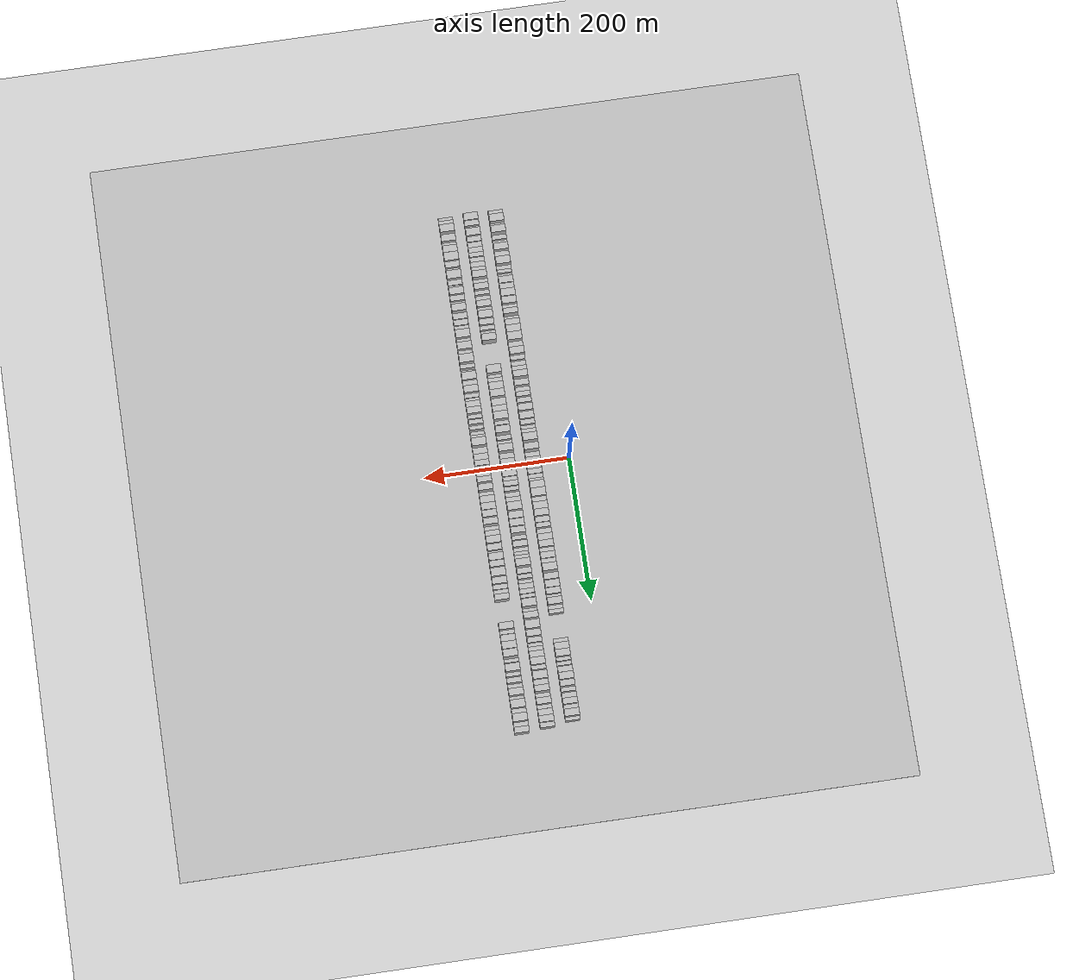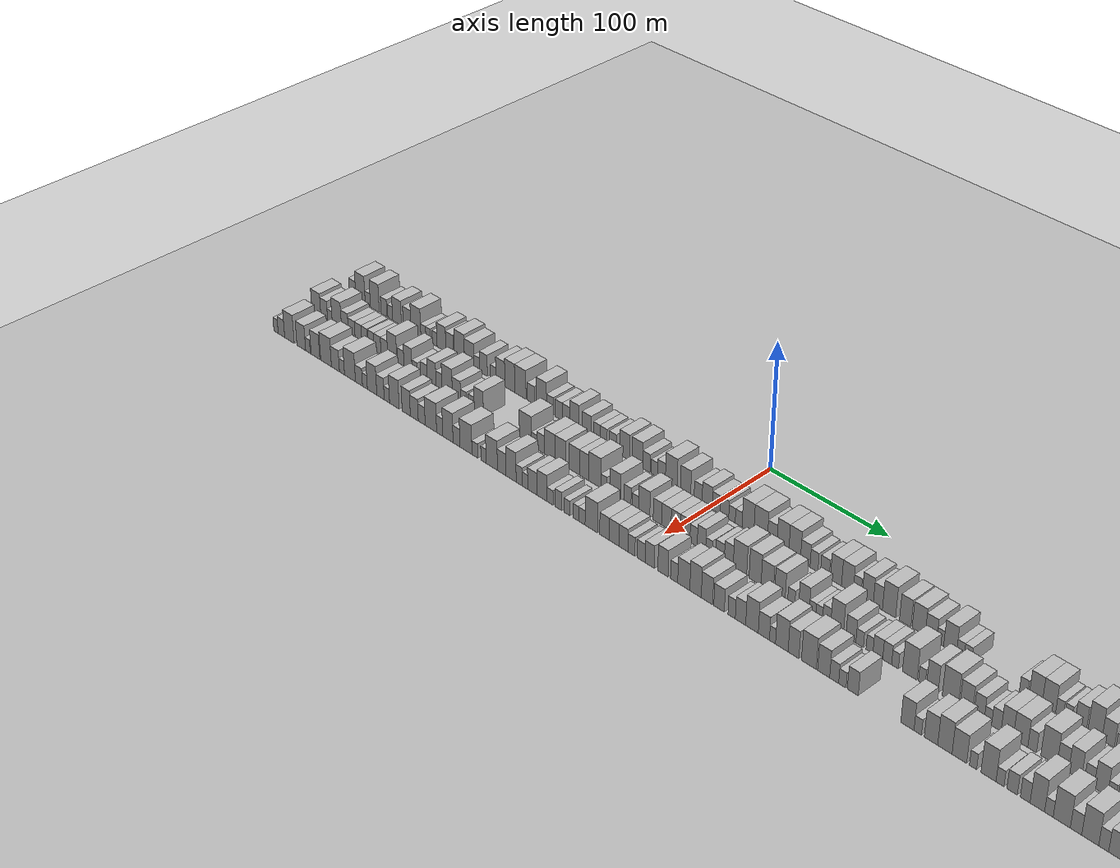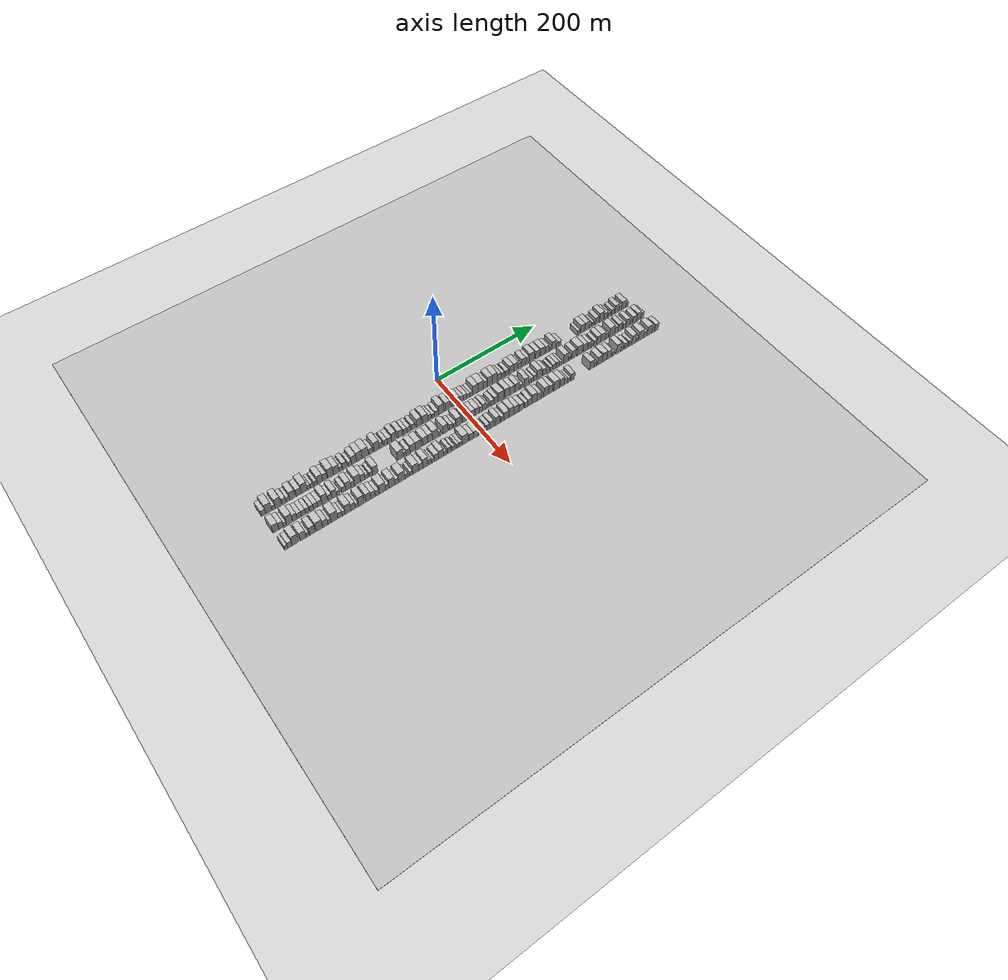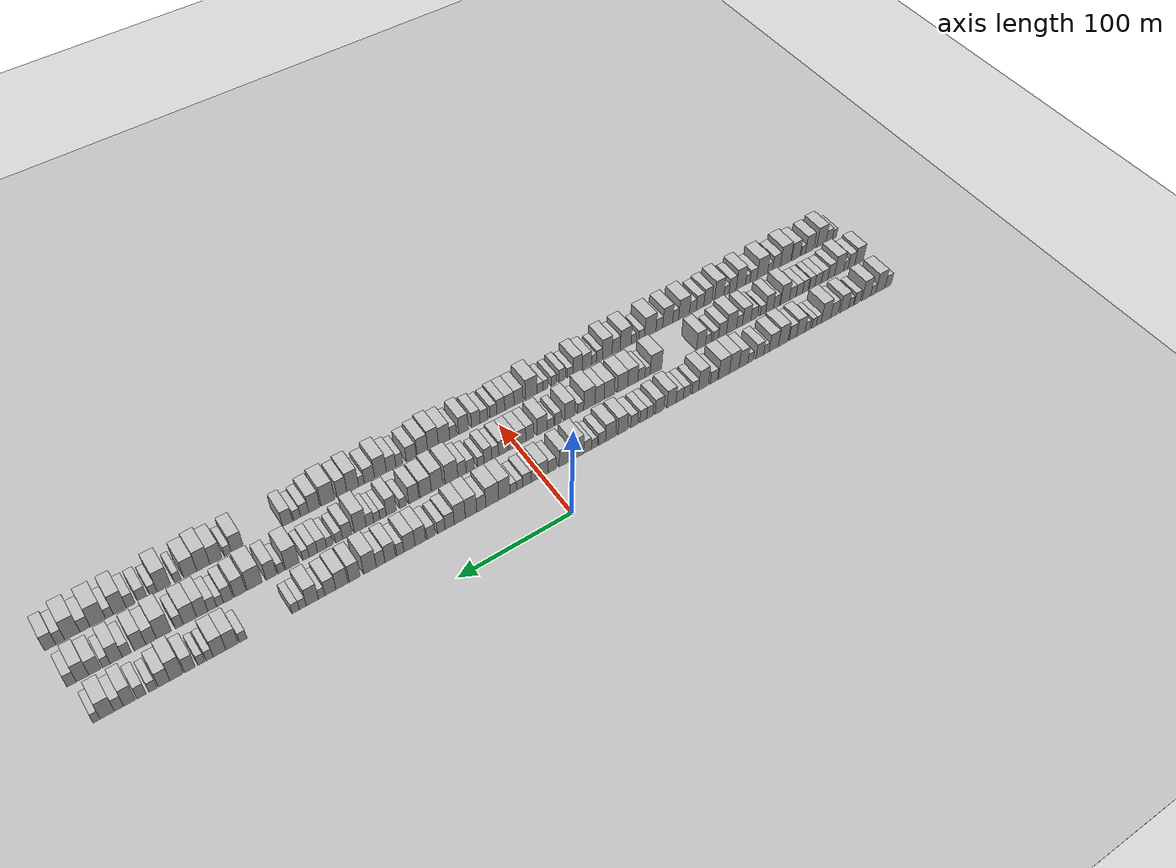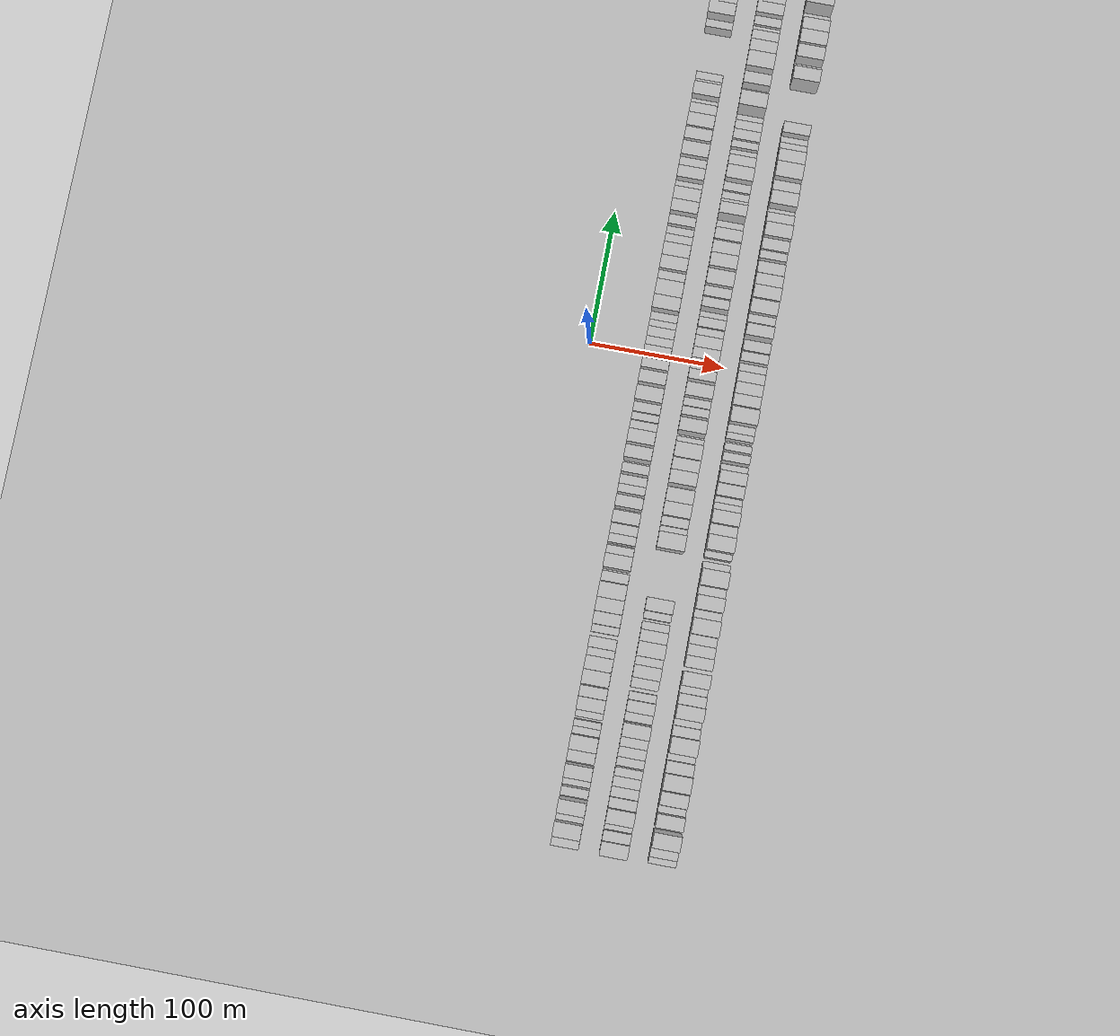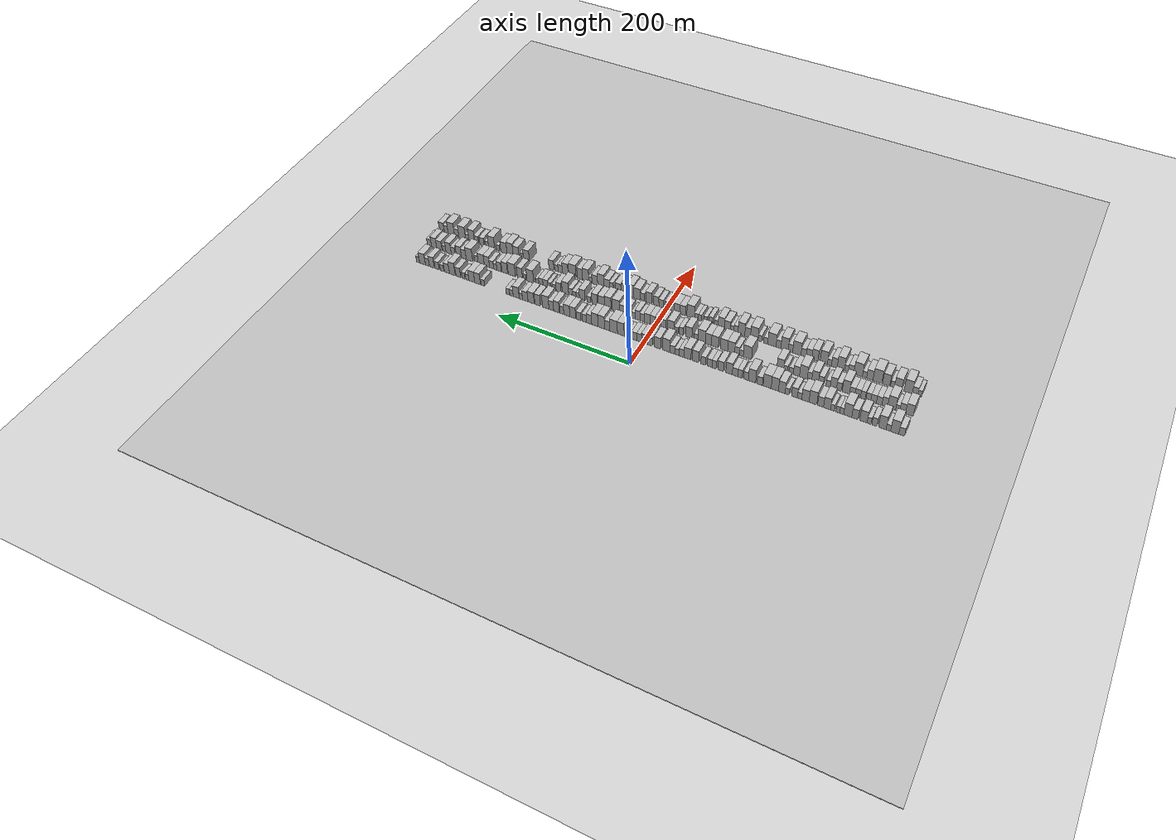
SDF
<?xml version="1.0" encoding="utf-8"?>

<sdf version="1.6">

   <world name="default">

      <gui fullscreen="0">

         <camera name="user_camera">

            <pose>-15 0 4.57585 0 0 0</pose>

            <view_controller>orbit</view_controller>

         </camera>

      </gui>

      <scene>

         <sky>

           <clouds>

             <speed>12</speed>

           </clouds>

         </sky>

         <ambient>0.4 0.4 0.4 1</ambient>

         <background>0.7 0.7 0.7 1</background>

         <shadows>1</shadows>

      </scene>

      <gravity>0 0 -9.8066</gravity>

      <magnetic_field>6e-06 2.3e-05 -4.2e-05</magnetic_field>

      <physics default="0" name="default_physics" type="ode">

         <ode>

            <solver>

               <type>quick</type>

               <iters>10</iters>

               <sor>1.0</sor>

               <use_dynamic_moi_rescaling>0</use_dynamic_moi_rescaling>

            </solver>

            <constraints>

               <cfm>0</cfm>

               <erp>0.2</erp>

               <contact_max_correcting_vel>100</contact_max_correcting_vel>

               <contact_surface_layer>0.001</contact_surface_layer>

            </constraints>

         </ode>

         <max_step_size>0.004</max_step_size>

         <real_time_factor>1</real_time_factor>

         <real_time_update_rate>250</real_time_update_rate>

      </physics>

      <light name="sun" type="directional">

         <cast_shadows>1</cast_shadows>

         <pose>0 0 10 0 0 0</pose>

         <diffuse>0.8 0.8 0.8 1</diffuse>

         <specular>0.2 0.2 0.2 1</specular>

         <attenuation>

            <range>1000</range>

            <constant>0.9</constant>

            <linear>0.01</linear>

            <quadratic>0.001</quadratic>

         </attenuation>

         <direction>-0.5 0.1 -0.9</direction>

      </light>

      <include>

         <name>ground_plane_1</name>

         <uri>model://HANNAS_ground_plane</uri>

         <pose>0 0 0  0 0 0</pose>

      </include>

      <include>

         <name>ground_plane_2</name>

         <uri>model://HANNAS_ground_plane</uri>

         <pose>100 0 0  0 0 0</pose>

      </include>

      <model name="building_1">

         <static>1</static>

         <pose frame="">50.0000 -356.3182 0 0.000000 0.000000 0.000000</pose>

         <link name="link">

            <pose frame="">0 0 7.50 0 0 0</pose>

            <collision name="collision">

               <geometry>

                  <box>

                     <size>20.0000 7.3635 15.0000</size>

                  </box>

               </geometry>

               <max_contacts>10</max_contacts>

               <surface>

                  <contact>

                     <ode/>

                  </contact>

                  <bounce/>

                  <friction>

                     <torsional>

                        <ode/>

                     </torsional>

                     <ode/>

                  </friction>

               </surface>

            </collision>

            <visual name="visual">

               <cast_shadows>0</cast_shadows>

               <geometry>

                  <box>

                     <size>20.0000 7.3635 15.0000</size>

                  </box>

               </geometry>

               <material>

                  <script>

                     <uri>model://HANNAS_wall/materials/scripts</uri>

                     <uri>model://HANNAS_wall/materials/textures</uri>

                     <name>vrc/HANNAS_wall</name>

                  </script>

               </material>

            </visual>

            <self_collide>0</self_collide>

            <enable_wind>0</enable_wind>

            <kinematic>0</kinematic>

         </link>

      </model>

      <model name="building_2">

         <static>1</static>

         <pose frame="">50.0000 -347.3220 0 0.000000 0.000000 0.000000</pose>

         <link name="link">

            <pose frame="">0 0 12.00 0 0 0</pose>

            <collision name="collision">

               <geometry>

                  <box>

                     <size>20.0000 10.6289 24.0000</size>

                  </box>

               </geometry>

               <max_contacts>10</max_contacts>

               <surface>

                  <contact>

                     <ode/>

                  </contact>

                  <bounce/>

                  <friction>

                     <torsional>

                        <ode/>

                     </torsional>

                     <ode/>

                  </friction>

               </surface>

            </collision>

            <visual name="visual">

               <cast_shadows>0</cast_shadows>

               <geometry>

                  <box>

                     <size>20.0000 10.6289 24.0000</size>

                  </box>

               </geometry>

               <material>

                  <script>

                     <uri>model://HANNAS_wall/materials/scripts</uri>

                     <uri>model://HANNAS_wall/materials/textures</uri>

                     <name>vrc/HANNAS_wall</name>

                  </script>

               </material>

            </visual>

            <self_collide>0</self_collide>

            <enable_wind>0</enable_wind>

            <kinematic>0</kinematic>

         </link>

      </model>

      <model name="building_3">

         <static>1</static>

         <pose frame="">50.0000 -339.0892 0 0.000000 0.000000 0.000000</pose>

         <link name="link">

            <pose frame="">0 0 6.00 0 0 0</pose>

            <collision name="collision">

               <geometry>

                  <box>

                     <size>20.0000 5.8367 12.0000</size>

                  </box>

               </geometry>

               <max_contacts>10</max_contacts>

               <surface>

                  <contact>

                     <ode/>

                  </contact>

                  <bounce/>

                  <friction>

                     <torsional>

                        <ode/>

                     </torsional>

                     <ode/>

                  </friction>

               </surface>

            </collision>

            <visual name="visual">

               <cast_shadows>0</cast_shadows>

               <geometry>

                  <box>

                     <size>20.0000 5.8367 12.0000</size>

                  </box>

               </geometry>

               <material>

                  <script>

                     <uri>model://HANNAS_wall/materials/scripts</uri>

                     <uri>model://HANNAS_wall/materials/textures</uri>

                     <name>vrc/HANNAS_wall</name>

                  </script>

               </material>

            </visual>

            <self_collide>0</self_collide>

            <enable_wind>0</enable_wind>

            <kinematic>0</kinematic>

         </link>

      </model>

      <model name="building_4">

         <static>1</static>

         <pose frame="">50.0000 -331.2127 0 0.000000 0.000000 0.000000</pose>

         <link name="link">

            <pose frame="">0 0 12.00 0 0 0</pose>

            <collision name="collision">

               <geometry>

                  <box>

                     <size>20.0000 9.9163 24.0000</size>

                  </box>

               </geometry>

               <max_contacts>10</max_contacts>

               <surface>

                  <contact>

                     <ode/>

                  </contact>

                  <bounce/>

                  <friction>

                     <torsional>

                        <ode/>

                     </torsional>

                     <ode/>

                  </friction>

               </surface>

            </collision>

            <visual name="visual">

               <cast_shadows>0</cast_shadows>

               <geometry>

                  <box>

                     <size>20.0000 9.9163 24.0000</size>

                  </box>

               </geometry>

               <material>

                  <script>

                     <uri>model://HANNAS_wall/materials/scripts</uri>

                     <uri>model://HANNAS_wall/materials/textures</uri>

                     <name>vrc/HANNAS_wall</name>

                  </script>

               </material>

            </visual>

            <self_collide>0</self_collide>

            <enable_wind>0</enable_wind>

            <kinematic>0</kinematic>

         </link>

      </model>

      <model name="building_5">

         <static>1</static>

         <pose frame="">50.0000 -320.9949 0 0.000000 0.000000 0.000000</pose>

         <link name="link">

            <pose frame="">0 0 7.50 0 0 0</pose>

            <collision name="collision">

               <geometry>

                  <box>

                     <size>20.0000 6.5192 15.0000</size>

                  </box>

               </geometry>

               <max_contacts>10</max_contacts>

               <surface>

                  <contact>

                     <ode/>

                  </contact>

                  <bounce/>

                  <friction>

                     <torsional>

                        <ode/>

                     </torsional>

                     <ode/>

                  </friction>

               </surface>

            </collision>

            <visual name="visual">

               <cast_shadows>0</cast_shadows>

               <geometry>

                  <box>

                     <size>20.0000 6.5192 15.0000</size>

                  </box>

               </geometry>

               <material>

                  <script>

                     <uri>model://HANNAS_wall/materials/scripts</uri>

                     <uri>model://HANNAS_wall/materials/textures</uri>

                     <name>vrc/HANNAS_wall</name>

                  </script>

               </material>

            </visual>

            <self_collide>0</self_collide>

            <enable_wind>0</enable_wind>

            <kinematic>0</kinematic>

         </link>

      </model>

      <model name="building_6">

         <static>1</static>

         <pose frame="">50.0000 -314.0571 0 0.000000 0.000000 0.000000</pose>

         <link name="link">

            <pose frame="">0 0 6.00 0 0 0</pose>

            <collision name="collision">

               <geometry>

                  <box>

                     <size>20.0000 5.3563 12.0000</size>

                  </box>

               </geometry>

               <max_contacts>10</max_contacts>

               <surface>

                  <contact>

                     <ode/>

                  </contact>

                  <bounce/>

                  <friction>

                     <torsional>

                        <ode/>

                     </torsional>

                     <ode/>

                  </friction>

               </surface>

            </collision>

            <visual name="visual">

               <cast_shadows>0</cast_shadows>

               <geometry>

                  <box>

                     <size>20.0000 5.3563 12.0000</size>

                  </box>

               </geometry>

               <material>

                  <script>

                     <uri>model://HANNAS_wall/materials/scripts</uri>

                     <uri>model://HANNAS_wall/materials/textures</uri>

                     <name>vrc/HANNAS_wall</name>

                  </script>

               </material>

            </visual>

            <self_collide>0</self_collide>

            <enable_wind>0</enable_wind>

            <kinematic>0</kinematic>

         </link>

      </model>

      <model name="building_7">

         <static>1</static>

         <pose frame="">50.0000 -306.5330 0 0.000000 0.000000 0.000000</pose>

         <link name="link">

            <pose frame="">0 0 10.50 0 0 0</pose>

            <collision name="collision">

               <geometry>

                  <box>

                     <size>20.0000 9.6920 21.0000</size>

                  </box>

               </geometry>

               <max_contacts>10</max_contacts>

               <surface>

                  <contact>

                     <ode/>

                  </contact>

                  <bounce/>

                  <friction>

                     <torsional>

                        <ode/>

                     </torsional>

                     <ode/>

                  </friction>

               </surface>

            </collision>

            <visual name="visual">

               <cast_shadows>0</cast_shadows>

               <geometry>

                  <box>

                     <size>20.0000 9.6920 21.0000</size>

                  </box>

               </geometry>

               <material>

                  <script>

                     <uri>model://HANNAS_wall/materials/scripts</uri>

                     <uri>model://HANNAS_wall/materials/textures</uri>

                     <name>vrc/HANNAS_wall</name>

                  </script>

               </material>

            </visual>

            <self_collide>0</self_collide>

            <enable_wind>0</enable_wind>

            <kinematic>0</kinematic>

         </link>

      </model>

      <model name="building_8">

         <static>1</static>

         <pose frame="">50.0000 -295.4323 0 0.000000 0.000000 0.000000</pose>

         <link name="link">

            <pose frame="">0 0 9.00 0 0 0</pose>

            <collision name="collision">

               <geometry>

                  <box>

                     <size>20.0000 8.5095 18.0000</size>

                  </box>

               </geometry>

               <max_contacts>10</max_contacts>

               <surface>

                  <contact>

                     <ode/>

                  </contact>

                  <bounce/>

                  <friction>

                     <torsional>

                        <ode/>

                     </torsional>

                     <ode/>

                  </friction>

               </surface>

            </collision>

            <visual name="visual">

               <cast_shadows>0</cast_shadows>

               <geometry>

                  <box>

                     <size>20.0000 8.5095 18.0000</size>

                  </box>

               </geometry>

               <material>

                  <script>

                     <uri>model://HANNAS_wall/materials/scripts</uri>

                     <uri>model://HANNAS_wall/materials/textures</uri>

                     <name>vrc/HANNAS_wall</name>

                  </script>

               </material>

            </visual>

            <self_collide>0</self_collide>

            <enable_wind>0</enable_wind>

            <kinematic>0</kinematic>

         </link>

      </model>

      <model name="building_9">

         <static>1</static>

         <pose frame="">50.0000 -285.8523 0 0.000000 0.000000 0.000000</pose>

         <link name="link">

            <pose frame="">0 0 12.00 0 0 0</pose>

            <collision name="collision">

               <geometry>

                  <box>

                     <size>20.0000 10.6504 24.0000</size>

                  </box>

               </geometry>

               <max_contacts>10</max_contacts>

               <surface>

                  <contact>

                     <ode/>

                  </contact>

                  <bounce/>

                  <friction>

                     <torsional>

                        <ode/>

                     </torsional>

                     <ode/>

                  </friction>

               </surface>

            </collision>

            <visual name="visual">

               <cast_shadows>0</cast_shadows>

               <geometry>

                  <box>

                     <size>20.0000 10.6504 24.0000</size>

                  </box>

               </geometry>

               <material>

                  <script>

                     <uri>model://HANNAS_wall/materials/scripts</uri>

                     <uri>model://HANNAS_wall/materials/textures</uri>

                     <name>vrc/HANNAS_wall</name>

                  </script>

               </material>

            </visual>

            <self_collide>0</self_collide>

            <enable_wind>0</enable_wind>

            <kinematic>0</kinematic>

         </link>

      </model>

      <model name="building_10">

         <static>1</static>

         <pose frame="">50.0000 -277.8127 0 0.000000 0.000000 0.000000</pose>

         <link name="link">

            <pose frame="">0 0 6.00 0 0 0</pose>

            <collision name="collision">

               <geometry>

                  <box>

                     <size>20.0000 5.4288 12.0000</size>

                  </box>

               </geometry>

               <max_contacts>10</max_contacts>

               <surface>

                  <contact>

                     <ode/>

                  </contact>

                  <bounce/>

                  <friction>

                     <torsional>

                        <ode/>

                     </torsional>

                     <ode/>

                  </friction>

               </surface>

            </collision>

            <visual name="visual">

               <cast_shadows>0</cast_shadows>

               <geometry>

                  <box>

                     <size>20.0000 5.4288 12.0000</size>

                  </box>

               </geometry>

               <material>

                  <script>

                     <uri>model://HANNAS_wall/materials/scripts</uri>

                     <uri>model://HANNAS_wall/materials/textures</uri>

                     <name>vrc/HANNAS_wall</name>

                  </script>

               </material>

            </visual>

            <self_collide>0</self_collide>

            <enable_wind>0</enable_wind>

            <kinematic>0</kinematic>

         </link>

      </model>

      <model name="building_11">

         <static>1</static>

         <pose frame="">50.0000 -272.6775 0 0.000000 0.000000 0.000000</pose>

         <link name="link">

            <pose frame="">0 0 6.00 0 0 0</pose>

            <collision name="collision">

               <geometry>

                  <box>

                     <size>20.0000 4.8417 12.0000</size>

                  </box>

               </geometry>

               <max_contacts>10</max_contacts>

               <surface>

                  <contact>

                     <ode/>

                  </contact>

                  <bounce/>

                  <friction>

                     <torsional>

                        <ode/>

                     </torsional>

                     <ode/>

                  </friction>

               </surface>

            </collision>

            <visual name="visual">

               <cast_shadows>0</cast_shadows>

               <geometry>

                  <box>

                     <size>20.0000 4.8417 12.0000</size>

                  </box>

               </geometry>

               <material>

                  <script>

                     <uri>model://HANNAS_wall/materials/scripts</uri>

                     <uri>model://HANNAS_wall/materials/textures</uri>

                     <name>vrc/HANNAS_wall</name>

                  </script>

               </material>

            </visual>

            <self_collide>0</self_collide>

            <enable_wind>0</enable_wind>

            <kinematic>0</kinematic>

         </link>

      </model>

      <model name="building_12">

         <static>1</static>

         <pose frame="">50.0000 -265.6677 0 0.000000 0.000000 0.000000</pose>

         <link name="link">

            <pose frame="">0 0 6.00 0 0 0</pose>

            <collision name="collision">

               <geometry>

                  <box>

                     <size>20.0000 5.1778 12.0000</size>

                  </box>

               </geometry>

               <max_contacts>10</max_contacts>

               <surface>

                  <contact>

                     <ode/>

                  </contact>

                  <bounce/>

                  <friction>

                     <torsional>

                        <ode/>

                     </torsional>

                     <ode/>

                  </friction>

               </surface>

            </collision>

            <visual name="visual">

               <cast_shadows>0</cast_shadows>

               <geometry>

                  <box>

                     <size>20.0000 5.1778 12.0000</size>

                  </box>

               </geometry>

               <material>

                  <script>

                     <uri>model://HANNAS_wall/materials/scripts</uri>

                     <uri>model://HANNAS_wall/materials/textures</uri>

                     <name>vrc/HANNAS_wall</name>

                  </script>

               </material>

            </visual>

            <self_collide>0</self_collide>

            <enable_wind>0</enable_wind>

            <kinematic>0</kinematic>

         </link>

      </model>

      <model name="building_13">

         <static>1</static>

         <pose frame="">50.0000 -258.3570 0 0.000000 0.000000 0.000000</pose>

         <link name="link">

            <pose frame="">0 0 10.50 0 0 0</pose>

            <collision name="collision">

               <geometry>

                  <box>

                     <size>20.0000 9.4436 21.0000</size>

                  </box>

               </geometry>

               <max_contacts>10</max_contacts>

               <surface>

                  <contact>

                     <ode/>

                  </contact>

                  <bounce/>

                  <friction>

                     <torsional>

                        <ode/>

                     </torsional>

                     <ode/>

                  </friction>

               </surface>

            </collision>

            <visual name="visual">

               <cast_shadows>0</cast_shadows>

               <geometry>

                  <box>

                     <size>20.0000 9.4436 21.0000</size>

                  </box>

               </geometry>

               <material>

                  <script>

                     <uri>model://HANNAS_wall/materials/scripts</uri>

                     <uri>model://HANNAS_wall/materials/textures</uri>

                     <name>vrc/HANNAS_wall</name>

                  </script>

               </material>

            </visual>

            <self_collide>0</self_collide>

            <enable_wind>0</enable_wind>

            <kinematic>0</kinematic>

         </link>

      </model>

      <model name="building_14">

         <static>1</static>

         <pose frame="">50.0000 -249.5929 0 0.000000 0.000000 0.000000</pose>

         <link name="link">

            <pose frame="">0 0 9.00 0 0 0</pose>

            <collision name="collision">

               <geometry>

                  <box>

                     <size>20.0000 8.0846 18.0000</size>

                  </box>

               </geometry>

               <max_contacts>10</max_contacts>

               <surface>

                  <contact>

                     <ode/>

                  </contact>

                  <bounce/>

                  <friction>

                     <torsional>

                        <ode/>

                     </torsional>

                     <ode/>

                  </friction>

               </surface>

            </collision>

            <visual name="visual">

               <cast_shadows>0</cast_shadows>

               <geometry>

                  <box>

                     <size>20.0000 8.0846 18.0000</size>

                  </box>

               </geometry>

               <material>

                  <script>

                     <uri>model://HANNAS_wall/materials/scripts</uri>

                     <uri>model://HANNAS_wall/materials/textures</uri>

                     <name>vrc/HANNAS_wall</name>

                  </script>

               </material>

            </visual>

            <self_collide>0</self_collide>

            <enable_wind>0</enable_wind>

            <kinematic>0</kinematic>

         </link>

      </model>

      <model name="building_15">

         <static>1</static>

         <pose frame="">50.0000 -239.2889 0 0.000000 0.000000 0.000000</pose>

         <link name="link">

            <pose frame="">0 0 12.00 0 0 0</pose>

            <collision name="collision">

               <geometry>

                  <box>

                     <size>20.0000 10.5233 24.0000</size>

                  </box>

               </geometry>

               <max_contacts>10</max_contacts>

               <surface>

                  <contact>

                     <ode/>

                  </contact>

                  <bounce/>

                  <friction>

                     <torsional>

                        <ode/>

                     </torsional>

                     <ode/>

                  </friction>

               </surface>

            </collision>

            <visual name="visual">

               <cast_shadows>0</cast_shadows>

               <geometry>

                  <box>

                     <size>20.0000 10.5233 24.0000</size>

                  </box>

               </geometry>

               <material>

                  <script>

                     <uri>model://HANNAS_wall/materials/scripts</uri>

                     <uri>model://HANNAS_wall/materials/textures</uri>

                     <name>vrc/HANNAS_wall</name>

                  </script>

               </material>

            </visual>

            <self_collide>0</self_collide>

            <enable_wind>0</enable_wind>

            <kinematic>0</kinematic>

         </link>

      </model>

      <model name="building_16">

         <static>1</static>

         <pose frame="">50.0000 -229.0714 0 0.000000 0.000000 0.000000</pose>

         <link name="link">

            <pose frame="">0 0 10.50 0 0 0</pose>

            <collision name="collision">

               <geometry>

                  <box>

                     <size>20.0000 9.9116 21.0000</size>

                  </box>

               </geometry>

               <max_contacts>10</max_contacts>

               <surface>

                  <contact>

                     <ode/>

                  </contact>

                  <bounce/>

                  <friction>

                     <torsional>

                        <ode/>

                     </torsional>

                     <ode/>

                  </friction>

               </surface>

            </collision>

            <visual name="visual">

               <cast_shadows>0</cast_shadows>

               <geometry>

                  <box>

                     <size>20.0000 9.9116 21.0000</size>

                  </box>

               </geometry>

               <material>

                  <script>

                     <uri>model://HANNAS_wall/materials/scripts</uri>

                     <uri>model://HANNAS_wall/materials/textures</uri>

                     <name>vrc/HANNAS_wall</name>

                  </script>

               </material>

            </visual>

            <self_collide>0</self_collide>

            <enable_wind>0</enable_wind>

            <kinematic>0</kinematic>

         </link>

      </model>

      <model name="building_17">

         <static>1</static>

         <pose frame="">50.0000 -221.1700 0 0.000000 0.000000 0.000000</pose>

         <link name="link">

            <pose frame="">0 0 6.00 0 0 0</pose>

            <collision name="collision">

               <geometry>

                  <box>

                     <size>20.0000 5.8912 12.0000</size>

                  </box>

               </geometry>

               <max_contacts>10</max_contacts>

               <surface>

                  <contact>

                     <ode/>

                  </contact>

                  <bounce/>

                  <friction>

                     <torsional>

                        <ode/>

                     </torsional>

                     <ode/>

                  </friction>

               </surface>

            </collision>

            <visual name="visual">

               <cast_shadows>0</cast_shadows>

               <geometry>

                  <box>

                     <size>20.0000 5.8912 12.0000</size>

                  </box>

               </geometry>

               <material>

                  <script>

                     <uri>model://HANNAS_wall/materials/scripts</uri>

                     <uri>model://HANNAS_wall/materials/textures</uri>

                     <name>vrc/HANNAS_wall</name>

                  </script>

               </material>

            </visual>

            <self_collide>0</self_collide>

            <enable_wind>0</enable_wind>

            <kinematic>0</kinematic>

         </link>

      </model>

      <model name="building_18">

         <static>1</static>

         <pose frame="">50.0000 -214.2446 0 0.000000 0.000000 0.000000</pose>

         <link name="link">

            <pose frame="">0 0 9.00 0 0 0</pose>

            <collision name="collision">

               <geometry>

                  <box>

                     <size>20.0000 7.9594 18.0000</size>

                  </box>

               </geometry>

               <max_contacts>10</max_contacts>

               <surface>

                  <contact>

                     <ode/>

                  </contact>

                  <bounce/>

                  <friction>

                     <torsional>

                        <ode/>

                     </torsional>

                     <ode/>

                  </friction>

               </surface>

            </collision>

            <visual name="visual">

               <cast_shadows>0</cast_shadows>

               <geometry>

                  <box>

                     <size>20.0000 7.9594 18.0000</size>

                  </box>

               </geometry>

               <material>

                  <script>

                     <uri>model://HANNAS_wall/materials/scripts</uri>

                     <uri>model://HANNAS_wall/materials/textures</uri>

                     <name>vrc/HANNAS_wall</name>

                  </script>

               </material>

            </visual>

            <self_collide>0</self_collide>

            <enable_wind>0</enable_wind>

            <kinematic>0</kinematic>

         </link>

      </model>

      <model name="building_19">

         <static>1</static>

         <pose frame="">50.0000 -204.4203 0 0.000000 0.000000 0.000000</pose>

         <link name="link">

            <pose frame="">0 0 6.00 0 0 0</pose>

            <collision name="collision">

               <geometry>

                  <box>

                     <size>20.0000 5.6892 12.0000</size>

                  </box>

               </geometry>

               <max_contacts>10</max_contacts>

               <surface>

                  <contact>

                     <ode/>

                  </contact>

                  <bounce/>

                  <friction>

                     <torsional>

                        <ode/>

                     </torsional>

                     <ode/>

                  </friction>

               </surface>

            </collision>

            <visual name="visual">

               <cast_shadows>0</cast_shadows>

               <geometry>

                  <box>

                     <size>20.0000 5.6892 12.0000</size>

                  </box>

               </geometry>

               <material>

                  <script>

                     <uri>model://HANNAS_wall/materials/scripts</uri>

                     <uri>model://HANNAS_wall/materials/textures</uri>

                     <name>vrc/HANNAS_wall</name>

                  </script>

               </material>

            </visual>

            <self_collide>0</self_collide>

            <enable_wind>0</enable_wind>

            <kinematic>0</kinematic>

         </link>

      </model>

      <model name="building_20">

         <static>1</static>

         <pose frame="">50.0000 -196.9726 0 0.000000 0.000000 0.000000</pose>

         <link name="link">

            <pose frame="">0 0 10.50 0 0 0</pose>

            <collision name="collision">

               <geometry>

                  <box>

                     <size>20.0000 9.2061 21.0000</size>

                  </box>

               </geometry>

               <max_contacts>10</max_contacts>

               <surface>

                  <contact>

                     <ode/>

                  </contact>

                  <bounce/>

                  <friction>

                     <torsional>

                        <ode/>

                     </torsional>

                     <ode/>

                  </friction>

               </surface>

            </collision>

            <visual name="visual">

               <cast_shadows>0</cast_shadows>

               <geometry>

                  <box>

                     <size>20.0000 9.2061 21.0000</size>

                  </box>

               </geometry>

               <material>

                  <script>

                     <uri>model://HANNAS_wall/materials/scripts</uri>

                     <uri>model://HANNAS_wall/materials/textures</uri>

                     <name>vrc/HANNAS_wall</name>

                  </script>

               </material>

            </visual>

            <self_collide>0</self_collide>

            <enable_wind>0</enable_wind>

            <kinematic>0</kinematic>

         </link>

      </model>

      <model name="building_21">

         <static>1</static>

         <pose frame="">50.0000 -187.3796 0 0.000000 0.000000 0.000000</pose>

         <link name="link">

            <pose frame="">0 0 12.00 0 0 0</pose>

            <collision name="collision">

               <geometry>

                  <box>

                     <size>20.0000 9.9799 24.0000</size>

                  </box>

               </geometry>

               <max_contacts>10</max_contacts>

               <surface>

                  <contact>

                     <ode/>

                  </contact>

                  <bounce/>

                  <friction>

                     <torsional>

                        <ode/>

                     </torsional>

                     <ode/>

                  </friction>

               </surface>

            </collision>

            <visual name="visual">

               <cast_shadows>0</cast_shadows>

               <geometry>

                  <box>

                     <size>20.0000 9.9799 24.0000</size>

                  </box>

               </geometry>

               <material>

                  <script>

                     <uri>model://HANNAS_wall/materials/scripts</uri>

                     <uri>model://HANNAS_wall/materials/textures</uri>

                     <name>vrc/HANNAS_wall</name>

                  </script>

               </material>

            </visual>

            <self_collide>0</self_collide>

            <enable_wind>0</enable_wind>

            <kinematic>0</kinematic>

         </link>

      </model>

      <model name="building_22">

         <static>1</static>

         <pose frame="">50.0000 -176.7618 0 0.000000 0.000000 0.000000</pose>

         <link name="link">

            <pose frame="">0 0 12.00 0 0 0</pose>

            <collision name="collision">

               <geometry>

                  <box>

                     <size>20.0000 11.2558 24.0000</size>

                  </box>

               </geometry>

               <max_contacts>10</max_contacts>

               <surface>

                  <contact>

                     <ode/>

                  </contact>

                  <bounce/>

                  <friction>

                     <torsional>

                        <ode/>

                     </torsional>

                     <ode/>

                  </friction>

               </surface>

            </collision>

            <visual name="visual">

               <cast_shadows>0</cast_shadows>

               <geometry>

                  <box>

                     <size>20.0000 11.2558 24.0000</size>

                  </box>

               </geometry>

               <material>

                  <script>

                     <uri>model://HANNAS_wall/materials/scripts</uri>

                     <uri>model://HANNAS_wall/materials/textures</uri>

                     <name>vrc/HANNAS_wall</name>

                  </script>

               </material>

            </visual>

            <self_collide>0</self_collide>

            <enable_wind>0</enable_wind>

            <kinematic>0</kinematic>

         </link>

      </model>

      <model name="building_23">

         <static>1</static>

         <pose frame="">50.0000 -166.4585 0 0.000000 0.000000 0.000000</pose>

         <link name="link">

            <pose frame="">0 0 7.50 0 0 0</pose>

            <collision name="collision">

               <geometry>

                  <box>

                     <size>20.0000 7.3508 15.0000</size>

                  </box>

               </geometry>

               <max_contacts>10</max_contacts>

               <surface>

                  <contact>

                     <ode/>

                  </contact>

                  <bounce/>

                  <friction>

                     <torsional>

                        <ode/>

                     </torsional>

                     <ode/>

                  </friction>

               </surface>

            </collision>

            <visual name="visual">

               <cast_shadows>0</cast_shadows>

               <geometry>

                  <box>

                     <size>20.0000 7.3508 15.0000</size>

                  </box>

               </geometry>

               <material>

                  <script>

                     <uri>model://HANNAS_wall/materials/scripts</uri>

                     <uri>model://HANNAS_wall/materials/textures</uri>

                     <name>vrc/HANNAS_wall</name>

                  </script>

               </material>

            </visual>

            <self_collide>0</self_collide>

            <enable_wind>0</enable_wind>

            <kinematic>0</kinematic>

         </link>

      </model>

      <model name="building_24">

         <static>1</static>

         <pose frame="">50.0000 -155.7523 0 0.000000 0.000000 0.000000</pose>

         <link name="link">

            <pose frame="">0 0 12.00 0 0 0</pose>

            <collision name="collision">

               <geometry>

                  <box>

                     <size>20.0000 10.0615 24.0000</size>

                  </box>

               </geometry>

               <max_contacts>10</max_contacts>

               <surface>

                  <contact>

                     <ode/>

                  </contact>

                  <bounce/>

                  <friction>

                     <torsional>

                        <ode/>

                     </torsional>

                     <ode/>

                  </friction>

               </surface>

            </collision>

            <visual name="visual">

               <cast_shadows>0</cast_shadows>

               <geometry>

                  <box>

                     <size>20.0000 10.0615 24.0000</size>

                  </box>

               </geometry>

               <material>

                  <script>

                     <uri>model://HANNAS_wall/materials/scripts</uri>

                     <uri>model://HANNAS_wall/materials/textures</uri>

                     <name>vrc/HANNAS_wall</name>

                  </script>

               </material>

            </visual>

            <self_collide>0</self_collide>

            <enable_wind>0</enable_wind>

            <kinematic>0</kinematic>

         </link>

      </model>

      <model name="building_25">

         <static>1</static>

         <pose frame="">50.0000 -147.3862 0 0.000000 0.000000 0.000000</pose>

         <link name="link">

            <pose frame="">0 0 7.50 0 0 0</pose>

            <collision name="collision">

               <geometry>

                  <box>

                     <size>20.0000 6.6707 15.0000</size>

                  </box>

               </geometry>

               <max_contacts>10</max_contacts>

               <surface>

                  <contact>

                     <ode/>

                  </contact>

                  <bounce/>

                  <friction>

                     <torsional>

                        <ode/>

                     </torsional>

                     <ode/>

                  </friction>

               </surface>

            </collision>

            <visual name="visual">

               <cast_shadows>0</cast_shadows>

               <geometry>

                  <box>

                     <size>20.0000 6.6707 15.0000</size>

                  </box>

               </geometry>

               <material>

                  <script>

                     <uri>model://HANNAS_wall/materials/scripts</uri>

                     <uri>model://HANNAS_wall/materials/textures</uri>

                     <name>vrc/HANNAS_wall</name>

                  </script>

               </material>

            </visual>

            <self_collide>0</self_collide>

            <enable_wind>0</enable_wind>

            <kinematic>0</kinematic>

         </link>

      </model>

      <model name="building_26">

         <static>1</static>

         <pose frame="">50.0000 -138.7556 0 0.000000 0.000000 0.000000</pose>

         <link name="link">

            <pose frame="">0 0 7.50 0 0 0</pose>

            <collision name="collision">

               <geometry>

                  <box>

                     <size>20.0000 6.5905 15.0000</size>

                  </box>

               </geometry>

               <max_contacts>10</max_contacts>

               <surface>

                  <contact>

                     <ode/>

                  </contact>

                  <bounce/>

                  <friction>

                     <torsional>

                        <ode/>

                     </torsional>

                     <ode/>

                  </friction>

               </surface>

            </collision>

            <visual name="visual">

               <cast_shadows>0</cast_shadows>

               <geometry>

                  <box>

                     <size>20.0000 6.5905 15.0000</size>

                  </box>

               </geometry>

               <material>

                  <script>

                     <uri>model://HANNAS_wall/materials/scripts</uri>

                     <uri>model://HANNAS_wall/materials/textures</uri>

                     <name>vrc/HANNAS_wall</name>

                  </script>

               </material>

            </visual>

            <self_collide>0</self_collide>

            <enable_wind>0</enable_wind>

            <kinematic>0</kinematic>

         </link>

      </model>

      <model name="building_27">

         <static>1</static>

         <pose frame="">50.0000 -131.7457 0 0.000000 0.000000 0.000000</pose>

         <link name="link">

            <pose frame="">0 0 7.50 0 0 0</pose>

            <collision name="collision">

               <geometry>

                  <box>

                     <size>20.0000 7.4293 15.0000</size>

                  </box>

               </geometry>

               <max_contacts>10</max_contacts>

               <surface>

                  <contact>

                     <ode/>

                  </contact>

                  <bounce/>

                  <friction>

                     <torsional>

                        <ode/>

                     </torsional>

                     <ode/>

                  </friction>

               </surface>

            </collision>

            <visual name="visual">

               <cast_shadows>0</cast_shadows>

               <geometry>

                  <box>

                     <size>20.0000 7.4293 15.0000</size>

                  </box>

               </geometry>

               <material>

                  <script>

                     <uri>model://HANNAS_wall/materials/scripts</uri>

                     <uri>model://HANNAS_wall/materials/textures</uri>

                     <name>vrc/HANNAS_wall</name>

                  </script>

               </material>

            </visual>

            <self_collide>0</self_collide>

            <enable_wind>0</enable_wind>

            <kinematic>0</kinematic>

         </link>

      </model>

      <model name="building_28">

         <static>1</static>

         <pose frame="">50.0000 -123.4774 0 0.000000 0.000000 0.000000</pose>

         <link name="link">

            <pose frame="">0 0 10.50 0 0 0</pose>

            <collision name="collision">

               <geometry>

                  <box>

                     <size>20.0000 9.1073 21.0000</size>

                  </box>

               </geometry>

               <max_contacts>10</max_contacts>

               <surface>

                  <contact>

                     <ode/>

                  </contact>

                  <bounce/>

                  <friction>

                     <torsional>

                        <ode/>

                     </torsional>

                     <ode/>

                  </friction>

               </surface>

            </collision>

            <visual name="visual">

               <cast_shadows>0</cast_shadows>

               <geometry>

                  <box>

                     <size>20.0000 9.1073 21.0000</size>

                  </box>

               </geometry>

               <material>

                  <script>

                     <uri>model://HANNAS_wall/materials/scripts</uri>

                     <uri>model://HANNAS_wall/materials/textures</uri>

                     <name>vrc/HANNAS_wall</name>

                  </script>

               </material>

            </visual>

            <self_collide>0</self_collide>

            <enable_wind>0</enable_wind>

            <kinematic>0</kinematic>

         </link>

      </model>

      <model name="building_29">

         <static>1</static>

         <pose frame="">50.0000 -111.6304 0 0.000000 0.000000 0.000000</pose>

         <link name="link">

            <pose frame="">0 0 9.00 0 0 0</pose>

            <collision name="collision">

               <geometry>

                  <box>

                     <size>20.0000 8.5869 18.0000</size>

                  </box>

               </geometry>

               <max_contacts>10</max_contacts>

               <surface>

                  <contact>

                     <ode/>

                  </contact>

                  <bounce/>

                  <friction>

                     <torsional>

                        <ode/>

                     </torsional>

                     <ode/>

                  </friction>

               </surface>

            </collision>

            <visual name="visual">

               <cast_shadows>0</cast_shadows>

               <geometry>

                  <box>

                     <size>20.0000 8.5869 18.0000</size>

                  </box>

               </geometry>

               <material>

                  <script>

                     <uri>model://HANNAS_wall/materials/scripts</uri>

                     <uri>model://HANNAS_wall/materials/textures</uri>

                     <name>vrc/HANNAS_wall</name>

                  </script>

               </material>

            </visual>

            <self_collide>0</self_collide>

            <enable_wind>0</enable_wind>

            <kinematic>0</kinematic>

         </link>

      </model>

      <model name="building_30">

         <static>1</static>

         <pose frame="">50.0000 -102.2345 0 0.000000 0.000000 0.000000</pose>

         <link name="link">

            <pose frame="">0 0 7.50 0 0 0</pose>

            <collision name="collision">

               <geometry>

                  <box>

                     <size>20.0000 6.2049 15.0000</size>

                  </box>

               </geometry>

               <max_contacts>10</max_contacts>

               <surface>

                  <contact>

                     <ode/>

                  </contact>

                  <bounce/>

                  <friction>

                     <torsional>

                        <ode/>

                     </torsional>

                     <ode/>

                  </friction>

               </surface>

            </collision>

            <visual name="visual">

               <cast_shadows>0</cast_shadows>

               <geometry>

                  <box>

                     <size>20.0000 6.2049 15.0000</size>

                  </box>

               </geometry>

               <material>

                  <script>

                     <uri>model://HANNAS_wall/materials/scripts</uri>

                     <uri>model://HANNAS_wall/materials/textures</uri>

                     <name>vrc/HANNAS_wall</name>

                  </script>

               </material>

            </visual>

            <self_collide>0</self_collide>

            <enable_wind>0</enable_wind>

            <kinematic>0</kinematic>

         </link>

      </model>

      <model name="building_31">

         <static>1</static>

         <pose frame="">50.0000 -95.7270 0 0.000000 0.000000 0.000000</pose>

         <link name="link">

            <pose frame="">0 0 7.50 0 0 0</pose>

            <collision name="collision">

               <geometry>

                  <box>

                     <size>20.0000 6.8102 15.0000</size>

                  </box>

               </geometry>

               <max_contacts>10</max_contacts>

               <surface>

                  <contact>

                     <ode/>

                  </contact>

                  <bounce/>

                  <friction>

                     <torsional>

                        <ode/>

                     </torsional>

                     <ode/>

                  </friction>

               </surface>

            </collision>

            <visual name="visual">

               <cast_shadows>0</cast_shadows>

               <geometry>

                  <box>

                     <size>20.0000 6.8102 15.0000</size>

                  </box>

               </geometry>

               <material>

                  <script>

                     <uri>model://HANNAS_wall/materials/scripts</uri>

                     <uri>model://HANNAS_wall/materials/textures</uri>

                     <name>vrc/HANNAS_wall</name>

                  </script>

               </material>

            </visual>

            <self_collide>0</self_collide>

            <enable_wind>0</enable_wind>

            <kinematic>0</kinematic>

         </link>

      </model>

      <model name="building_32">

         <static>1</static>

         <pose frame="">50.0000 -86.8738 0 0.000000 0.000000 0.000000</pose>

         <link name="link">

            <pose frame="">0 0 7.50 0 0 0</pose>

            <collision name="collision">

               <geometry>

                  <box>

                     <size>20.0000 6.8960 15.0000</size>

                  </box>

               </geometry>

               <max_contacts>10</max_contacts>

               <surface>

                  <contact>

                     <ode/>

                  </contact>

                  <bounce/>

                  <friction>

                     <torsional>

                        <ode/>

                     </torsional>

                     <ode/>

                  </friction>

               </surface>

            </collision>

            <visual name="visual">

               <cast_shadows>0</cast_shadows>

               <geometry>

                  <box>

                     <size>20.0000 6.8960 15.0000</size>

                  </box>

               </geometry>

               <material>

                  <script>

                     <uri>model://HANNAS_wall/materials/scripts</uri>

                     <uri>model://HANNAS_wall/materials/textures</uri>

                     <name>vrc/HANNAS_wall</name>

                  </script>

               </material>

            </visual>

            <self_collide>0</self_collide>

            <enable_wind>0</enable_wind>

            <kinematic>0</kinematic>

         </link>

      </model>

      <model name="building_33">

         <static>1</static>

         <pose frame="">50.0000 -75.7585 0 0.000000 0.000000 0.000000</pose>

         <link name="link">

            <pose frame="">0 0 10.50 0 0 0</pose>

            <collision name="collision">

               <geometry>

                  <box>

                     <size>20.0000 9.3346 21.0000</size>

                  </box>

               </geometry>

               <max_contacts>10</max_contacts>

               <surface>

                  <contact>

                     <ode/>

                  </contact>

                  <bounce/>

                  <friction>

                     <torsional>

                        <ode/>

                     </torsional>

                     <ode/>

                  </friction>

               </surface>

            </collision>

            <visual name="visual">

               <cast_shadows>0</cast_shadows>

               <geometry>

                  <box>

                     <size>20.0000 9.3346 21.0000</size>

                  </box>

               </geometry>

               <material>

                  <script>

                     <uri>model://HANNAS_wall/materials/scripts</uri>

                     <uri>model://HANNAS_wall/materials/textures</uri>

                     <name>vrc/HANNAS_wall</name>

                  </script>

               </material>

            </visual>

            <self_collide>0</self_collide>

            <enable_wind>0</enable_wind>

            <kinematic>0</kinematic>

         </link>

      </model>

      <model name="building_34">

         <static>1</static>

         <pose frame="">50.0000 -64.1783 0 0.000000 0.000000 0.000000</pose>

         <link name="link">

            <pose frame="">0 0 10.50 0 0 0</pose>

            <collision name="collision">

               <geometry>

                  <box>

                     <size>20.0000 9.8258 21.0000</size>

                  </box>

               </geometry>

               <max_contacts>10</max_contacts>

               <surface>

                  <contact>

                     <ode/>

                  </contact>

                  <bounce/>

                  <friction>

                     <torsional>

                        <ode/>

                     </torsional>

                     <ode/>

                  </friction>

               </surface>

            </collision>

            <visual name="visual">

               <cast_shadows>0</cast_shadows>

               <geometry>

                  <box>

                     <size>20.0000 9.8258 21.0000</size>

                  </box>

               </geometry>

               <material>

                  <script>

                     <uri>model://HANNAS_wall/materials/scripts</uri>

                     <uri>model://HANNAS_wall/materials/textures</uri>

                     <name>vrc/HANNAS_wall</name>

                  </script>

               </material>

            </visual>

            <self_collide>0</self_collide>

            <enable_wind>0</enable_wind>

            <kinematic>0</kinematic>

         </link>

      </model>

      <model name="building_35">

         <static>1</static>

         <pose frame="">50.0000 -55.7700 0 0.000000 0.000000 0.000000</pose>

         <link name="link">

            <pose frame="">0 0 7.50 0 0 0</pose>

            <collision name="collision">

               <geometry>

                  <box>

                     <size>20.0000 6.9908 15.0000</size>

                  </box>

               </geometry>

               <max_contacts>10</max_contacts>

               <surface>

                  <contact>

                     <ode/>

                  </contact>

                  <bounce/>

                  <friction>

                     <torsional>

                        <ode/>

                     </torsional>

                     <ode/>

                  </friction>

               </surface>

            </collision>

            <visual name="visual">

               <cast_shadows>0</cast_shadows>

               <geometry>

                  <box>

                     <size>20.0000 6.9908 15.0000</size>

                  </box>

               </geometry>

               <material>

                  <script>

                     <uri>model://HANNAS_wall/materials/scripts</uri>

                     <uri>model://HANNAS_wall/materials/textures</uri>

                     <name>vrc/HANNAS_wall</name>

                  </script>

               </material>

            </visual>

            <self_collide>0</self_collide>

            <enable_wind>0</enable_wind>

            <kinematic>0</kinematic>

         </link>

      </model>

      <model name="building_36">

         <static>1</static>

         <pose frame="">50.0000 -48.4692 0 0.000000 0.000000 0.000000</pose>

         <link name="link">

            <pose frame="">0 0 6.00 0 0 0</pose>

            <collision name="collision">

               <geometry>

                  <box>

                     <size>20.0000 5.6107 12.0000</size>

                  </box>

               </geometry>

               <max_contacts>10</max_contacts>

               <surface>

                  <contact>

                     <ode/>

                  </contact>

                  <bounce/>

                  <friction>

                     <torsional>

                        <ode/>

                     </torsional>

                     <ode/>

                  </friction>

               </surface>

            </collision>

            <visual name="visual">

               <cast_shadows>0</cast_shadows>

               <geometry>

                  <box>

                     <size>20.0000 5.6107 12.0000</size>

                  </box>

               </geometry>

               <material>

                  <script>

                     <uri>model://HANNAS_wall/materials/scripts</uri>

                     <uri>model://HANNAS_wall/materials/textures</uri>

                     <name>vrc/HANNAS_wall</name>

                  </script>

               </material>

            </visual>

            <self_collide>0</self_collide>

            <enable_wind>0</enable_wind>

            <kinematic>0</kinematic>

         </link>

      </model>

      <model name="building_37">

         <static>1</static>

         <pose frame="">50.0000 -42.0538 0 0.000000 0.000000 0.000000</pose>

         <link name="link">

            <pose frame="">0 0 7.50 0 0 0</pose>

            <collision name="collision">

               <geometry>

                  <box>

                     <size>20.0000 7.2201 15.0000</size>

                  </box>

               </geometry>

               <max_contacts>10</max_contacts>

               <surface>

                  <contact>

                     <ode/>

                  </contact>

                  <bounce/>

                  <friction>

                     <torsional>

                        <ode/>

                     </torsional>

                     <ode/>

                  </friction>

               </surface>

            </collision>

            <visual name="visual">

               <cast_shadows>0</cast_shadows>

               <geometry>

                  <box>

                     <size>20.0000 7.2201 15.0000</size>

                  </box>

               </geometry>

               <material>

                  <script>

                     <uri>model://HANNAS_wall/materials/scripts</uri>

                     <uri>model://HANNAS_wall/materials/textures</uri>

                     <name>vrc/HANNAS_wall</name>

                  </script>

               </material>

            </visual>

            <self_collide>0</self_collide>

            <enable_wind>0</enable_wind>

            <kinematic>0</kinematic>

         </link>

      </model>

      <model name="building_38">

         <static>1</static>

         <pose frame="">50.0000 -33.1357 0 0.000000 0.000000 0.000000</pose>

         <link name="link">

            <pose frame="">0 0 12.00 0 0 0</pose>

            <collision name="collision">

               <geometry>

                  <box>

                     <size>20.0000 10.6160 24.0000</size>

                  </box>

               </geometry>

               <max_contacts>10</max_contacts>

               <surface>

                  <contact>

                     <ode/>

                  </contact>

                  <bounce/>

                  <friction>

                     <torsional>

                        <ode/>

                     </torsional>

                     <ode/>

                  </friction>

               </surface>

            </collision>

            <visual name="visual">

               <cast_shadows>0</cast_shadows>

               <geometry>

                  <box>

                     <size>20.0000 10.6160 24.0000</size>

                  </box>

               </geometry>

               <material>

                  <script>

                     <uri>model://HANNAS_wall/materials/scripts</uri>

                     <uri>model://HANNAS_wall/materials/textures</uri>

                     <name>vrc/HANNAS_wall</name>

                  </script>

               </material>

            </visual>

            <self_collide>0</self_collide>

            <enable_wind>0</enable_wind>

            <kinematic>0</kinematic>

         </link>

      </model>

      <model name="building_39">

         <static>1</static>

         <pose frame="">50.0000 -20.2615 0 0.000000 0.000000 0.000000</pose>

         <link name="link">

            <pose frame="">0 0 10.50 0 0 0</pose>

            <collision name="collision">

               <geometry>

                  <box>

                     <size>20.0000 9.1324 21.0000</size>

                  </box>

               </geometry>

               <max_contacts>10</max_contacts>

               <surface>

                  <contact>

                     <ode/>

                  </contact>

                  <bounce/>

                  <friction>

                     <torsional>

                        <ode/>

                     </torsional>

                     <ode/>

                  </friction>

               </surface>

            </collision>

            <visual name="visual">

               <cast_shadows>0</cast_shadows>

               <geometry>

                  <box>

                     <size>20.0000 9.1324 21.0000</size>

                  </box>

               </geometry>

               <material>

                  <script>

                     <uri>model://HANNAS_wall/materials/scripts</uri>

                     <uri>model://HANNAS_wall/materials/textures</uri>

                     <name>vrc/HANNAS_wall</name>

                  </script>

               </material>

            </visual>

            <self_collide>0</self_collide>

            <enable_wind>0</enable_wind>

            <kinematic>0</kinematic>

         </link>

      </model>

      <model name="building_40">

         <static>1</static>

         <pose frame="">50.0000 -9.1540 0 0.000000 0.000000 0.000000</pose>

         <link name="link">

            <pose frame="">0 0 7.50 0 0 0</pose>

            <collision name="collision">

               <geometry>

                  <box>

                     <size>20.0000 7.0825 15.0000</size>

                  </box>

               </geometry>

               <max_contacts>10</max_contacts>

               <surface>

                  <contact>

                     <ode/>

                  </contact>

                  <bounce/>

                  <friction>

                     <torsional>

                        <ode/>

                     </torsional>

                     <ode/>

                  </friction>

               </surface>

            </collision>

            <visual name="visual">

               <cast_shadows>0</cast_shadows>

               <geometry>

                  <box>

                     <size>20.0000 7.0825 15.0000</size>

                  </box>

               </geometry>

               <material>

                  <script>

                     <uri>model://HANNAS_wall/materials/scripts</uri>

                     <uri>model://HANNAS_wall/materials/textures</uri>

                     <name>vrc/HANNAS_wall</name>

                  </script>

               </material>

            </visual>

            <self_collide>0</self_collide>

            <enable_wind>0</enable_wind>

            <kinematic>0</kinematic>

         </link>

      </model>

      <model name="building_41">

         <static>1</static>

         <pose frame="">50.0000 -1.1363 0 0.000000 0.000000 0.000000</pose>

         <link name="link">

            <pose frame="">0 0 9.00 0 0 0</pose>

            <collision name="collision">

               <geometry>

                  <box>

                     <size>20.0000 8.9529 18.0000</size>

                  </box>

               </geometry>

               <max_contacts>10</max_contacts>

               <surface>

                  <contact>

                     <ode/>

                  </contact>

                  <bounce/>

                  <friction>

                     <torsional>

                        <ode/>

                     </torsional>

                     <ode/>

                  </friction>

               </surface>

            </collision>

            <visual name="visual">

               <cast_shadows>0</cast_shadows>

               <geometry>

                  <box>

                     <size>20.0000 8.9529 18.0000</size>

                  </box>

               </geometry>

               <material>

                  <script>

                     <uri>model://HANNAS_wall/materials/scripts</uri>

                     <uri>model://HANNAS_wall/materials/textures</uri>

                     <name>vrc/HANNAS_wall</name>

                  </script>

               </material>

            </visual>

            <self_collide>0</self_collide>

            <enable_wind>0</enable_wind>

            <kinematic>0</kinematic>

         </link>

      </model>

      <model name="building_42">

         <static>1</static>

         <pose frame="">50.0000 6.8600 0 0.000000 0.000000 0.000000</pose>

         <link name="link">

            <pose frame="">0 0 7.50 0 0 0</pose>

            <collision name="collision">

               <geometry>

                  <box>

                     <size>20.0000 7.0399 15.0000</size>

                  </box>

               </geometry>

               <max_contacts>10</max_contacts>

               <surface>

                  <contact>

                     <ode/>

                  </contact>

                  <bounce/>

                  <friction>

                     <torsional>

                        <ode/>

                     </torsional>

                     <ode/>

                  </friction>

               </surface>

            </collision>

            <visual name="visual">

               <cast_shadows>0</cast_shadows>

               <geometry>

                  <box>

                     <size>20.0000 7.0399 15.0000</size>

                  </box>

               </geometry>

               <material>

                  <script>

                     <uri>model://HANNAS_wall/materials/scripts</uri>

                     <uri>model://HANNAS_wall/materials/textures</uri>

                     <name>vrc/HANNAS_wall</name>

                  </script>

               </material>

            </visual>

            <self_collide>0</self_collide>

            <enable_wind>0</enable_wind>

            <kinematic>0</kinematic>

         </link>

      </model>

      <model name="building_43">

         <static>1</static>

         <pose frame="">50.0000 14.0422 0 0.000000 0.000000 0.000000</pose>

         <link name="link">

            <pose frame="">0 0 7.50 0 0 0</pose>

            <collision name="collision">

               <geometry>

                  <box>

                     <size>20.0000 7.3246 15.0000</size>

                  </box>

               </geometry>

               <max_contacts>10</max_contacts>

               <surface>

                  <contact>

                     <ode/>

                  </contact>

                  <bounce/>

                  <friction>

                     <torsional>

                        <ode/>

                     </torsional>

                     <ode/>

                  </friction>

               </surface>

            </collision>

            <visual name="visual">

               <cast_shadows>0</cast_shadows>

               <geometry>

                  <box>

                     <size>20.0000 7.3246 15.0000</size>

                  </box>

               </geometry>

               <material>

                  <script>

                     <uri>model://HANNAS_wall/materials/scripts</uri>

                     <uri>model://HANNAS_wall/materials/textures</uri>

                     <name>vrc/HANNAS_wall</name>

                  </script>

               </material>

            </visual>

            <self_collide>0</self_collide>

            <enable_wind>0</enable_wind>

            <kinematic>0</kinematic>

         </link>

      </model>

      <model name="building_44">

         <static>1</static>

         <pose frame="">50.0000 20.5373 0 0.000000 0.000000 0.000000</pose>

         <link name="link">

            <pose frame="">0 0 6.00 0 0 0</pose>

            <collision name="collision">

               <geometry>

                  <box>

                     <size>20.0000 5.6656 12.0000</size>

                  </box>

               </geometry>

               <max_contacts>10</max_contacts>

               <surface>

                  <contact>

                     <ode/>

                  </contact>

                  <bounce/>

                  <friction>

                     <torsional>

                        <ode/>

                     </torsional>

                     <ode/>

                  </friction>

               </surface>

            </collision>

            <visual name="visual">

               <cast_shadows>0</cast_shadows>

               <geometry>

                  <box>

                     <size>20.0000 5.6656 12.0000</size>

                  </box>

               </geometry>

               <material>

                  <script>

                     <uri>model://HANNAS_wall/materials/scripts</uri>

                     <uri>model://HANNAS_wall/materials/textures</uri>

                     <name>vrc/HANNAS_wall</name>

                  </script>

               </material>

            </visual>

            <self_collide>0</self_collide>

            <enable_wind>0</enable_wind>

            <kinematic>0</kinematic>

         </link>

      </model>

      <model name="building_45">

         <static>1</static>

         <pose frame="">50.0000 26.3202 0 0.000000 0.000000 0.000000</pose>

         <link name="link">

            <pose frame="">0 0 6.00 0 0 0</pose>

            <collision name="collision">

               <geometry>

                  <box>

                     <size>20.0000 5.9001 12.0000</size>

                  </box>

               </geometry>

               <max_contacts>10</max_contacts>

               <surface>

                  <contact>

                     <ode/>

                  </contact>

                  <bounce/>

                  <friction>

                     <torsional>

                        <ode/>

                     </torsional>

                     <ode/>

                  </friction>

               </surface>

            </collision>

            <visual name="visual">

               <cast_shadows>0</cast_shadows>

               <geometry>

                  <box>

                     <size>20.0000 5.9001 12.0000</size>

                  </box>

               </geometry>

               <material>

                  <script>

                     <uri>model://HANNAS_wall/materials/scripts</uri>

                     <uri>model://HANNAS_wall/materials/textures</uri>

                     <name>vrc/HANNAS_wall</name>

                  </script>

               </material>

            </visual>

            <self_collide>0</self_collide>

            <enable_wind>0</enable_wind>

            <kinematic>0</kinematic>

         </link>

      </model>

      <model name="building_46">

         <static>1</static>

         <pose frame="">50.0000 34.3133 0 0.000000 0.000000 0.000000</pose>

         <link name="link">

            <pose frame="">0 0 12.00 0 0 0</pose>

            <collision name="collision">

               <geometry>

                  <box>

                     <size>20.0000 10.0861 24.0000</size>

                  </box>

               </geometry>

               <max_contacts>10</max_contacts>

               <surface>

                  <contact>

                     <ode/>

                  </contact>

                  <bounce/>

                  <friction>

                     <torsional>

                        <ode/>

                     </torsional>

                     <ode/>

                  </friction>

               </surface>

            </collision>

            <visual name="visual">

               <cast_shadows>0</cast_shadows>

               <geometry>

                  <box>

                     <size>20.0000 10.0861 24.0000</size>

                  </box>

               </geometry>

               <material>

                  <script>

                     <uri>model://HANNAS_wall/materials/scripts</uri>

                     <uri>model://HANNAS_wall/materials/textures</uri>

                     <name>vrc/HANNAS_wall</name>

                  </script>

               </material>

            </visual>

            <self_collide>0</self_collide>

            <enable_wind>0</enable_wind>

            <kinematic>0</kinematic>

         </link>

      </model>

      <model name="building_47">

         <static>1</static>

         <pose frame="">50.0000 45.0939 0 0.000000 0.000000 0.000000</pose>

         <link name="link">

            <pose frame="">0 0 12.00 0 0 0</pose>

            <collision name="collision">

               <geometry>

                  <box>

                     <size>20.0000 11.4751 24.0000</size>

                  </box>

               </geometry>

               <max_contacts>10</max_contacts>

               <surface>

                  <contact>

                     <ode/>

                  </contact>

                  <bounce/>

                  <friction>

                     <torsional>

                        <ode/>

                     </torsional>

                     <ode/>

                  </friction>

               </surface>

            </collision>

            <visual name="visual">

               <cast_shadows>0</cast_shadows>

               <geometry>

                  <box>

                     <size>20.0000 11.4751 24.0000</size>

                  </box>

               </geometry>

               <material>

                  <script>

                     <uri>model://HANNAS_wall/materials/scripts</uri>

                     <uri>model://HANNAS_wall/materials/textures</uri>

                     <name>vrc/HANNAS_wall</name>

                  </script>

               </material>

            </visual>

            <self_collide>0</self_collide>

            <enable_wind>0</enable_wind>

            <kinematic>0</kinematic>

         </link>

      </model>

      <model name="building_48">

         <static>1</static>

         <pose frame="">50.0000 54.8109 0 0.000000 0.000000 0.000000</pose>

         <link name="link">

            <pose frame="">0 0 9.00 0 0 0</pose>

            <collision name="collision">

               <geometry>

                  <box>

                     <size>20.0000 7.9590 18.0000</size>

                  </box>

               </geometry>

               <max_contacts>10</max_contacts>

               <surface>

                  <contact>

                     <ode/>

                  </contact>

                  <bounce/>

                  <friction>

                     <torsional>

                        <ode/>

                     </torsional>

                     <ode/>

                  </friction>

               </surface>

            </collision>

            <visual name="visual">

               <cast_shadows>0</cast_shadows>

               <geometry>

                  <box>

                     <size>20.0000 7.9590 18.0000</size>

                  </box>

               </geometry>

               <material>

                  <script>

                     <uri>model://HANNAS_wall/materials/scripts</uri>

                     <uri>model://HANNAS_wall/materials/textures</uri>

                     <name>vrc/HANNAS_wall</name>

                  </script>

               </material>

            </visual>

            <self_collide>0</self_collide>

            <enable_wind>0</enable_wind>

            <kinematic>0</kinematic>

         </link>

      </model>

      <model name="building_49">

         <static>1</static>

         <pose frame="">50.0000 63.7737 0 0.000000 0.000000 0.000000</pose>

         <link name="link">

            <pose frame="">0 0 12.00 0 0 0</pose>

            <collision name="collision">

               <geometry>

                  <box>

                     <size>20.0000 9.9664 24.0000</size>

                  </box>

               </geometry>

               <max_contacts>10</max_contacts>

               <surface>

                  <contact>

                     <ode/>

                  </contact>

                  <bounce/>

                  <friction>

                     <torsional>

                        <ode/>

                     </torsional>

                     <ode/>

                  </friction>

               </surface>

            </collision>

            <visual name="visual">

               <cast_shadows>0</cast_shadows>

               <geometry>

                  <box>

                     <size>20.0000 9.9664 24.0000</size>

                  </box>

               </geometry>

               <material>

                  <script>

                     <uri>model://HANNAS_wall/materials/scripts</uri>

                     <uri>model://HANNAS_wall/materials/textures</uri>

                     <name>vrc/HANNAS_wall</name>

                  </script>

               </material>

            </visual>

            <self_collide>0</self_collide>

            <enable_wind>0</enable_wind>

            <kinematic>0</kinematic>

         </link>

      </model>

      <model name="building_50">

         <static>1</static>

         <pose frame="">50.0000 73.6236 0 0.000000 0.000000 0.000000</pose>

         <link name="link">

            <pose frame="">0 0 12.00 0 0 0</pose>

            <collision name="collision">

               <geometry>

                  <box>

                     <size>20.0000 9.7335 24.0000</size>

                  </box>

               </geometry>

               <max_contacts>10</max_contacts>

               <surface>

                  <contact>

                     <ode/>

                  </contact>

                  <bounce/>

                  <friction>

                     <torsional>

                        <ode/>

                     </torsional>

                     <ode/>

                  </friction>

               </surface>

            </collision>

            <visual name="visual">

               <cast_shadows>0</cast_shadows>

               <geometry>

                  <box>

                     <size>20.0000 9.7335 24.0000</size>

                  </box>

               </geometry>

               <material>

                  <script>

                     <uri>model://HANNAS_wall/materials/scripts</uri>

                     <uri>model://HANNAS_wall/materials/textures</uri>

                     <name>vrc/HANNAS_wall</name>

                  </script>

               </material>

            </visual>

            <self_collide>0</self_collide>

            <enable_wind>0</enable_wind>

            <kinematic>0</kinematic>

         </link>

      </model>

      <model name="building_51">

         <static>1</static>

         <pose frame="">50.0000 82.4567 0 0.000000 0.000000 0.000000</pose>

         <link name="link">

            <pose frame="">0 0 9.00 0 0 0</pose>

            <collision name="collision">

               <geometry>

                  <box>

                     <size>20.0000 7.9325 18.0000</size>

                  </box>

               </geometry>

               <max_contacts>10</max_contacts>

               <surface>

                  <contact>

                     <ode/>

                  </contact>

                  <bounce/>

                  <friction>

                     <torsional>

                        <ode/>

                     </torsional>

                     <ode/>

                  </friction>

               </surface>

            </collision>

            <visual name="visual">

               <cast_shadows>0</cast_shadows>

               <geometry>

                  <box>

                     <size>20.0000 7.9325 18.0000</size>

                  </box>

               </geometry>

               <material>

                  <script>

                     <uri>model://HANNAS_wall/materials/scripts</uri>

                     <uri>model://HANNAS_wall/materials/textures</uri>

                     <name>vrc/HANNAS_wall</name>

                  </script>

               </material>

            </visual>

            <self_collide>0</self_collide>

            <enable_wind>0</enable_wind>

            <kinematic>0</kinematic>

         </link>

      </model>

      <model name="building_52">

         <static>1</static>

         <pose frame="">50.0000 89.6756 0 0.000000 0.000000 0.000000</pose>

         <link name="link">

            <pose frame="">0 0 7.50 0 0 0</pose>

            <collision name="collision">

               <geometry>

                  <box>

                     <size>20.0000 6.5054 15.0000</size>

                  </box>

               </geometry>

               <max_contacts>10</max_contacts>

               <surface>

                  <contact>

                     <ode/>

                  </contact>

                  <bounce/>

                  <friction>

                     <torsional>

                        <ode/>

                     </torsional>

                     <ode/>

                  </friction>

               </surface>

            </collision>

            <visual name="visual">

               <cast_shadows>0</cast_shadows>

               <geometry>

                  <box>

                     <size>20.0000 6.5054 15.0000</size>

                  </box>

               </geometry>

               <material>

                  <script>

                     <uri>model://HANNAS_wall/materials/scripts</uri>

                     <uri>model://HANNAS_wall/materials/textures</uri>

                     <name>vrc/HANNAS_wall</name>

                  </script>

               </material>

            </visual>

            <self_collide>0</self_collide>

            <enable_wind>0</enable_wind>

            <kinematic>0</kinematic>

         </link>

      </model>

      <model name="building_53">

         <static>1</static>

         <pose frame="">50.0000 98.4816 0 0.000000 0.000000 0.000000</pose>

         <link name="link">

            <pose frame="">0 0 7.50 0 0 0</pose>

            <collision name="collision">

               <geometry>

                  <box>

                     <size>20.0000 7.1066 15.0000</size>

                  </box>

               </geometry>

               <max_contacts>10</max_contacts>

               <surface>

                  <contact>

                     <ode/>

                  </contact>

                  <bounce/>

                  <friction>

                     <torsional>

                        <ode/>

                     </torsional>

                     <ode/>

                  </friction>

               </surface>

            </collision>

            <visual name="visual">

               <cast_shadows>0</cast_shadows>

               <geometry>

                  <box>

                     <size>20.0000 7.1066 15.0000</size>

                  </box>

               </geometry>

               <material>

                  <script>

                     <uri>model://HANNAS_wall/materials/scripts</uri>

                     <uri>model://HANNAS_wall/materials/textures</uri>

                     <name>vrc/HANNAS_wall</name>

                  </script>

               </material>

            </visual>

            <self_collide>0</self_collide>

            <enable_wind>0</enable_wind>

            <kinematic>0</kinematic>

         </link>

      </model>

      <model name="building_54">

         <static>1</static>

         <pose frame="">50.0000 107.5217 0 0.000000 0.000000 0.000000</pose>

         <link name="link">

            <pose frame="">0 0 10.50 0 0 0</pose>

            <collision name="collision">

               <geometry>

                  <box>

                     <size>20.0000 8.9736 21.0000</size>

                  </box>

               </geometry>

               <max_contacts>10</max_contacts>

               <surface>

                  <contact>

                     <ode/>

                  </contact>

                  <bounce/>

                  <friction>

                     <torsional>

                        <ode/>

                     </torsional>

                     <ode/>

                  </friction>

               </surface>

            </collision>

            <visual name="visual">

               <cast_shadows>0</cast_shadows>

               <geometry>

                  <box>

                     <size>20.0000 8.9736 21.0000</size>

                  </box>

               </geometry>

               <material>

                  <script>

                     <uri>model://HANNAS_wall/materials/scripts</uri>

                     <uri>model://HANNAS_wall/materials/textures</uri>

                     <name>vrc/HANNAS_wall</name>

                  </script>

               </material>

            </visual>

            <self_collide>0</self_collide>

            <enable_wind>0</enable_wind>

            <kinematic>0</kinematic>

         </link>

      </model>

      <model name="building_55">

         <static>1</static>

         <pose frame="">50.0000 116.7191 0 0.000000 0.000000 0.000000</pose>

         <link name="link">

            <pose frame="">0 0 10.50 0 0 0</pose>

            <collision name="collision">

               <geometry>

                  <box>

                     <size>20.0000 9.4214 21.0000</size>

                  </box>

               </geometry>

               <max_contacts>10</max_contacts>

               <surface>

                  <contact>

                     <ode/>

                  </contact>

                  <bounce/>

                  <friction>

                     <torsional>

                        <ode/>

                     </torsional>

                     <ode/>

                  </friction>

               </surface>

            </collision>

            <visual name="visual">

               <cast_shadows>0</cast_shadows>

               <geometry>

                  <box>

                     <size>20.0000 9.4214 21.0000</size>

                  </box>

               </geometry>

               <material>

                  <script>

                     <uri>model://HANNAS_wall/materials/scripts</uri>

                     <uri>model://HANNAS_wall/materials/textures</uri>

                     <name>vrc/HANNAS_wall</name>

                  </script>

               </material>

            </visual>

            <self_collide>0</self_collide>

            <enable_wind>0</enable_wind>

            <kinematic>0</kinematic>

         </link>

      </model>

      <model name="building_56">

         <static>1</static>

         <pose frame="">50.0000 124.4558 0 0.000000 0.000000 0.000000</pose>

         <link name="link">

            <pose frame="">0 0 7.50 0 0 0</pose>

            <collision name="collision">

               <geometry>

                  <box>

                     <size>20.0000 6.0521 15.0000</size>

                  </box>

               </geometry>

               <max_contacts>10</max_contacts>

               <surface>

                  <contact>

                     <ode/>

                  </contact>

                  <bounce/>

                  <friction>

                     <torsional>

                        <ode/>

                     </torsional>

                     <ode/>

                  </friction>

               </surface>

            </collision>

            <visual name="visual">

               <cast_shadows>0</cast_shadows>

               <geometry>

                  <box>

                     <size>20.0000 6.0521 15.0000</size>

                  </box>

               </geometry>

               <material>

                  <script>

                     <uri>model://HANNAS_wall/materials/scripts</uri>

                     <uri>model://HANNAS_wall/materials/textures</uri>

                     <name>vrc/HANNAS_wall</name>

                  </script>

               </material>

            </visual>

            <self_collide>0</self_collide>

            <enable_wind>0</enable_wind>

            <kinematic>0</kinematic>

         </link>

      </model>

      <model name="building_57">

         <static>1</static>

         <pose frame="">50.0000 132.8750 0 0.000000 0.000000 0.000000</pose>

         <link name="link">

            <pose frame="">0 0 10.50 0 0 0</pose>

            <collision name="collision">

               <geometry>

                  <box>

                     <size>20.0000 8.7862 21.0000</size>

                  </box>

               </geometry>

               <max_contacts>10</max_contacts>

               <surface>

                  <contact>

                     <ode/>

                  </contact>

                  <bounce/>

                  <friction>

                     <torsional>

                        <ode/>

                     </torsional>

                     <ode/>

                  </friction>

               </surface>

            </collision>

            <visual name="visual">

               <cast_shadows>0</cast_shadows>

               <geometry>

                  <box>

                     <size>20.0000 8.7862 21.0000</size>

                  </box>

               </geometry>

               <material>

                  <script>

                     <uri>model://HANNAS_wall/materials/scripts</uri>

                     <uri>model://HANNAS_wall/materials/textures</uri>

                     <name>vrc/HANNAS_wall</name>

                  </script>

               </material>

            </visual>

            <self_collide>0</self_collide>

            <enable_wind>0</enable_wind>

            <kinematic>0</kinematic>

         </link>

      </model>

      <model name="building_58">

         <static>1</static>

         <pose frame="">50.0000 140.8989 0 0.000000 0.000000 0.000000</pose>

         <link name="link">

            <pose frame="">0 0 9.00 0 0 0</pose>

            <collision name="collision">

               <geometry>

                  <box>

                     <size>20.0000 7.2616 18.0000</size>

                  </box>

               </geometry>

               <max_contacts>10</max_contacts>

               <surface>

                  <contact>

                     <ode/>

                  </contact>

                  <bounce/>

                  <friction>

                     <torsional>

                        <ode/>

                     </torsional>

                     <ode/>

                  </friction>

               </surface>

            </collision>

            <visual name="visual">

               <cast_shadows>0</cast_shadows>

               <geometry>

                  <box>

                     <size>20.0000 7.2616 18.0000</size>

                  </box>

               </geometry>

               <material>

                  <script>

                     <uri>model://HANNAS_wall/materials/scripts</uri>

                     <uri>model://HANNAS_wall/materials/textures</uri>

                     <name>vrc/HANNAS_wall</name>

                  </script>

               </material>

            </visual>

            <self_collide>0</self_collide>

            <enable_wind>0</enable_wind>

            <kinematic>0</kinematic>

         </link>

      </model>

      <model name="building_59">

         <static>1</static>

         <pose frame="">50.0000 149.6867 0 0.000000 0.000000 0.000000</pose>

         <link name="link">

            <pose frame="">0 0 12.00 0 0 0</pose>

            <collision name="collision">

               <geometry>

                  <box>

                     <size>20.0000 10.3141 24.0000</size>

                  </box>

               </geometry>

               <max_contacts>10</max_contacts>

               <surface>

                  <contact>

                     <ode/>

                  </contact>

                  <bounce/>

                  <friction>

                     <torsional>

                        <ode/>

                     </torsional>

                     <ode/>

                  </friction>

               </surface>

            </collision>

            <visual name="visual">

               <cast_shadows>0</cast_shadows>

               <geometry>

                  <box>

                     <size>20.0000 10.3141 24.0000</size>

                  </box>

               </geometry>

               <material>

                  <script>

                     <uri>model://HANNAS_wall/materials/scripts</uri>

                     <uri>model://HANNAS_wall/materials/textures</uri>

                     <name>vrc/HANNAS_wall</name>

                  </script>

               </material>

            </visual>

            <self_collide>0</self_collide>

            <enable_wind>0</enable_wind>

            <kinematic>0</kinematic>

         </link>

      </model>

      <model name="building_60">

         <static>1</static>

         <pose frame="">50.0000 162.2554 0 0.000000 0.000000 0.000000</pose>

         <link name="link">

            <pose frame="">0 0 10.50 0 0 0</pose>

            <collision name="collision">

               <geometry>

                  <box>

                     <size>20.0000 8.8233 21.0000</size>

                  </box>

               </geometry>

               <max_contacts>10</max_contacts>

               <surface>

                  <contact>

                     <ode/>

                  </contact>

                  <bounce/>

                  <friction>

                     <torsional>

                        <ode/>

                     </torsional>

                     <ode/>

                  </friction>

               </surface>

            </collision>

            <visual name="visual">

               <cast_shadows>0</cast_shadows>

               <geometry>

                  <box>

                     <size>20.0000 8.8233 21.0000</size>

                  </box>

               </geometry>

               <material>

                  <script>

                     <uri>model://HANNAS_wall/materials/scripts</uri>

                     <uri>model://HANNAS_wall/materials/textures</uri>

                     <name>vrc/HANNAS_wall</name>

                  </script>

               </material>

            </visual>

            <self_collide>0</self_collide>

            <enable_wind>0</enable_wind>

            <kinematic>0</kinematic>

         </link>

      </model>

      <model name="building_61">

         <static>1</static>

         <pose frame="">50.0000 172.6481 0 0.000000 0.000000 0.000000</pose>

         <link name="link">

            <pose frame="">0 0 10.50 0 0 0</pose>

            <collision name="collision">

               <geometry>

                  <box>

                     <size>20.0000 9.9621 21.0000</size>

                  </box>

               </geometry>

               <max_contacts>10</max_contacts>

               <surface>

                  <contact>

                     <ode/>

                  </contact>

                  <bounce/>

                  <friction>

                     <torsional>

                        <ode/>

                     </torsional>

                     <ode/>

                  </friction>

               </surface>

            </collision>

            <visual name="visual">

               <cast_shadows>0</cast_shadows>

               <geometry>

                  <box>

                     <size>20.0000 9.9621 21.0000</size>

                  </box>

               </geometry>

               <material>

                  <script>

                     <uri>model://HANNAS_wall/materials/scripts</uri>

                     <uri>model://HANNAS_wall/materials/textures</uri>

                     <name>vrc/HANNAS_wall</name>

                  </script>

               </material>

            </visual>

            <self_collide>0</self_collide>

            <enable_wind>0</enable_wind>

            <kinematic>0</kinematic>

         </link>

      </model>

      <model name="building_62">

         <static>1</static>

         <pose frame="">50.0000 181.9780 0 0.000000 0.000000 0.000000</pose>

         <link name="link">

            <pose frame="">0 0 9.00 0 0 0</pose>

            <collision name="collision">

               <geometry>

                  <box>

                     <size>20.0000 8.6977 18.0000</size>

                  </box>

               </geometry>

               <max_contacts>10</max_contacts>

               <surface>

                  <contact>

                     <ode/>

                  </contact>

                  <bounce/>

                  <friction>

                     <torsional>

                        <ode/>

                     </torsional>

                     <ode/>

                  </friction>

               </surface>

            </collision>

            <visual name="visual">

               <cast_shadows>0</cast_shadows>

               <geometry>

                  <box>

                     <size>20.0000 8.6977 18.0000</size>

                  </box>

               </geometry>

               <material>

                  <script>

                     <uri>model://HANNAS_wall/materials/scripts</uri>

                     <uri>model://HANNAS_wall/materials/textures</uri>

                     <name>vrc/HANNAS_wall</name>

                  </script>

               </material>

            </visual>

            <self_collide>0</self_collide>

            <enable_wind>0</enable_wind>

            <kinematic>0</kinematic>

         </link>

      </model>

      <model name="building_63">

         <static>1</static>

         <pose frame="">50.0000 188.9612 0 0.000000 0.000000 0.000000</pose>

         <link name="link">

            <pose frame="">0 0 6.00 0 0 0</pose>

            <collision name="collision">

               <geometry>

                  <box>

                     <size>20.0000 5.2688 12.0000</size>

                  </box>

               </geometry>

               <max_contacts>10</max_contacts>

               <surface>

                  <contact>

                     <ode/>

                  </contact>

                  <bounce/>

                  <friction>

                     <torsional>

                        <ode/>

                     </torsional>

                     <ode/>

                  </friction>

               </surface>

            </collision>

            <visual name="visual">

               <cast_shadows>0</cast_shadows>

               <geometry>

                  <box>

                     <size>20.0000 5.2688 12.0000</size>

                  </box>

               </geometry>

               <material>

                  <script>

                     <uri>model://HANNAS_wall/materials/scripts</uri>

                     <uri>model://HANNAS_wall/materials/textures</uri>

                     <name>vrc/HANNAS_wall</name>

                  </script>

               </material>

            </visual>

            <self_collide>0</self_collide>

            <enable_wind>0</enable_wind>

            <kinematic>0</kinematic>

         </link>

      </model>

      <model name="building_64">

         <static>1</static>

         <pose frame="">50.0000 196.4151 0 0.000000 0.000000 0.000000</pose>

         <link name="link">

            <pose frame="">0 0 10.50 0 0 0</pose>

            <collision name="collision">

               <geometry>

                  <box>

                     <size>20.0000 9.6390 21.0000</size>

                  </box>

               </geometry>

               <max_contacts>10</max_contacts>

               <surface>

                  <contact>

                     <ode/>

                  </contact>

                  <bounce/>

                  <friction>

                     <torsional>

                        <ode/>

                     </torsional>

                     <ode/>

                  </friction>

               </surface>

            </collision>

            <visual name="visual">

               <cast_shadows>0</cast_shadows>

               <geometry>

                  <box>

                     <size>20.0000 9.6390 21.0000</size>

                  </box>

               </geometry>

               <material>

                  <script>

                     <uri>model://HANNAS_wall/materials/scripts</uri>

                     <uri>model://HANNAS_wall/materials/textures</uri>

                     <name>vrc/HANNAS_wall</name>

                  </script>

               </material>

            </visual>

            <self_collide>0</self_collide>

            <enable_wind>0</enable_wind>

            <kinematic>0</kinematic>

         </link>

      </model>

      <model name="building_65">

         <static>1</static>

         <pose frame="">50.0000 204.0340 0 0.000000 0.000000 0.000000</pose>

         <link name="link">

            <pose frame="">0 0 6.00 0 0 0</pose>

            <collision name="collision">

               <geometry>

                  <box>

                     <size>20.0000 5.5989 12.0000</size>

                  </box>

               </geometry>

               <max_contacts>10</max_contacts>

               <surface>

                  <contact>

                     <ode/>

                  </contact>

                  <bounce/>

                  <friction>

                     <torsional>

                        <ode/>

                     </torsional>

                     <ode/>

                  </friction>

               </surface>

            </collision>

            <visual name="visual">

               <cast_shadows>0</cast_shadows>

               <geometry>

                  <box>

                     <size>20.0000 5.5989 12.0000</size>

                  </box>

               </geometry>

               <material>

                  <script>

                     <uri>model://HANNAS_wall/materials/scripts</uri>

                     <uri>model://HANNAS_wall/materials/textures</uri>

                     <name>vrc/HANNAS_wall</name>

                  </script>

               </material>

            </visual>

            <self_collide>0</self_collide>

            <enable_wind>0</enable_wind>

            <kinematic>0</kinematic>

         </link>

      </model>

      <model name="building_66">

         <static>1</static>

         <pose frame="">50.0000 209.6864 0 0.000000 0.000000 0.000000</pose>

         <link name="link">

            <pose frame="">0 0 6.00 0 0 0</pose>

            <collision name="collision">

               <geometry>

                  <box>

                     <size>20.0000 5.7058 12.0000</size>

                  </box>

               </geometry>

               <max_contacts>10</max_contacts>

               <surface>

                  <contact>

                     <ode/>

                  </contact>

                  <bounce/>

                  <friction>

                     <torsional>

                        <ode/>

                     </torsional>

                     <ode/>

                  </friction>

               </surface>

            </collision>

            <visual name="visual">

               <cast_shadows>0</cast_shadows>

               <geometry>

                  <box>

                     <size>20.0000 5.7058 12.0000</size>

                  </box>

               </geometry>

               <material>

                  <script>

                     <uri>model://HANNAS_wall/materials/scripts</uri>

                     <uri>model://HANNAS_wall/materials/textures</uri>

                     <name>vrc/HANNAS_wall</name>

                  </script>

               </material>

            </visual>

            <self_collide>0</self_collide>

            <enable_wind>0</enable_wind>

            <kinematic>0</kinematic>

         </link>

      </model>

      <model name="building_67">

         <static>1</static>

         <pose frame="">50.0000 250.3067 0 0.000000 0.000000 0.000000</pose>

         <link name="link">

            <pose frame="">0 0 6.00 0 0 0</pose>

            <collision name="collision">

               <geometry>

                  <box>

                     <size>20.0000 5.8449 12.0000</size>

                  </box>

               </geometry>

               <max_contacts>10</max_contacts>

               <surface>

                  <contact>

                     <ode/>

                  </contact>

                  <bounce/>

                  <friction>

                     <torsional>

                        <ode/>

                     </torsional>

                     <ode/>

                  </friction>

               </surface>

            </collision>

            <visual name="visual">

               <cast_shadows>0</cast_shadows>

               <geometry>

                  <box>

                     <size>20.0000 5.8449 12.0000</size>

                  </box>

               </geometry>

               <material>

                  <script>

                     <uri>model://HANNAS_wall/materials/scripts</uri>

                     <uri>model://HANNAS_wall/materials/textures</uri>

                     <name>vrc/HANNAS_wall</name>

                  </script>

               </material>

            </visual>

            <self_collide>0</self_collide>

            <enable_wind>0</enable_wind>

            <kinematic>0</kinematic>

         </link>

      </model>

      <model name="building_68">

         <static>1</static>

         <pose frame="">50.0000 258.8934 0 0.000000 0.000000 0.000000</pose>

         <link name="link">

            <pose frame="">0 0 10.50 0 0 0</pose>

            <collision name="collision">

               <geometry>

                  <box>

                     <size>20.0000 9.3284 21.0000</size>

                  </box>

               </geometry>

               <max_contacts>10</max_contacts>

               <surface>

                  <contact>

                     <ode/>

                  </contact>

                  <bounce/>

                  <friction>

                     <torsional>

                        <ode/>

                     </torsional>

                     <ode/>

                  </friction>

               </surface>

            </collision>

            <visual name="visual">

               <cast_shadows>0</cast_shadows>

               <geometry>

                  <box>

                     <size>20.0000 9.3284 21.0000</size>

                  </box>

               </geometry>

               <material>

                  <script>

                     <uri>model://HANNAS_wall/materials/scripts</uri>

                     <uri>model://HANNAS_wall/materials/textures</uri>

                     <name>vrc/HANNAS_wall</name>

                  </script>

               </material>

            </visual>

            <self_collide>0</self_collide>

            <enable_wind>0</enable_wind>

            <kinematic>0</kinematic>

         </link>

      </model>

      <model name="building_69">

         <static>1</static>

         <pose frame="">50.0000 268.3573 0 0.000000 0.000000 0.000000</pose>

         <link name="link">

            <pose frame="">0 0 10.50 0 0 0</pose>

            <collision name="collision">

               <geometry>

                  <box>

                     <size>20.0000 9.5994 21.0000</size>

                  </box>

               </geometry>

               <max_contacts>10</max_contacts>

               <surface>

                  <contact>

                     <ode/>

                  </contact>

                  <bounce/>

                  <friction>

                     <torsional>

                        <ode/>

                     </torsional>

                     <ode/>

                  </friction>

               </surface>

            </collision>

            <visual name="visual">

               <cast_shadows>0</cast_shadows>

               <geometry>

                  <box>

                     <size>20.0000 9.5994 21.0000</size>

                  </box>

               </geometry>

               <material>

                  <script>

                     <uri>model://HANNAS_wall/materials/scripts</uri>

                     <uri>model://HANNAS_wall/materials/textures</uri>

                     <name>vrc/HANNAS_wall</name>

                  </script>

               </material>

            </visual>

            <self_collide>0</self_collide>

            <enable_wind>0</enable_wind>

            <kinematic>0</kinematic>

         </link>

      </model>

      <model name="building_70">

         <static>1</static>

         <pose frame="">50.0000 275.7526 0 0.000000 0.000000 0.000000</pose>

         <link name="link">

            <pose frame="">0 0 6.00 0 0 0</pose>

            <collision name="collision">

               <geometry>

                  <box>

                     <size>20.0000 5.1912 12.0000</size>

                  </box>

               </geometry>

               <max_contacts>10</max_contacts>

               <surface>

                  <contact>

                     <ode/>

                  </contact>

                  <bounce/>

                  <friction>

                     <torsional>

                        <ode/>

                     </torsional>

                     <ode/>

                  </friction>

               </surface>

            </collision>

            <visual name="visual">

               <cast_shadows>0</cast_shadows>

               <geometry>

                  <box>

                     <size>20.0000 5.1912 12.0000</size>

                  </box>

               </geometry>

               <material>

                  <script>

                     <uri>model://HANNAS_wall/materials/scripts</uri>

                     <uri>model://HANNAS_wall/materials/textures</uri>

                     <name>vrc/HANNAS_wall</name>

                  </script>

               </material>

            </visual>

            <self_collide>0</self_collide>

            <enable_wind>0</enable_wind>

            <kinematic>0</kinematic>

         </link>

      </model>

      <model name="building_71">

         <static>1</static>

         <pose frame="">50.0000 281.9359 0 0.000000 0.000000 0.000000</pose>

         <link name="link">

            <pose frame="">0 0 6.00 0 0 0</pose>

            <collision name="collision">

               <geometry>

                  <box>

                     <size>20.0000 5.1754 12.0000</size>

                  </box>

               </geometry>

               <max_contacts>10</max_contacts>

               <surface>

                  <contact>

                     <ode/>

                  </contact>

                  <bounce/>

                  <friction>

                     <torsional>

                        <ode/>

                     </torsional>

                     <ode/>

                  </friction>

               </surface>

            </collision>

            <visual name="visual">

               <cast_shadows>0</cast_shadows>

               <geometry>

                  <box>

                     <size>20.0000 5.1754 12.0000</size>

                  </box>

               </geometry>

               <material>

                  <script>

                     <uri>model://HANNAS_wall/materials/scripts</uri>

                     <uri>model://HANNAS_wall/materials/textures</uri>

                     <name>vrc/HANNAS_wall</name>

                  </script>

               </material>

            </visual>

            <self_collide>0</self_collide>

            <enable_wind>0</enable_wind>

            <kinematic>0</kinematic>

         </link>

      </model>

      <model name="building_72">

         <static>1</static>

         <pose frame="">50.0000 290.4925 0 0.000000 0.000000 0.000000</pose>

         <link name="link">

            <pose frame="">0 0 9.00 0 0 0</pose>

            <collision name="collision">

               <geometry>

                  <box>

                     <size>20.0000 7.9378 18.0000</size>

                  </box>

               </geometry>

               <max_contacts>10</max_contacts>

               <surface>

                  <contact>

                     <ode/>

                  </contact>

                  <bounce/>

                  <friction>

                     <torsional>

                        <ode/>

                     </torsional>

                     <ode/>

                  </friction>

               </surface>

            </collision>

            <visual name="visual">

               <cast_shadows>0</cast_shadows>

               <geometry>

                  <box>

                     <size>20.0000 7.9378 18.0000</size>

                  </box>

               </geometry>

               <material>

                  <script>

                     <uri>model://HANNAS_wall/materials/scripts</uri>

                     <uri>model://HANNAS_wall/materials/textures</uri>

                     <name>vrc/HANNAS_wall</name>

                  </script>

               </material>

            </visual>

            <self_collide>0</self_collide>

            <enable_wind>0</enable_wind>

            <kinematic>0</kinematic>

         </link>

      </model>

      <model name="building_73">

         <static>1</static>

         <pose frame="">50.0000 300.3089 0 0.000000 0.000000 0.000000</pose>

         <link name="link">

            <pose frame="">0 0 12.00 0 0 0</pose>

            <collision name="collision">

               <geometry>

                  <box>

                     <size>20.0000 9.6949 24.0000</size>

                  </box>

               </geometry>

               <max_contacts>10</max_contacts>

               <surface>

                  <contact>

                     <ode/>

                  </contact>

                  <bounce/>

                  <friction>

                     <torsional>

                        <ode/>

                     </torsional>

                     <ode/>

                  </friction>

               </surface>

            </collision>

            <visual name="visual">

               <cast_shadows>0</cast_shadows>

               <geometry>

                  <box>

                     <size>20.0000 9.6949 24.0000</size>

                  </box>

               </geometry>

               <material>

                  <script>

                     <uri>model://HANNAS_wall/materials/scripts</uri>

                     <uri>model://HANNAS_wall/materials/textures</uri>

                     <name>vrc/HANNAS_wall</name>

                  </script>

               </material>

            </visual>

            <self_collide>0</self_collide>

            <enable_wind>0</enable_wind>

            <kinematic>0</kinematic>

         </link>

      </model>

      <model name="building_74">

         <static>1</static>

         <pose frame="">50.0000 309.3920 0 0.000000 0.000000 0.000000</pose>

         <link name="link">

            <pose frame="">0 0 9.00 0 0 0</pose>

            <collision name="collision">

               <geometry>

                  <box>

                     <size>20.0000 8.4714 18.0000</size>

                  </box>

               </geometry>

               <max_contacts>10</max_contacts>

               <surface>

                  <contact>

                     <ode/>

                  </contact>

                  <bounce/>

                  <friction>

                     <torsional>

                        <ode/>

                     </torsional>

                     <ode/>

                  </friction>

               </surface>

            </collision>

            <visual name="visual">

               <cast_shadows>0</cast_shadows>

               <geometry>

                  <box>

                     <size>20.0000 8.4714 18.0000</size>

                  </box>

               </geometry>

               <material>

                  <script>

                     <uri>model://HANNAS_wall/materials/scripts</uri>

                     <uri>model://HANNAS_wall/materials/textures</uri>

                     <name>vrc/HANNAS_wall</name>

                  </script>

               </material>

            </visual>

            <self_collide>0</self_collide>

            <enable_wind>0</enable_wind>

            <kinematic>0</kinematic>

         </link>

      </model>

      <model name="building_75">

         <static>1</static>

         <pose frame="">50.0000 317.5384 0 0.000000 0.000000 0.000000</pose>

         <link name="link">

            <pose frame="">0 0 6.00 0 0 0</pose>

            <collision name="collision">

               <geometry>

                  <box>

                     <size>20.0000 5.8214 12.0000</size>

                  </box>

               </geometry>

               <max_contacts>10</max_contacts>

               <surface>

                  <contact>

                     <ode/>

                  </contact>

                  <bounce/>

                  <friction>

                     <torsional>

                        <ode/>

                     </torsional>

                     <ode/>

                  </friction>

               </surface>

            </collision>

            <visual name="visual">

               <cast_shadows>0</cast_shadows>

               <geometry>

                  <box>

                     <size>20.0000 5.8214 12.0000</size>

                  </box>

               </geometry>

               <material>

                  <script>

                     <uri>model://HANNAS_wall/materials/scripts</uri>

                     <uri>model://HANNAS_wall/materials/textures</uri>

                     <name>vrc/HANNAS_wall</name>

                  </script>

               </material>

            </visual>

            <self_collide>0</self_collide>

            <enable_wind>0</enable_wind>

            <kinematic>0</kinematic>

         </link>

      </model>

      <model name="building_76">

         <static>1</static>

         <pose frame="">50.0000 325.8765 0 0.000000 0.000000 0.000000</pose>

         <link name="link">

            <pose frame="">0 0 7.50 0 0 0</pose>

            <collision name="collision">

               <geometry>

                  <box>

                     <size>20.0000 6.8547 15.0000</size>

                  </box>

               </geometry>

               <max_contacts>10</max_contacts>

               <surface>

                  <contact>

                     <ode/>

                  </contact>

                  <bounce/>

                  <friction>

                     <torsional>

                        <ode/>

                     </torsional>

                     <ode/>

                  </friction>

               </surface>

            </collision>

            <visual name="visual">

               <cast_shadows>0</cast_shadows>

               <geometry>

                  <box>

                     <size>20.0000 6.8547 15.0000</size>

                  </box>

               </geometry>

               <material>

                  <script>

                     <uri>model://HANNAS_wall/materials/scripts</uri>

                     <uri>model://HANNAS_wall/materials/textures</uri>

                     <name>vrc/HANNAS_wall</name>

                  </script>

               </material>

            </visual>

            <self_collide>0</self_collide>

            <enable_wind>0</enable_wind>

            <kinematic>0</kinematic>

         </link>

      </model>

      <model name="building_77">

         <static>1</static>

         <pose frame="">50.0000 334.5236 0 0.000000 0.000000 0.000000</pose>

         <link name="link">

            <pose frame="">0 0 10.50 0 0 0</pose>

            <collision name="collision">

               <geometry>

                  <box>

                     <size>20.0000 8.4394 21.0000</size>

                  </box>

               </geometry>

               <max_contacts>10</max_contacts>

               <surface>

                  <contact>

                     <ode/>

                  </contact>

                  <bounce/>

                  <friction>

                     <torsional>

                        <ode/>

                     </torsional>

                     <ode/>

                  </friction>

               </surface>

            </collision>

            <visual name="visual">

               <cast_shadows>0</cast_shadows>

               <geometry>

                  <box>

                     <size>20.0000 8.4394 21.0000</size>

                  </box>

               </geometry>

               <material>

                  <script>

                     <uri>model://HANNAS_wall/materials/scripts</uri>

                     <uri>model://HANNAS_wall/materials/textures</uri>

                     <name>vrc/HANNAS_wall</name>

                  </script>

               </material>

            </visual>

            <self_collide>0</self_collide>

            <enable_wind>0</enable_wind>

            <kinematic>0</kinematic>

         </link>

      </model>

      <model name="building_78">

         <static>1</static>

         <pose frame="">50.0000 342.0284 0 0.000000 0.000000 0.000000</pose>

         <link name="link">

            <pose frame="">0 0 7.50 0 0 0</pose>

            <collision name="collision">

               <geometry>

                  <box>

                     <size>20.0000 6.5702 15.0000</size>

                  </box>

               </geometry>

               <max_contacts>10</max_contacts>

               <surface>

                  <contact>

                     <ode/>

                  </contact>

                  <bounce/>

                  <friction>

                     <torsional>

                        <ode/>

                     </torsional>

                     <ode/>

                  </friction>

               </surface>

            </collision>

            <visual name="visual">

               <cast_shadows>0</cast_shadows>

               <geometry>

                  <box>

                     <size>20.0000 6.5702 15.0000</size>

                  </box>

               </geometry>

               <material>

                  <script>

                     <uri>model://HANNAS_wall/materials/scripts</uri>

                     <uri>model://HANNAS_wall/materials/textures</uri>

                     <name>vrc/HANNAS_wall</name>

                  </script>

               </material>

            </visual>

            <self_collide>0</self_collide>

            <enable_wind>0</enable_wind>

            <kinematic>0</kinematic>

         </link>

      </model>

      <model name="building_79">

         <static>1</static>

         <pose frame="">50.0000 350.3198 0 0.000000 0.000000 0.000000</pose>

         <link name="link">

            <pose frame="">0 0 10.50 0 0 0</pose>

            <collision name="collision">

               <geometry>

                  <box>

                     <size>20.0000 10.0126 21.0000</size>

                  </box>

               </geometry>

               <max_contacts>10</max_contacts>

               <surface>

                  <contact>

                     <ode/>

                  </contact>

                  <bounce/>

                  <friction>

                     <torsional>

                        <ode/>

                     </torsional>

                     <ode/>

                  </friction>

               </surface>

            </collision>

            <visual name="visual">

               <cast_shadows>0</cast_shadows>

               <geometry>

                  <box>

                     <size>20.0000 10.0126 21.0000</size>

                  </box>

               </geometry>

               <material>

                  <script>

                     <uri>model://HANNAS_wall/materials/scripts</uri>

                     <uri>model://HANNAS_wall/materials/textures</uri>

                     <name>vrc/HANNAS_wall</name>

                  </script>

               </material>

            </visual>

            <self_collide>0</self_collide>

            <enable_wind>0</enable_wind>

            <kinematic>0</kinematic>

         </link>

      </model>

      <model name="building_80">

         <static>1</static>

         <pose frame="">50.0000 357.8512 0 0.000000 0.000000 0.000000</pose>

         <link name="link">

            <pose frame="">0 0 6.00 0 0 0</pose>

            <collision name="collision">

               <geometry>

                  <box>

                     <size>20.0000 5.0502 12.0000</size>

                  </box>

               </geometry>

               <max_contacts>10</max_contacts>

               <surface>

                  <contact>

                     <ode/>

                  </contact>

                  <bounce/>

                  <friction>

                     <torsional>

                        <ode/>

                     </torsional>

                     <ode/>

                  </friction>

               </surface>

            </collision>

            <visual name="visual">

               <cast_shadows>0</cast_shadows>

               <geometry>

                  <box>

                     <size>20.0000 5.0502 12.0000</size>

                  </box>

               </geometry>

               <material>

                  <script>

                     <uri>model://HANNAS_wall/materials/scripts</uri>

                     <uri>model://HANNAS_wall/materials/textures</uri>

                     <name>vrc/HANNAS_wall</name>

                  </script>

               </material>

            </visual>

            <self_collide>0</self_collide>

            <enable_wind>0</enable_wind>

            <kinematic>0</kinematic>

         </link>

      </model>

      <model name="building_81">

         <static>1</static>

         <pose frame="">85.0000 -354.9230 0 0.000000 0.000000 0.000000</pose>

         <link name="link">

            <pose frame="">0 0 10.50 0 0 0</pose>

            <collision name="collision">

               <geometry>

                  <box>

                     <size>20.0000 10.1540 21.0000</size>

                  </box>

               </geometry>

               <max_contacts>10</max_contacts>

               <surface>

                  <contact>

                     <ode/>

                  </contact>

                  <bounce/>

                  <friction>

                     <torsional>

                        <ode/>

                     </torsional>

                     <ode/>

                  </friction>

               </surface>

            </collision>

            <visual name="visual">

               <cast_shadows>0</cast_shadows>

               <geometry>

                  <box>

                     <size>20.0000 10.1540 21.0000</size>

                  </box>

               </geometry>

               <material>

                  <script>

                     <uri>model://HANNAS_wall/materials/scripts</uri>

                     <uri>model://HANNAS_wall/materials/textures</uri>

                     <name>vrc/HANNAS_wall</name>

                  </script>

               </material>

            </visual>

            <self_collide>0</self_collide>

            <enable_wind>0</enable_wind>

            <kinematic>0</kinematic>

         </link>

      </model>

      <model name="building_82">

         <static>1</static>

         <pose frame="">85.0000 -346.0212 0 0.000000 0.000000 0.000000</pose>

         <link name="link">

            <pose frame="">0 0 9.00 0 0 0</pose>

            <collision name="collision">

               <geometry>

                  <box>

                     <size>20.0000 7.6495 18.0000</size>

                  </box>

               </geometry>

               <max_contacts>10</max_contacts>

               <surface>

                  <contact>

                     <ode/>

                  </contact>

                  <bounce/>

                  <friction>

                     <torsional>

                        <ode/>

                     </torsional>

                     <ode/>

                  </friction>

               </surface>

            </collision>

            <visual name="visual">

               <cast_shadows>0</cast_shadows>

               <geometry>

                  <box>

                     <size>20.0000 7.6495 18.0000</size>

                  </box>

               </geometry>

               <material>

                  <script>

                     <uri>model://HANNAS_wall/materials/scripts</uri>

                     <uri>model://HANNAS_wall/materials/textures</uri>

                     <name>vrc/HANNAS_wall</name>

                  </script>

               </material>

            </visual>

            <self_collide>0</self_collide>

            <enable_wind>0</enable_wind>

            <kinematic>0</kinematic>

         </link>

      </model>

      <model name="building_83">

         <static>1</static>

         <pose frame="">85.0000 -339.5776 0 0.000000 0.000000 0.000000</pose>

         <link name="link">

            <pose frame="">0 0 6.00 0 0 0</pose>

            <collision name="collision">

               <geometry>

                  <box>

                     <size>20.0000 5.2378 12.0000</size>

                  </box>

               </geometry>

               <max_contacts>10</max_contacts>

               <surface>

                  <contact>

                     <ode/>

                  </contact>

                  <bounce/>

                  <friction>

                     <torsional>

                        <ode/>

                     </torsional>

                     <ode/>

                  </friction>

               </surface>

            </collision>

            <visual name="visual">

               <cast_shadows>0</cast_shadows>

               <geometry>

                  <box>

                     <size>20.0000 5.2378 12.0000</size>

                  </box>

               </geometry>

               <material>

                  <script>

                     <uri>model://HANNAS_wall/materials/scripts</uri>

                     <uri>model://HANNAS_wall/materials/textures</uri>

                     <name>vrc/HANNAS_wall</name>

                  </script>

               </material>

            </visual>

            <self_collide>0</self_collide>

            <enable_wind>0</enable_wind>

            <kinematic>0</kinematic>

         </link>

      </model>

      <model name="building_84">

         <static>1</static>

         <pose frame="">85.0000 -331.7009 0 0.000000 0.000000 0.000000</pose>

         <link name="link">

            <pose frame="">0 0 12.00 0 0 0</pose>

            <collision name="collision">

               <geometry>

                  <box>

                     <size>20.0000 10.5156 24.0000</size>

                  </box>

               </geometry>

               <max_contacts>10</max_contacts>

               <surface>

                  <contact>

                     <ode/>

                  </contact>

                  <bounce/>

                  <friction>

                     <torsional>

                        <ode/>

                     </torsional>

                     <ode/>

                  </friction>

               </surface>

            </collision>

            <visual name="visual">

               <cast_shadows>0</cast_shadows>

               <geometry>

                  <box>

                     <size>20.0000 10.5156 24.0000</size>

                  </box>

               </geometry>

               <material>

                  <script>

                     <uri>model://HANNAS_wall/materials/scripts</uri>

                     <uri>model://HANNAS_wall/materials/textures</uri>

                     <name>vrc/HANNAS_wall</name>

                  </script>

               </material>

            </visual>

            <self_collide>0</self_collide>

            <enable_wind>0</enable_wind>

            <kinematic>0</kinematic>

         </link>

      </model>

      <model name="building_85">

         <static>1</static>

         <pose frame="">85.0000 -322.6389 0 0.000000 0.000000 0.000000</pose>

         <link name="link">

            <pose frame="">0 0 9.00 0 0 0</pose>

            <collision name="collision">

               <geometry>

                  <box>

                     <size>20.0000 7.6083 18.0000</size>

                  </box>

               </geometry>

               <max_contacts>10</max_contacts>

               <surface>

                  <contact>

                     <ode/>

                  </contact>

                  <bounce/>

                  <friction>

                     <torsional>

                        <ode/>

                     </torsional>

                     <ode/>

                  </friction>

               </surface>

            </collision>

            <visual name="visual">

               <cast_shadows>0</cast_shadows>

               <geometry>

                  <box>

                     <size>20.0000 7.6083 18.0000</size>

                  </box>

               </geometry>

               <material>

                  <script>

                     <uri>model://HANNAS_wall/materials/scripts</uri>

                     <uri>model://HANNAS_wall/materials/textures</uri>

                     <name>vrc/HANNAS_wall</name>

                  </script>

               </material>

            </visual>

            <self_collide>0</self_collide>

            <enable_wind>0</enable_wind>

            <kinematic>0</kinematic>

         </link>

      </model>

      <model name="building_86">

         <static>1</static>

         <pose frame="">85.0000 -315.1544 0 0.000000 0.000000 0.000000</pose>

         <link name="link">

            <pose frame="">0 0 7.50 0 0 0</pose>

            <collision name="collision">

               <geometry>

                  <box>

                     <size>20.0000 7.3609 15.0000</size>

                  </box>

               </geometry>

               <max_contacts>10</max_contacts>

               <surface>

                  <contact>

                     <ode/>

                  </contact>

                  <bounce/>

                  <friction>

                     <torsional>

                        <ode/>

                     </torsional>

                     <ode/>

                  </friction>

               </surface>

            </collision>

            <visual name="visual">

               <cast_shadows>0</cast_shadows>

               <geometry>

                  <box>

                     <size>20.0000 7.3609 15.0000</size>

                  </box>

               </geometry>

               <material>

                  <script>

                     <uri>model://HANNAS_wall/materials/scripts</uri>

                     <uri>model://HANNAS_wall/materials/textures</uri>

                     <name>vrc/HANNAS_wall</name>

                  </script>

               </material>

            </visual>

            <self_collide>0</self_collide>

            <enable_wind>0</enable_wind>

            <kinematic>0</kinematic>

         </link>

      </model>

      <model name="building_87">

         <static>1</static>

         <pose frame="">85.0000 -307.7761 0 0.000000 0.000000 0.000000</pose>

         <link name="link">

            <pose frame="">0 0 7.50 0 0 0</pose>

            <collision name="collision">

               <geometry>

                  <box>

                     <size>20.0000 7.3957 15.0000</size>

                  </box>

               </geometry>

               <max_contacts>10</max_contacts>

               <surface>

                  <contact>

                     <ode/>

                  </contact>

                  <bounce/>

                  <friction>

                     <torsional>

                        <ode/>

                     </torsional>

                     <ode/>

                  </friction>

               </surface>

            </collision>

            <visual name="visual">

               <cast_shadows>0</cast_shadows>

               <geometry>

                  <box>

                     <size>20.0000 7.3957 15.0000</size>

                  </box>

               </geometry>

               <material>

                  <script>

                     <uri>model://HANNAS_wall/materials/scripts</uri>

                     <uri>model://HANNAS_wall/materials/textures</uri>

                     <name>vrc/HANNAS_wall</name>

                  </script>

               </material>

            </visual>

            <self_collide>0</self_collide>

            <enable_wind>0</enable_wind>

            <kinematic>0</kinematic>

         </link>

      </model>

      <model name="building_88">

         <static>1</static>

         <pose frame="">85.0000 -300.9057 0 0.000000 0.000000 0.000000</pose>

         <link name="link">

            <pose frame="">0 0 7.50 0 0 0</pose>

            <collision name="collision">

               <geometry>

                  <box>

                     <size>20.0000 6.3449 15.0000</size>

                  </box>

               </geometry>

               <max_contacts>10</max_contacts>

               <surface>

                  <contact>

                     <ode/>

                  </contact>

                  <bounce/>

                  <friction>

                     <torsional>

                        <ode/>

                     </torsional>

                     <ode/>

                  </friction>

               </surface>

            </collision>

            <visual name="visual">

               <cast_shadows>0</cast_shadows>

               <geometry>

                  <box>

                     <size>20.0000 6.3449 15.0000</size>

                  </box>

               </geometry>

               <material>

                  <script>

                     <uri>model://HANNAS_wall/materials/scripts</uri>

                     <uri>model://HANNAS_wall/materials/textures</uri>

                     <name>vrc/HANNAS_wall</name>

                  </script>

               </material>

            </visual>

            <self_collide>0</self_collide>

            <enable_wind>0</enable_wind>

            <kinematic>0</kinematic>

         </link>

      </model>

      <model name="building_89">

         <static>1</static>

         <pose frame="">85.0000 -293.5814 0 0.000000 0.000000 0.000000</pose>

         <link name="link">

            <pose frame="">0 0 7.50 0 0 0</pose>

            <collision name="collision">

               <geometry>

                  <box>

                     <size>20.0000 6.3038 15.0000</size>

                  </box>

               </geometry>

               <max_contacts>10</max_contacts>

               <surface>

                  <contact>

                     <ode/>

                  </contact>

                  <bounce/>

                  <friction>

                     <torsional>

                        <ode/>

                     </torsional>

                     <ode/>

                  </friction>

               </surface>

            </collision>

            <visual name="visual">

               <cast_shadows>0</cast_shadows>

               <geometry>

                  <box>

                     <size>20.0000 6.3038 15.0000</size>

                  </box>

               </geometry>

               <material>

                  <script>

                     <uri>model://HANNAS_wall/materials/scripts</uri>

                     <uri>model://HANNAS_wall/materials/textures</uri>

                     <name>vrc/HANNAS_wall</name>

                  </script>

               </material>

            </visual>

            <self_collide>0</self_collide>

            <enable_wind>0</enable_wind>

            <kinematic>0</kinematic>

         </link>

      </model>

      <model name="building_90">

         <static>1</static>

         <pose frame="">85.0000 -286.7351 0 0.000000 0.000000 0.000000</pose>

         <link name="link">

            <pose frame="">0 0 7.50 0 0 0</pose>

            <collision name="collision">

               <geometry>

                  <box>

                     <size>20.0000 7.3887 15.0000</size>

                  </box>

               </geometry>

               <max_contacts>10</max_contacts>

               <surface>

                  <contact>

                     <ode/>

                  </contact>

                  <bounce/>

                  <friction>

                     <torsional>

                        <ode/>

                     </torsional>

                     <ode/>

                  </friction>

               </surface>

            </collision>

            <visual name="visual">

               <cast_shadows>0</cast_shadows>

               <geometry>

                  <box>

                     <size>20.0000 7.3887 15.0000</size>

                  </box>

               </geometry>

               <material>

                  <script>

                     <uri>model://HANNAS_wall/materials/scripts</uri>

                     <uri>model://HANNAS_wall/materials/textures</uri>

                     <name>vrc/HANNAS_wall</name>

                  </script>

               </material>

            </visual>

            <self_collide>0</self_collide>

            <enable_wind>0</enable_wind>

            <kinematic>0</kinematic>

         </link>

      </model>

      <model name="building_91">

         <static>1</static>

         <pose frame="">85.0000 -279.3662 0 0.000000 0.000000 0.000000</pose>

         <link name="link">

            <pose frame="">0 0 7.50 0 0 0</pose>

            <collision name="collision">

               <geometry>

                  <box>

                     <size>20.0000 7.3492 15.0000</size>

                  </box>

               </geometry>

               <max_contacts>10</max_contacts>

               <surface>

                  <contact>

                     <ode/>

                  </contact>

                  <bounce/>

                  <friction>

                     <torsional>

                        <ode/>

                     </torsional>

                     <ode/>

                  </friction>

               </surface>

            </collision>

            <visual name="visual">

               <cast_shadows>0</cast_shadows>

               <geometry>

                  <box>

                     <size>20.0000 7.3492 15.0000</size>

                  </box>

               </geometry>

               <material>

                  <script>

                     <uri>model://HANNAS_wall/materials/scripts</uri>

                     <uri>model://HANNAS_wall/materials/textures</uri>

                     <name>vrc/HANNAS_wall</name>

                  </script>

               </material>

            </visual>

            <self_collide>0</self_collide>

            <enable_wind>0</enable_wind>

            <kinematic>0</kinematic>

         </link>

      </model>

      <model name="building_92">

         <static>1</static>

         <pose frame="">85.0000 -270.7363 0 0.000000 0.000000 0.000000</pose>

         <link name="link">

            <pose frame="">0 0 12.00 0 0 0</pose>

            <collision name="collision">

               <geometry>

                  <box>

                     <size>20.0000 9.9105 24.0000</size>

                  </box>

               </geometry>

               <max_contacts>10</max_contacts>

               <surface>

                  <contact>

                     <ode/>

                  </contact>

                  <bounce/>

                  <friction>

                     <torsional>

                        <ode/>

                     </torsional>

                     <ode/>

                  </friction>

               </surface>

            </collision>

            <visual name="visual">

               <cast_shadows>0</cast_shadows>

               <geometry>

                  <box>

                     <size>20.0000 9.9105 24.0000</size>

                  </box>

               </geometry>

               <material>

                  <script>

                     <uri>model://HANNAS_wall/materials/scripts</uri>

                     <uri>model://HANNAS_wall/materials/textures</uri>

                     <name>vrc/HANNAS_wall</name>

                  </script>

               </material>

            </visual>

            <self_collide>0</self_collide>

            <enable_wind>0</enable_wind>

            <kinematic>0</kinematic>

         </link>

      </model>

      <model name="building_93">

         <static>1</static>

         <pose frame="">85.0000 -261.4802 0 0.000000 0.000000 0.000000</pose>

         <link name="link">

            <pose frame="">0 0 7.50 0 0 0</pose>

            <collision name="collision">

               <geometry>

                  <box>

                     <size>20.0000 6.6018 15.0000</size>

                  </box>

               </geometry>

               <max_contacts>10</max_contacts>

               <surface>

                  <contact>

                     <ode/>

                  </contact>

                  <bounce/>

                  <friction>

                     <torsional>

                        <ode/>

                     </torsional>

                     <ode/>

                  </friction>

               </surface>

            </collision>

            <visual name="visual">

               <cast_shadows>0</cast_shadows>

               <geometry>

                  <box>

                     <size>20.0000 6.6018 15.0000</size>

                  </box>

               </geometry>

               <material>

                  <script>

                     <uri>model://HANNAS_wall/materials/scripts</uri>

                     <uri>model://HANNAS_wall/materials/textures</uri>

                     <name>vrc/HANNAS_wall</name>

                  </script>

               </material>

            </visual>

            <self_collide>0</self_collide>

            <enable_wind>0</enable_wind>

            <kinematic>0</kinematic>

         </link>

      </model>

      <model name="building_94">

         <static>1</static>

         <pose frame="">85.0000 -253.8972 0 0.000000 0.000000 0.000000</pose>

         <link name="link">

            <pose frame="">0 0 10.50 0 0 0</pose>

            <collision name="collision">

               <geometry>

                  <box>

                     <size>20.0000 8.5642 21.0000</size>

                  </box>

               </geometry>

               <max_contacts>10</max_contacts>

               <surface>

                  <contact>

                     <ode/>

                  </contact>

                  <bounce/>

                  <friction>

                     <torsional>

                        <ode/>

                     </torsional>

                     <ode/>

                  </friction>

               </surface>

            </collision>

            <visual name="visual">

               <cast_shadows>0</cast_shadows>

               <geometry>

                  <box>

                     <size>20.0000 8.5642 21.0000</size>

                  </box>

               </geometry>

               <material>

                  <script>

                     <uri>model://HANNAS_wall/materials/scripts</uri>

                     <uri>model://HANNAS_wall/materials/textures</uri>

                     <name>vrc/HANNAS_wall</name>

                  </script>

               </material>

            </visual>

            <self_collide>0</self_collide>

            <enable_wind>0</enable_wind>

            <kinematic>0</kinematic>

         </link>

      </model>

      <model name="building_95">

         <static>1</static>

         <pose frame="">85.0000 -246.6597 0 0.000000 0.000000 0.000000</pose>

         <link name="link">

            <pose frame="">0 0 6.00 0 0 0</pose>

            <collision name="collision">

               <geometry>

                  <box>

                     <size>20.0000 5.9108 12.0000</size>

                  </box>

               </geometry>

               <max_contacts>10</max_contacts>

               <surface>

                  <contact>

                     <ode/>

                  </contact>

                  <bounce/>

                  <friction>

                     <torsional>

                        <ode/>

                     </torsional>

                     <ode/>

                  </friction>

               </surface>

            </collision>

            <visual name="visual">

               <cast_shadows>0</cast_shadows>

               <geometry>

                  <box>

                     <size>20.0000 5.9108 12.0000</size>

                  </box>

               </geometry>

               <material>

                  <script>

                     <uri>model://HANNAS_wall/materials/scripts</uri>

                     <uri>model://HANNAS_wall/materials/textures</uri>

                     <name>vrc/HANNAS_wall</name>

                  </script>

               </material>

            </visual>

            <self_collide>0</self_collide>

            <enable_wind>0</enable_wind>

            <kinematic>0</kinematic>

         </link>

      </model>

      <model name="building_96">

         <static>1</static>

         <pose frame="">85.0000 -237.0881 0 0.000000 0.000000 0.000000</pose>

         <link name="link">

            <pose frame="">0 0 7.50 0 0 0</pose>

            <collision name="collision">

               <geometry>

                  <box>

                     <size>20.0000 7.2323 15.0000</size>

                  </box>

               </geometry>

               <max_contacts>10</max_contacts>

               <surface>

                  <contact>

                     <ode/>

                  </contact>

                  <bounce/>

                  <friction>

                     <torsional>

                        <ode/>

                     </torsional>

                     <ode/>

                  </friction>

               </surface>

            </collision>

            <visual name="visual">

               <cast_shadows>0</cast_shadows>

               <geometry>

                  <box>

                     <size>20.0000 7.2323 15.0000</size>

                  </box>

               </geometry>

               <material>

                  <script>

                     <uri>model://HANNAS_wall/materials/scripts</uri>

                     <uri>model://HANNAS_wall/materials/textures</uri>

                     <name>vrc/HANNAS_wall</name>

                  </script>

               </material>

            </visual>

            <self_collide>0</self_collide>

            <enable_wind>0</enable_wind>

            <kinematic>0</kinematic>

         </link>

      </model>

      <model name="building_97">

         <static>1</static>

         <pose frame="">85.0000 -228.9079 0 0.000000 0.000000 0.000000</pose>

         <link name="link">

            <pose frame="">0 0 10.50 0 0 0</pose>

            <collision name="collision">

               <geometry>

                  <box>

                     <size>20.0000 9.1282 21.0000</size>

                  </box>

               </geometry>

               <max_contacts>10</max_contacts>

               <surface>

                  <contact>

                     <ode/>

                  </contact>

                  <bounce/>

                  <friction>

                     <torsional>

                        <ode/>

                     </torsional>

                     <ode/>

                  </friction>

               </surface>

            </collision>

            <visual name="visual">

               <cast_shadows>0</cast_shadows>

               <geometry>

                  <box>

                     <size>20.0000 9.1282 21.0000</size>

                  </box>

               </geometry>

               <material>

                  <script>

                     <uri>model://HANNAS_wall/materials/scripts</uri>

                     <uri>model://HANNAS_wall/materials/textures</uri>

                     <name>vrc/HANNAS_wall</name>

                  </script>

               </material>

            </visual>

            <self_collide>0</self_collide>

            <enable_wind>0</enable_wind>

            <kinematic>0</kinematic>

         </link>

      </model>

      <model name="building_98">

         <static>1</static>

         <pose frame="">85.0000 -221.2618 0 0.000000 0.000000 0.000000</pose>

         <link name="link">

            <pose frame="">0 0 7.50 0 0 0</pose>

            <collision name="collision">

               <geometry>

                  <box>

                     <size>20.0000 6.1638 15.0000</size>

                  </box>

               </geometry>

               <max_contacts>10</max_contacts>

               <surface>

                  <contact>

                     <ode/>

                  </contact>

                  <bounce/>

                  <friction>

                     <torsional>

                        <ode/>

                     </torsional>

                     <ode/>

                  </friction>

               </surface>

            </collision>

            <visual name="visual">

               <cast_shadows>0</cast_shadows>

               <geometry>

                  <box>

                     <size>20.0000 6.1638 15.0000</size>

                  </box>

               </geometry>

               <material>

                  <script>

                     <uri>model://HANNAS_wall/materials/scripts</uri>

                     <uri>model://HANNAS_wall/materials/textures</uri>

                     <name>vrc/HANNAS_wall</name>

                  </script>

               </material>

            </visual>

            <self_collide>0</self_collide>

            <enable_wind>0</enable_wind>

            <kinematic>0</kinematic>

         </link>

      </model>

      <model name="building_99">

         <static>1</static>

         <pose frame="">85.0000 -212.8342 0 0.000000 0.000000 0.000000</pose>

         <link name="link">

            <pose frame="">0 0 12.00 0 0 0</pose>

            <collision name="collision">

               <geometry>

                  <box>

                     <size>20.0000 10.6914 24.0000</size>

                  </box>

               </geometry>

               <max_contacts>10</max_contacts>

               <surface>

                  <contact>

                     <ode/>

                  </contact>

                  <bounce/>

                  <friction>

                     <torsional>

                        <ode/>

                     </torsional>

                     <ode/>

                  </friction>

               </surface>

            </collision>

            <visual name="visual">

               <cast_shadows>0</cast_shadows>

               <geometry>

                  <box>

                     <size>20.0000 10.6914 24.0000</size>

                  </box>

               </geometry>

               <material>

                  <script>

                     <uri>model://HANNAS_wall/materials/scripts</uri>

                     <uri>model://HANNAS_wall/materials/textures</uri>

                     <name>vrc/HANNAS_wall</name>

                  </script>

               </material>

            </visual>

            <self_collide>0</self_collide>

            <enable_wind>0</enable_wind>

            <kinematic>0</kinematic>

         </link>

      </model>

      <model name="building_100">

         <static>1</static>

         <pose frame="">85.0000 -203.2504 0 0.000000 0.000000 0.000000</pose>

         <link name="link">

            <pose frame="">0 0 9.00 0 0 0</pose>

            <collision name="collision">

               <geometry>

                  <box>

                     <size>20.0000 8.4762 18.0000</size>

                  </box>

               </geometry>

               <max_contacts>10</max_contacts>

               <surface>

                  <contact>

                     <ode/>

                  </contact>

                  <bounce/>

                  <friction>

                     <torsional>

                        <ode/>

                     </torsional>

                     <ode/>

                  </friction>

               </surface>

            </collision>

            <visual name="visual">

               <cast_shadows>0</cast_shadows>

               <geometry>

                  <box>

                     <size>20.0000 8.4762 18.0000</size>

                  </box>

               </geometry>

               <material>

                  <script>

                     <uri>model://HANNAS_wall/materials/scripts</uri>

                     <uri>model://HANNAS_wall/materials/textures</uri>

                     <name>vrc/HANNAS_wall</name>

                  </script>

               </material>

            </visual>

            <self_collide>0</self_collide>

            <enable_wind>0</enable_wind>

            <kinematic>0</kinematic>

         </link>

      </model>

      <model name="building_101">

         <static>1</static>

         <pose frame="">85.0000 -196.0140 0 0.000000 0.000000 0.000000</pose>

         <link name="link">

            <pose frame="">0 0 6.00 0 0 0</pose>

            <collision name="collision">

               <geometry>

                  <box>

                     <size>20.0000 5.9967 12.0000</size>

                  </box>

               </geometry>

               <max_contacts>10</max_contacts>

               <surface>

                  <contact>

                     <ode/>

                  </contact>

                  <bounce/>

                  <friction>

                     <torsional>

                        <ode/>

                     </torsional>

                     <ode/>

                  </friction>

               </surface>

            </collision>

            <visual name="visual">

               <cast_shadows>0</cast_shadows>

               <geometry>

                  <box>

                     <size>20.0000 5.9967 12.0000</size>

                  </box>

               </geometry>

               <material>

                  <script>

                     <uri>model://HANNAS_wall/materials/scripts</uri>

                     <uri>model://HANNAS_wall/materials/textures</uri>

                     <name>vrc/HANNAS_wall</name>

                  </script>

               </material>

            </visual>

            <self_collide>0</self_collide>

            <enable_wind>0</enable_wind>

            <kinematic>0</kinematic>

         </link>

      </model>

      <model name="building_102">

         <static>1</static>

         <pose frame="">85.0000 -188.2477 0 0.000000 0.000000 0.000000</pose>

         <link name="link">

            <pose frame="">0 0 6.00 0 0 0</pose>

            <collision name="collision">

               <geometry>

                  <box>

                     <size>20.0000 5.5359 12.0000</size>

                  </box>

               </geometry>

               <max_contacts>10</max_contacts>

               <surface>

                  <contact>

                     <ode/>

                  </contact>

                  <bounce/>

                  <friction>

                     <torsional>

                        <ode/>

                     </torsional>

                     <ode/>

                  </friction>

               </surface>

            </collision>

            <visual name="visual">

               <cast_shadows>0</cast_shadows>

               <geometry>

                  <box>

                     <size>20.0000 5.5359 12.0000</size>

                  </box>

               </geometry>

               <material>

                  <script>

                     <uri>model://HANNAS_wall/materials/scripts</uri>

                     <uri>model://HANNAS_wall/materials/textures</uri>

                     <name>vrc/HANNAS_wall</name>

                  </script>

               </material>

            </visual>

            <self_collide>0</self_collide>

            <enable_wind>0</enable_wind>

            <kinematic>0</kinematic>

         </link>

      </model>

      <model name="building_103">

         <static>1</static>

         <pose frame="">85.0000 -180.7118 0 0.000000 0.000000 0.000000</pose>

         <link name="link">

            <pose frame="">0 0 10.50 0 0 0</pose>

            <collision name="collision">

               <geometry>

                  <box>

                     <size>20.0000 9.5358 21.0000</size>

                  </box>

               </geometry>

               <max_contacts>10</max_contacts>

               <surface>

                  <contact>

                     <ode/>

                  </contact>

                  <bounce/>

                  <friction>

                     <torsional>

                        <ode/>

                     </torsional>

                     <ode/>

                  </friction>

               </surface>

            </collision>

            <visual name="visual">

               <cast_shadows>0</cast_shadows>

               <geometry>

                  <box>

                     <size>20.0000 9.5358 21.0000</size>

                  </box>

               </geometry>

               <material>

                  <script>

                     <uri>model://HANNAS_wall/materials/scripts</uri>

                     <uri>model://HANNAS_wall/materials/textures</uri>

                     <name>vrc/HANNAS_wall</name>

                  </script>

               </material>

            </visual>

            <self_collide>0</self_collide>

            <enable_wind>0</enable_wind>

            <kinematic>0</kinematic>

         </link>

      </model>

      <model name="building_104">

         <static>1</static>

         <pose frame="">85.0000 -134.3318 0 0.000000 0.000000 0.000000</pose>

         <link name="link">

            <pose frame="">0 0 12.00 0 0 0</pose>

            <collision name="collision">

               <geometry>

                  <box>

                     <size>20.0000 11.7414 24.0000</size>

                  </box>

               </geometry>

               <max_contacts>10</max_contacts>

               <surface>

                  <contact>

                     <ode/>

                  </contact>

                  <bounce/>

                  <friction>

                     <torsional>

                        <ode/>

                     </torsional>

                     <ode/>

                  </friction>

               </surface>

            </collision>

            <visual name="visual">

               <cast_shadows>0</cast_shadows>

               <geometry>

                  <box>

                     <size>20.0000 11.7414 24.0000</size>

                  </box>

               </geometry>

               <material>

                  <script>

                     <uri>model://HANNAS_wall/materials/scripts</uri>

                     <uri>model://HANNAS_wall/materials/textures</uri>

                     <name>vrc/HANNAS_wall</name>

                  </script>

               </material>

            </visual>

            <self_collide>0</self_collide>

            <enable_wind>0</enable_wind>

            <kinematic>0</kinematic>

         </link>

      </model>

      <model name="building_105">

         <static>1</static>

         <pose frame="">85.0000 -125.8375 0 0.000000 0.000000 0.000000</pose>

         <link name="link">

            <pose frame="">0 0 6.00 0 0 0</pose>

            <collision name="collision">

               <geometry>

                  <box>

                     <size>20.0000 5.2472 12.0000</size>

                  </box>

               </geometry>

               <max_contacts>10</max_contacts>

               <surface>

                  <contact>

                     <ode/>

                  </contact>

                  <bounce/>

                  <friction>

                     <torsional>

                        <ode/>

                     </torsional>

                     <ode/>

                  </friction>

               </surface>

            </collision>

            <visual name="visual">

               <cast_shadows>0</cast_shadows>

               <geometry>

                  <box>

                     <size>20.0000 5.2472 12.0000</size>

                  </box>

               </geometry>

               <material>

                  <script>

                     <uri>model://HANNAS_wall/materials/scripts</uri>

                     <uri>model://HANNAS_wall/materials/textures</uri>

                     <name>vrc/HANNAS_wall</name>

                  </script>

               </material>

            </visual>

            <self_collide>0</self_collide>

            <enable_wind>0</enable_wind>

            <kinematic>0</kinematic>

         </link>

      </model>

      <model name="building_106">

         <static>1</static>

         <pose frame="">85.0000 -119.7332 0 0.000000 0.000000 0.000000</pose>

         <link name="link">

            <pose frame="">0 0 7.50 0 0 0</pose>

            <collision name="collision">

               <geometry>

                  <box>

                     <size>20.0000 6.9613 15.0000</size>

                  </box>

               </geometry>

               <max_contacts>10</max_contacts>

               <surface>

                  <contact>

                     <ode/>

                  </contact>

                  <bounce/>

                  <friction>

                     <torsional>

                        <ode/>

                     </torsional>

                     <ode/>

                  </friction>

               </surface>

            </collision>

            <visual name="visual">

               <cast_shadows>0</cast_shadows>

               <geometry>

                  <box>

                     <size>20.0000 6.9613 15.0000</size>

                  </box>

               </geometry>

               <material>

                  <script>

                     <uri>model://HANNAS_wall/materials/scripts</uri>

                     <uri>model://HANNAS_wall/materials/textures</uri>

                     <name>vrc/HANNAS_wall</name>

                  </script>

               </material>

            </visual>

            <self_collide>0</self_collide>

            <enable_wind>0</enable_wind>

            <kinematic>0</kinematic>

         </link>

      </model>

      <model name="building_107">

         <static>1</static>

         <pose frame="">85.0000 -111.1556 0 0.000000 0.000000 0.000000</pose>

         <link name="link">

            <pose frame="">0 0 10.50 0 0 0</pose>

            <collision name="collision">

               <geometry>

                  <box>

                     <size>20.0000 10.1939 21.0000</size>

                  </box>

               </geometry>

               <max_contacts>10</max_contacts>

               <surface>

                  <contact>

                     <ode/>

                  </contact>

                  <bounce/>

                  <friction>

                     <torsional>

                        <ode/>

                     </torsional>

                     <ode/>

                  </friction>

               </surface>

            </collision>

            <visual name="visual">

               <cast_shadows>0</cast_shadows>

               <geometry>

                  <box>

                     <size>20.0000 10.1939 21.0000</size>

                  </box>

               </geometry>

               <material>

                  <script>

                     <uri>model://HANNAS_wall/materials/scripts</uri>

                     <uri>model://HANNAS_wall/materials/textures</uri>

                     <name>vrc/HANNAS_wall</name>

                  </script>

               </material>

            </visual>

            <self_collide>0</self_collide>

            <enable_wind>0</enable_wind>

            <kinematic>0</kinematic>

         </link>

      </model>

      <model name="building_108">

         <static>1</static>

         <pose frame="">85.0000 -100.9041 0 0.000000 0.000000 0.000000</pose>

         <link name="link">

            <pose frame="">0 0 10.50 0 0 0</pose>

            <collision name="collision">

               <geometry>

                  <box>

                     <size>20.0000 10.3092 21.0000</size>

                  </box>

               </geometry>

               <max_contacts>10</max_contacts>

               <surface>

                  <contact>

                     <ode/>

                  </contact>

                  <bounce/>

                  <friction>

                     <torsional>

                        <ode/>

                     </torsional>

                     <ode/>

                  </friction>

               </surface>

            </collision>

            <visual name="visual">

               <cast_shadows>0</cast_shadows>

               <geometry>

                  <box>

                     <size>20.0000 10.3092 21.0000</size>

                  </box>

               </geometry>

               <material>

                  <script>

                     <uri>model://HANNAS_wall/materials/scripts</uri>

                     <uri>model://HANNAS_wall/materials/textures</uri>

                     <name>vrc/HANNAS_wall</name>

                  </script>

               </material>

            </visual>

            <self_collide>0</self_collide>

            <enable_wind>0</enable_wind>

            <kinematic>0</kinematic>

         </link>

      </model>

      <model name="building_109">

         <static>1</static>

         <pose frame="">85.0000 -87.7513 0 0.000000 0.000000 0.000000</pose>

         <link name="link">

            <pose frame="">0 0 10.50 0 0 0</pose>

            <collision name="collision">

               <geometry>

                  <box>

                     <size>20.0000 9.9963 21.0000</size>

                  </box>

               </geometry>

               <max_contacts>10</max_contacts>

               <surface>

                  <contact>

                     <ode/>

                  </contact>

                  <bounce/>

                  <friction>

                     <torsional>

                        <ode/>

                     </torsional>

                     <ode/>

                  </friction>

               </surface>

            </collision>

            <visual name="visual">

               <cast_shadows>0</cast_shadows>

               <geometry>

                  <box>

                     <size>20.0000 9.9963 21.0000</size>

                  </box>

               </geometry>

               <material>

                  <script>

                     <uri>model://HANNAS_wall/materials/scripts</uri>

                     <uri>model://HANNAS_wall/materials/textures</uri>

                     <name>vrc/HANNAS_wall</name>

                  </script>

               </material>

            </visual>

            <self_collide>0</self_collide>

            <enable_wind>0</enable_wind>

            <kinematic>0</kinematic>

         </link>

      </model>

      <model name="building_110">

         <static>1</static>

         <pose frame="">85.0000 -78.3514 0 0.000000 0.000000 0.000000</pose>

         <link name="link">

            <pose frame="">0 0 10.50 0 0 0</pose>

            <collision name="collision">

               <geometry>

                  <box>

                     <size>20.0000 8.8035 21.0000</size>

                  </box>

               </geometry>

               <max_contacts>10</max_contacts>

               <surface>

                  <contact>

                     <ode/>

                  </contact>

                  <bounce/>

                  <friction>

                     <torsional>

                        <ode/>

                     </torsional>

                     <ode/>

                  </friction>

               </surface>

            </collision>

            <visual name="visual">

               <cast_shadows>0</cast_shadows>

               <geometry>

                  <box>

                     <size>20.0000 8.8035 21.0000</size>

                  </box>

               </geometry>

               <material>

                  <script>

                     <uri>model://HANNAS_wall/materials/scripts</uri>

                     <uri>model://HANNAS_wall/materials/textures</uri>

                     <name>vrc/HANNAS_wall</name>

                  </script>

               </material>

            </visual>

            <self_collide>0</self_collide>

            <enable_wind>0</enable_wind>

            <kinematic>0</kinematic>

         </link>

      </model>

      <model name="building_111">

         <static>1</static>

         <pose frame="">85.0000 -68.4081 0 0.000000 0.000000 0.000000</pose>

         <link name="link">

            <pose frame="">0 0 12.00 0 0 0</pose>

            <collision name="collision">

               <geometry>

                  <box>

                     <size>20.0000 11.0830 24.0000</size>

                  </box>

               </geometry>

               <max_contacts>10</max_contacts>

               <surface>

                  <contact>

                     <ode/>

                  </contact>

                  <bounce/>

                  <friction>

                     <torsional>

                        <ode/>

                     </torsional>

                     <ode/>

                  </friction>

               </surface>

            </collision>

            <visual name="visual">

               <cast_shadows>0</cast_shadows>

               <geometry>

                  <box>

                     <size>20.0000 11.0830 24.0000</size>

                  </box>

               </geometry>

               <material>

                  <script>

                     <uri>model://HANNAS_wall/materials/scripts</uri>

                     <uri>model://HANNAS_wall/materials/textures</uri>

                     <name>vrc/HANNAS_wall</name>

                  </script>

               </material>

            </visual>

            <self_collide>0</self_collide>

            <enable_wind>0</enable_wind>

            <kinematic>0</kinematic>

         </link>

      </model>

      <model name="building_112">

         <static>1</static>

         <pose frame="">85.0000 -60.0116 0 0.000000 0.000000 0.000000</pose>

         <link name="link">

            <pose frame="">0 0 6.00 0 0 0</pose>

            <collision name="collision">

               <geometry>

                  <box>

                     <size>20.0000 5.7101 12.0000</size>

                  </box>

               </geometry>

               <max_contacts>10</max_contacts>

               <surface>

                  <contact>

                     <ode/>

                  </contact>

                  <bounce/>

                  <friction>

                     <torsional>

                        <ode/>

                     </torsional>

                     <ode/>

                  </friction>

               </surface>

            </collision>

            <visual name="visual">

               <cast_shadows>0</cast_shadows>

               <geometry>

                  <box>

                     <size>20.0000 5.7101 12.0000</size>

                  </box>

               </geometry>

               <material>

                  <script>

                     <uri>model://HANNAS_wall/materials/scripts</uri>

                     <uri>model://HANNAS_wall/materials/textures</uri>

                     <name>vrc/HANNAS_wall</name>

                  </script>

               </material>

            </visual>

            <self_collide>0</self_collide>

            <enable_wind>0</enable_wind>

            <kinematic>0</kinematic>

         </link>

      </model>

      <model name="building_113">

         <static>1</static>

         <pose frame="">85.0000 -49.3390 0 0.000000 0.000000 0.000000</pose>

         <link name="link">

            <pose frame="">0 0 10.50 0 0 0</pose>

            <collision name="collision">

               <geometry>

                  <box>

                     <size>20.0000 9.6350 21.0000</size>

                  </box>

               </geometry>

               <max_contacts>10</max_contacts>

               <surface>

                  <contact>

                     <ode/>

                  </contact>

                  <bounce/>

                  <friction>

                     <torsional>

                        <ode/>

                     </torsional>

                     <ode/>

                  </friction>

               </surface>

            </collision>

            <visual name="visual">

               <cast_shadows>0</cast_shadows>

               <geometry>

                  <box>

                     <size>20.0000 9.6350 21.0000</size>

                  </box>

               </geometry>

               <material>

                  <script>

                     <uri>model://HANNAS_wall/materials/scripts</uri>

                     <uri>model://HANNAS_wall/materials/textures</uri>

                     <name>vrc/HANNAS_wall</name>

                  </script>

               </material>

            </visual>

            <self_collide>0</self_collide>

            <enable_wind>0</enable_wind>

            <kinematic>0</kinematic>

         </link>

      </model>

      <model name="building_114">

         <static>1</static>

         <pose frame="">85.0000 -38.4212 0 0.000000 0.000000 0.000000</pose>

         <link name="link">

            <pose frame="">0 0 7.50 0 0 0</pose>

            <collision name="collision">

               <geometry>

                  <box>

                     <size>20.0000 6.2008 15.0000</size>

                  </box>

               </geometry>

               <max_contacts>10</max_contacts>

               <surface>

                  <contact>

                     <ode/>

                  </contact>

                  <bounce/>

                  <friction>

                     <torsional>

                        <ode/>

                     </torsional>

                     <ode/>

                  </friction>

               </surface>

            </collision>

            <visual name="visual">

               <cast_shadows>0</cast_shadows>

               <geometry>

                  <box>

                     <size>20.0000 6.2008 15.0000</size>

                  </box>

               </geometry>

               <material>

                  <script>

                     <uri>model://HANNAS_wall/materials/scripts</uri>

                     <uri>model://HANNAS_wall/materials/textures</uri>

                     <name>vrc/HANNAS_wall</name>

                  </script>

               </material>

            </visual>

            <self_collide>0</self_collide>

            <enable_wind>0</enable_wind>

            <kinematic>0</kinematic>

         </link>

      </model>

      <model name="building_115">

         <static>1</static>

         <pose frame="">85.0000 -31.3318 0 0.000000 0.000000 0.000000</pose>

         <link name="link">

            <pose frame="">0 0 6.00 0 0 0</pose>

            <collision name="collision">

               <geometry>

                  <box>

                     <size>20.0000 5.9780 12.0000</size>

                  </box>

               </geometry>

               <max_contacts>10</max_contacts>

               <surface>

                  <contact>

                     <ode/>

                  </contact>

                  <bounce/>

                  <friction>

                     <torsional>

                        <ode/>

                     </torsional>

                     <ode/>

                  </friction>

               </surface>

            </collision>

            <visual name="visual">

               <cast_shadows>0</cast_shadows>

               <geometry>

                  <box>

                     <size>20.0000 5.9780 12.0000</size>

                  </box>

               </geometry>

               <material>

                  <script>

                     <uri>model://HANNAS_wall/materials/scripts</uri>

                     <uri>model://HANNAS_wall/materials/textures</uri>

                     <name>vrc/HANNAS_wall</name>

                  </script>

               </material>

            </visual>

            <self_collide>0</self_collide>

            <enable_wind>0</enable_wind>

            <kinematic>0</kinematic>

         </link>

      </model>

      <model name="building_116">

         <static>1</static>

         <pose frame="">85.0000 -23.3806 0 0.000000 0.000000 0.000000</pose>

         <link name="link">

            <pose frame="">0 0 10.50 0 0 0</pose>

            <collision name="collision">

               <geometry>

                  <box>

                     <size>20.0000 9.9243 21.0000</size>

                  </box>

               </geometry>

               <max_contacts>10</max_contacts>

               <surface>

                  <contact>

                     <ode/>

                  </contact>

                  <bounce/>

                  <friction>

                     <torsional>

                        <ode/>

                     </torsional>

                     <ode/>

                  </friction>

               </surface>

            </collision>

            <visual name="visual">

               <cast_shadows>0</cast_shadows>

               <geometry>

                  <box>

                     <size>20.0000 9.9243 21.0000</size>

                  </box>

               </geometry>

               <material>

                  <script>

                     <uri>model://HANNAS_wall/materials/scripts</uri>

                     <uri>model://HANNAS_wall/materials/textures</uri>

                     <name>vrc/HANNAS_wall</name>

                  </script>

               </material>

            </visual>

            <self_collide>0</self_collide>

            <enable_wind>0</enable_wind>

            <kinematic>0</kinematic>

         </link>

      </model>

      <model name="building_117">

         <static>1</static>

         <pose frame="">85.0000 -11.7263 0 0.000000 0.000000 0.000000</pose>

         <link name="link">

            <pose frame="">0 0 9.00 0 0 0</pose>

            <collision name="collision">

               <geometry>

                  <box>

                     <size>20.0000 7.3843 18.0000</size>

                  </box>

               </geometry>

               <max_contacts>10</max_contacts>

               <surface>

                  <contact>

                     <ode/>

                  </contact>

                  <bounce/>

                  <friction>

                     <torsional>

                        <ode/>

                     </torsional>

                     <ode/>

                  </friction>

               </surface>

            </collision>

            <visual name="visual">

               <cast_shadows>0</cast_shadows>

               <geometry>

                  <box>

                     <size>20.0000 7.3843 18.0000</size>

                  </box>

               </geometry>

               <material>

                  <script>

                     <uri>model://HANNAS_wall/materials/scripts</uri>

                     <uri>model://HANNAS_wall/materials/textures</uri>

                     <name>vrc/HANNAS_wall</name>

                  </script>

               </material>

            </visual>

            <self_collide>0</self_collide>

            <enable_wind>0</enable_wind>

            <kinematic>0</kinematic>

         </link>

      </model>

      <model name="building_118">

         <static>1</static>

         <pose frame="">85.0000 -3.8504 0 0.000000 0.000000 0.000000</pose>

         <link name="link">

            <pose frame="">0 0 9.00 0 0 0</pose>

            <collision name="collision">

               <geometry>

                  <box>

                     <size>20.0000 8.3675 18.0000</size>

                  </box>

               </geometry>

               <max_contacts>10</max_contacts>

               <surface>

                  <contact>

                     <ode/>

                  </contact>

                  <bounce/>

                  <friction>

                     <torsional>

                        <ode/>

                     </torsional>

                     <ode/>

                  </friction>

               </surface>

            </collision>

            <visual name="visual">

               <cast_shadows>0</cast_shadows>

               <geometry>

                  <box>

                     <size>20.0000 8.3675 18.0000</size>

                  </box>

               </geometry>

               <material>

                  <script>

                     <uri>model://HANNAS_wall/materials/scripts</uri>

                     <uri>model://HANNAS_wall/materials/textures</uri>

                     <name>vrc/HANNAS_wall</name>

                  </script>

               </material>

            </visual>

            <self_collide>0</self_collide>

            <enable_wind>0</enable_wind>

            <kinematic>0</kinematic>

         </link>

      </model>

      <model name="building_119">

         <static>1</static>

         <pose frame="">85.0000 4.2833 0 0.000000 0.000000 0.000000</pose>

         <link name="link">

            <pose frame="">0 0 9.00 0 0 0</pose>

            <collision name="collision">

               <geometry>

                  <box>

                     <size>20.0000 7.8999 18.0000</size>

                  </box>

               </geometry>

               <max_contacts>10</max_contacts>

               <surface>

                  <contact>

                     <ode/>

                  </contact>

                  <bounce/>

                  <friction>

                     <torsional>

                        <ode/>

                     </torsional>

                     <ode/>

                  </friction>

               </surface>

            </collision>

            <visual name="visual">

               <cast_shadows>0</cast_shadows>

               <geometry>

                  <box>

                     <size>20.0000 7.8999 18.0000</size>

                  </box>

               </geometry>

               <material>

                  <script>

                     <uri>model://HANNAS_wall/materials/scripts</uri>

                     <uri>model://HANNAS_wall/materials/textures</uri>

                     <name>vrc/HANNAS_wall</name>

                  </script>

               </material>

            </visual>

            <self_collide>0</self_collide>

            <enable_wind>0</enable_wind>

            <kinematic>0</kinematic>

         </link>

      </model>

      <model name="building_120">

         <static>1</static>

         <pose frame="">85.0000 12.5709 0 0.000000 0.000000 0.000000</pose>

         <link name="link">

            <pose frame="">0 0 9.00 0 0 0</pose>

            <collision name="collision">

               <geometry>

                  <box>

                     <size>20.0000 8.6753 18.0000</size>

                  </box>

               </geometry>

               <max_contacts>10</max_contacts>

               <surface>

                  <contact>

                     <ode/>

                  </contact>

                  <bounce/>

                  <friction>

                     <torsional>

                        <ode/>

                     </torsional>

                     <ode/>

                  </friction>

               </surface>

            </collision>

            <visual name="visual">

               <cast_shadows>0</cast_shadows>

               <geometry>

                  <box>

                     <size>20.0000 8.6753 18.0000</size>

                  </box>

               </geometry>

               <material>

                  <script>

                     <uri>model://HANNAS_wall/materials/scripts</uri>

                     <uri>model://HANNAS_wall/materials/textures</uri>

                     <name>vrc/HANNAS_wall</name>

                  </script>

               </material>

            </visual>

            <self_collide>0</self_collide>

            <enable_wind>0</enable_wind>

            <kinematic>0</kinematic>

         </link>

      </model>

      <model name="building_121">

         <static>1</static>

         <pose frame="">85.0000 20.0702 0 0.000000 0.000000 0.000000</pose>

         <link name="link">

            <pose frame="">0 0 7.50 0 0 0</pose>

            <collision name="collision">

               <geometry>

                  <box>

                     <size>20.0000 6.3232 15.0000</size>

                  </box>

               </geometry>

               <max_contacts>10</max_contacts>

               <surface>

                  <contact>

                     <ode/>

                  </contact>

                  <bounce/>

                  <friction>

                     <torsional>

                        <ode/>

                     </torsional>

                     <ode/>

                  </friction>

               </surface>

            </collision>

            <visual name="visual">

               <cast_shadows>0</cast_shadows>

               <geometry>

                  <box>

                     <size>20.0000 6.3232 15.0000</size>

                  </box>

               </geometry>

               <material>

                  <script>

                     <uri>model://HANNAS_wall/materials/scripts</uri>

                     <uri>model://HANNAS_wall/materials/textures</uri>

                     <name>vrc/HANNAS_wall</name>

                  </script>

               </material>

            </visual>

            <self_collide>0</self_collide>

            <enable_wind>0</enable_wind>

            <kinematic>0</kinematic>

         </link>

      </model>

      <model name="building_122">

         <static>1</static>

         <pose frame="">85.0000 26.8433 0 0.000000 0.000000 0.000000</pose>

         <link name="link">

            <pose frame="">0 0 9.00 0 0 0</pose>

            <collision name="collision">

               <geometry>

                  <box>

                     <size>20.0000 7.2231 18.0000</size>

                  </box>

               </geometry>

               <max_contacts>10</max_contacts>

               <surface>

                  <contact>

                     <ode/>

                  </contact>

                  <bounce/>

                  <friction>

                     <torsional>

                        <ode/>

                     </torsional>

                     <ode/>

                  </friction>

               </surface>

            </collision>

            <visual name="visual">

               <cast_shadows>0</cast_shadows>

               <geometry>

                  <box>

                     <size>20.0000 7.2231 18.0000</size>

                  </box>

               </geometry>

               <material>

                  <script>

                     <uri>model://HANNAS_wall/materials/scripts</uri>

                     <uri>model://HANNAS_wall/materials/textures</uri>

                     <name>vrc/HANNAS_wall</name>

                  </script>

               </material>

            </visual>

            <self_collide>0</self_collide>

            <enable_wind>0</enable_wind>

            <kinematic>0</kinematic>

         </link>

      </model>

      <model name="building_123">

         <static>1</static>

         <pose frame="">85.0000 33.2931 0 0.000000 0.000000 0.000000</pose>

         <link name="link">

            <pose frame="">0 0 6.00 0 0 0</pose>

            <collision name="collision">

               <geometry>

                  <box>

                     <size>20.0000 5.6765 12.0000</size>

                  </box>

               </geometry>

               <max_contacts>10</max_contacts>

               <surface>

                  <contact>

                     <ode/>

                  </contact>

                  <bounce/>

                  <friction>

                     <torsional>

                        <ode/>

                     </torsional>

                     <ode/>

                  </friction>

               </surface>

            </collision>

            <visual name="visual">

               <cast_shadows>0</cast_shadows>

               <geometry>

                  <box>

                     <size>20.0000 5.6765 12.0000</size>

                  </box>

               </geometry>

               <material>

                  <script>

                     <uri>model://HANNAS_wall/materials/scripts</uri>

                     <uri>model://HANNAS_wall/materials/textures</uri>

                     <name>vrc/HANNAS_wall</name>

                  </script>

               </material>

            </visual>

            <self_collide>0</self_collide>

            <enable_wind>0</enable_wind>

            <kinematic>0</kinematic>

         </link>

      </model>

      <model name="building_124">

         <static>1</static>

         <pose frame="">85.0000 42.7305 0 0.000000 0.000000 0.000000</pose>

         <link name="link">

            <pose frame="">0 0 7.50 0 0 0</pose>

            <collision name="collision">

               <geometry>

                  <box>

                     <size>20.0000 7.1983 15.0000</size>

                  </box>

               </geometry>

               <max_contacts>10</max_contacts>

               <surface>

                  <contact>

                     <ode/>

                  </contact>

                  <bounce/>

                  <friction>

                     <torsional>

                        <ode/>

                     </torsional>

                     <ode/>

                  </friction>

               </surface>

            </collision>

            <visual name="visual">

               <cast_shadows>0</cast_shadows>

               <geometry>

                  <box>

                     <size>20.0000 7.1983 15.0000</size>

                  </box>

               </geometry>

               <material>

                  <script>

                     <uri>model://HANNAS_wall/materials/scripts</uri>

                     <uri>model://HANNAS_wall/materials/textures</uri>

                     <name>vrc/HANNAS_wall</name>

                  </script>

               </material>

            </visual>

            <self_collide>0</self_collide>

            <enable_wind>0</enable_wind>

            <kinematic>0</kinematic>

         </link>

      </model>

      <model name="building_125">

         <static>1</static>

         <pose frame="">85.0000 50.1093 0 0.000000 0.000000 0.000000</pose>

         <link name="link">

            <pose frame="">0 0 9.00 0 0 0</pose>

            <collision name="collision">

               <geometry>

                  <box>

                     <size>20.0000 7.5593 18.0000</size>

                  </box>

               </geometry>

               <max_contacts>10</max_contacts>

               <surface>

                  <contact>

                     <ode/>

                  </contact>

                  <bounce/>

                  <friction>

                     <torsional>

                        <ode/>

                     </torsional>

                     <ode/>

                  </friction>

               </surface>

            </collision>

            <visual name="visual">

               <cast_shadows>0</cast_shadows>

               <geometry>

                  <box>

                     <size>20.0000 7.5593 18.0000</size>

                  </box>

               </geometry>

               <material>

                  <script>

                     <uri>model://HANNAS_wall/materials/scripts</uri>

                     <uri>model://HANNAS_wall/materials/textures</uri>

                     <name>vrc/HANNAS_wall</name>

                  </script>

               </material>

            </visual>

            <self_collide>0</self_collide>

            <enable_wind>0</enable_wind>

            <kinematic>0</kinematic>

         </link>

      </model>

      <model name="building_126">

         <static>1</static>

         <pose frame="">85.0000 59.5438 0 0.000000 0.000000 0.000000</pose>

         <link name="link">

            <pose frame="">0 0 12.00 0 0 0</pose>

            <collision name="collision">

               <geometry>

                  <box>

                     <size>20.0000 11.3098 24.0000</size>

                  </box>

               </geometry>

               <max_contacts>10</max_contacts>

               <surface>

                  <contact>

                     <ode/>

                  </contact>

                  <bounce/>

                  <friction>

                     <torsional>

                        <ode/>

                     </torsional>

                     <ode/>

                  </friction>

               </surface>

            </collision>

            <visual name="visual">

               <cast_shadows>0</cast_shadows>

               <geometry>

                  <box>

                     <size>20.0000 11.3098 24.0000</size>

                  </box>

               </geometry>

               <material>

                  <script>

                     <uri>model://HANNAS_wall/materials/scripts</uri>

                     <uri>model://HANNAS_wall/materials/textures</uri>

                     <name>vrc/HANNAS_wall</name>

                  </script>

               </material>

            </visual>

            <self_collide>0</self_collide>

            <enable_wind>0</enable_wind>

            <kinematic>0</kinematic>

         </link>

      </model>

      <model name="building_127">

         <static>1</static>

         <pose frame="">85.0000 72.2064 0 0.000000 0.000000 0.000000</pose>

         <link name="link">

            <pose frame="">0 0 12.00 0 0 0</pose>

            <collision name="collision">

               <geometry>

                  <box>

                     <size>20.0000 10.0155 24.0000</size>

                  </box>

               </geometry>

               <max_contacts>10</max_contacts>

               <surface>

                  <contact>

                     <ode/>

                  </contact>

                  <bounce/>

                  <friction>

                     <torsional>

                        <ode/>

                     </torsional>

                     <ode/>

                  </friction>

               </surface>

            </collision>

            <visual name="visual">

               <cast_shadows>0</cast_shadows>

               <geometry>

                  <box>

                     <size>20.0000 10.0155 24.0000</size>

                  </box>

               </geometry>

               <material>

                  <script>

                     <uri>model://HANNAS_wall/materials/scripts</uri>

                     <uri>model://HANNAS_wall/materials/textures</uri>

                     <name>vrc/HANNAS_wall</name>

                  </script>

               </material>

            </visual>

            <self_collide>0</self_collide>

            <enable_wind>0</enable_wind>

            <kinematic>0</kinematic>

         </link>

      </model>

      <model name="building_128">

         <static>1</static>

         <pose frame="">85.0000 82.2620 0 0.000000 0.000000 0.000000</pose>

         <link name="link">

            <pose frame="">0 0 10.50 0 0 0</pose>

            <collision name="collision">

               <geometry>

                  <box>

                     <size>20.0000 10.0957 21.0000</size>

                  </box>

               </geometry>

               <max_contacts>10</max_contacts>

               <surface>

                  <contact>

                     <ode/>

                  </contact>

                  <bounce/>

                  <friction>

                     <torsional>

                        <ode/>

                     </torsional>

                     <ode/>

                  </friction>

               </surface>

            </collision>

            <visual name="visual">

               <cast_shadows>0</cast_shadows>

               <geometry>

                  <box>

                     <size>20.0000 10.0957 21.0000</size>

                  </box>

               </geometry>

               <material>

                  <script>

                     <uri>model://HANNAS_wall/materials/scripts</uri>

                     <uri>model://HANNAS_wall/materials/textures</uri>

                     <name>vrc/HANNAS_wall</name>

                  </script>

               </material>

            </visual>

            <self_collide>0</self_collide>

            <enable_wind>0</enable_wind>

            <kinematic>0</kinematic>

         </link>

      </model>

      <model name="building_129">

         <static>1</static>

         <pose frame="">85.0000 92.6255 0 0.000000 0.000000 0.000000</pose>

         <link name="link">

            <pose frame="">0 0 10.50 0 0 0</pose>

            <collision name="collision">

               <geometry>

                  <box>

                     <size>20.0000 8.6312 21.0000</size>

                  </box>

               </geometry>

               <max_contacts>10</max_contacts>

               <surface>

                  <contact>

                     <ode/>

                  </contact>

                  <bounce/>

                  <friction>

                     <torsional>

                        <ode/>

                     </torsional>

                     <ode/>

                  </friction>

               </surface>

            </collision>

            <visual name="visual">

               <cast_shadows>0</cast_shadows>

               <geometry>

                  <box>

                     <size>20.0000 8.6312 21.0000</size>

                  </box>

               </geometry>

               <material>

                  <script>

                     <uri>model://HANNAS_wall/materials/scripts</uri>

                     <uri>model://HANNAS_wall/materials/textures</uri>

                     <name>vrc/HANNAS_wall</name>

                  </script>

               </material>

            </visual>

            <self_collide>0</self_collide>

            <enable_wind>0</enable_wind>

            <kinematic>0</kinematic>

         </link>

      </model>

      <model name="building_130">

         <static>1</static>

         <pose frame="">85.0000 101.8701 0 0.000000 0.000000 0.000000</pose>

         <link name="link">

            <pose frame="">0 0 6.00 0 0 0</pose>

            <collision name="collision">

               <geometry>

                  <box>

                     <size>20.0000 5.8581 12.0000</size>

                  </box>

               </geometry>

               <max_contacts>10</max_contacts>

               <surface>

                  <contact>

                     <ode/>

                  </contact>

                  <bounce/>

                  <friction>

                     <torsional>

                        <ode/>

                     </torsional>

                     <ode/>

                  </friction>

               </surface>

            </collision>

            <visual name="visual">

               <cast_shadows>0</cast_shadows>

               <geometry>

                  <box>

                     <size>20.0000 5.8581 12.0000</size>

                  </box>

               </geometry>

               <material>

                  <script>

                     <uri>model://HANNAS_wall/materials/scripts</uri>

                     <uri>model://HANNAS_wall/materials/textures</uri>

                     <name>vrc/HANNAS_wall</name>

                  </script>

               </material>

            </visual>

            <self_collide>0</self_collide>

            <enable_wind>0</enable_wind>

            <kinematic>0</kinematic>

         </link>

      </model>

      <model name="building_131">

         <static>1</static>

         <pose frame="">85.0000 112.0495 0 0.000000 0.000000 0.000000</pose>

         <link name="link">

            <pose frame="">0 0 10.50 0 0 0</pose>

            <collision name="collision">

               <geometry>

                  <box>

                     <size>20.0000 8.5006 21.0000</size>

                  </box>

               </geometry>

               <max_contacts>10</max_contacts>

               <surface>

                  <contact>

                     <ode/>

                  </contact>

                  <bounce/>

                  <friction>

                     <torsional>

                        <ode/>

                     </torsional>

                     <ode/>

                  </friction>

               </surface>

            </collision>

            <visual name="visual">

               <cast_shadows>0</cast_shadows>

               <geometry>

                  <box>

                     <size>20.0000 8.5006 21.0000</size>

                  </box>

               </geometry>

               <material>

                  <script>

                     <uri>model://HANNAS_wall/materials/scripts</uri>

                     <uri>model://HANNAS_wall/materials/textures</uri>

                     <name>vrc/HANNAS_wall</name>

                  </script>

               </material>

            </visual>

            <self_collide>0</self_collide>

            <enable_wind>0</enable_wind>

            <kinematic>0</kinematic>

         </link>

      </model>

      <model name="building_132">

         <static>1</static>

         <pose frame="">85.0000 118.9312 0 0.000000 0.000000 0.000000</pose>

         <link name="link">

            <pose frame="">0 0 6.00 0 0 0</pose>

            <collision name="collision">

               <geometry>

                  <box>

                     <size>20.0000 5.2629 12.0000</size>

                  </box>

               </geometry>

               <max_contacts>10</max_contacts>

               <surface>

                  <contact>

                     <ode/>

                  </contact>

                  <bounce/>

                  <friction>

                     <torsional>

                        <ode/>

                     </torsional>

                     <ode/>

                  </friction>

               </surface>

            </collision>

            <visual name="visual">

               <cast_shadows>0</cast_shadows>

               <geometry>

                  <box>

                     <size>20.0000 5.2629 12.0000</size>

                  </box>

               </geometry>

               <material>

                  <script>

                     <uri>model://HANNAS_wall/materials/scripts</uri>

                     <uri>model://HANNAS_wall/materials/textures</uri>

                     <name>vrc/HANNAS_wall</name>

                  </script>

               </material>

            </visual>

            <self_collide>0</self_collide>

            <enable_wind>0</enable_wind>

            <kinematic>0</kinematic>

         </link>

      </model>

      <model name="building_133">

         <static>1</static>

         <pose frame="">85.0000 124.2304 0 0.000000 0.000000 0.000000</pose>

         <link name="link">

            <pose frame="">0 0 6.00 0 0 0</pose>

            <collision name="collision">

               <geometry>

                  <box>

                     <size>20.0000 5.3353 12.0000</size>

                  </box>

               </geometry>

               <max_contacts>10</max_contacts>

               <surface>

                  <contact>

                     <ode/>

                  </contact>

                  <bounce/>

                  <friction>

                     <torsional>

                        <ode/>

                     </torsional>

                     <ode/>

                  </friction>

               </surface>

            </collision>

            <visual name="visual">

               <cast_shadows>0</cast_shadows>

               <geometry>

                  <box>

                     <size>20.0000 5.3353 12.0000</size>

                  </box>

               </geometry>

               <material>

                  <script>

                     <uri>model://HANNAS_wall/materials/scripts</uri>

                     <uri>model://HANNAS_wall/materials/textures</uri>

                     <name>vrc/HANNAS_wall</name>

                  </script>

               </material>

            </visual>

            <self_collide>0</self_collide>

            <enable_wind>0</enable_wind>

            <kinematic>0</kinematic>

         </link>

      </model>

      <model name="building_134">

         <static>1</static>

         <pose frame="">85.0000 130.1092 0 0.000000 0.000000 0.000000</pose>

         <link name="link">

            <pose frame="">0 0 7.50 0 0 0</pose>

            <collision name="collision">

               <geometry>

                  <box>

                     <size>20.0000 6.4224 15.0000</size>

                  </box>

               </geometry>

               <max_contacts>10</max_contacts>

               <surface>

                  <contact>

                     <ode/>

                  </contact>

                  <bounce/>

                  <friction>

                     <torsional>

                        <ode/>

                     </torsional>

                     <ode/>

                  </friction>

               </surface>

            </collision>

            <visual name="visual">

               <cast_shadows>0</cast_shadows>

               <geometry>

                  <box>

                     <size>20.0000 6.4224 15.0000</size>

                  </box>

               </geometry>

               <material>

                  <script>

                     <uri>model://HANNAS_wall/materials/scripts</uri>

                     <uri>model://HANNAS_wall/materials/textures</uri>

                     <name>vrc/HANNAS_wall</name>

                  </script>

               </material>

            </visual>

            <self_collide>0</self_collide>

            <enable_wind>0</enable_wind>

            <kinematic>0</kinematic>

         </link>

      </model>

      <model name="building_135">

         <static>1</static>

         <pose frame="">85.0000 138.3569 0 0.000000 0.000000 0.000000</pose>

         <link name="link">

            <pose frame="">0 0 12.00 0 0 0</pose>

            <collision name="collision">

               <geometry>

                  <box>

                     <size>20.0000 10.0730 24.0000</size>

                  </box>

               </geometry>

               <max_contacts>10</max_contacts>

               <surface>

                  <contact>

                     <ode/>

                  </contact>

                  <bounce/>

                  <friction>

                     <torsional>

                        <ode/>

                     </torsional>

                     <ode/>

                  </friction>

               </surface>

            </collision>

            <visual name="visual">

               <cast_shadows>0</cast_shadows>

               <geometry>

                  <box>

                     <size>20.0000 10.0730 24.0000</size>

                  </box>

               </geometry>

               <material>

                  <script>

                     <uri>model://HANNAS_wall/materials/scripts</uri>

                     <uri>model://HANNAS_wall/materials/textures</uri>

                     <name>vrc/HANNAS_wall</name>

                  </script>

               </material>

            </visual>

            <self_collide>0</self_collide>

            <enable_wind>0</enable_wind>

            <kinematic>0</kinematic>

         </link>

      </model>

      <model name="building_136">

         <static>1</static>

         <pose frame="">85.0000 149.2811 0 0.000000 0.000000 0.000000</pose>

         <link name="link">

            <pose frame="">0 0 9.00 0 0 0</pose>

            <collision name="collision">

               <geometry>

                  <box>

                     <size>20.0000 7.7755 18.0000</size>

                  </box>

               </geometry>

               <max_contacts>10</max_contacts>

               <surface>

                  <contact>

                     <ode/>

                  </contact>

                  <bounce/>

                  <friction>

                     <torsional>

                        <ode/>

                     </torsional>

                     <ode/>

                  </friction>

               </surface>

            </collision>

            <visual name="visual">

               <cast_shadows>0</cast_shadows>

               <geometry>

                  <box>

                     <size>20.0000 7.7755 18.0000</size>

                  </box>

               </geometry>

               <material>

                  <script>

                     <uri>model://HANNAS_wall/materials/scripts</uri>

                     <uri>model://HANNAS_wall/materials/textures</uri>

                     <name>vrc/HANNAS_wall</name>

                  </script>

               </material>

            </visual>

            <self_collide>0</self_collide>

            <enable_wind>0</enable_wind>

            <kinematic>0</kinematic>

         </link>

      </model>

      <model name="building_137">

         <static>1</static>

         <pose frame="">85.0000 156.1022 0 0.000000 0.000000 0.000000</pose>

         <link name="link">

            <pose frame="">0 0 6.00 0 0 0</pose>

            <collision name="collision">

               <geometry>

                  <box>

                     <size>20.0000 5.8666 12.0000</size>

                  </box>

               </geometry>

               <max_contacts>10</max_contacts>

               <surface>

                  <contact>

                     <ode/>

                  </contact>

                  <bounce/>

                  <friction>

                     <torsional>

                        <ode/>

                     </torsional>

                     <ode/>

                  </friction>

               </surface>

            </collision>

            <visual name="visual">

               <cast_shadows>0</cast_shadows>

               <geometry>

                  <box>

                     <size>20.0000 5.8666 12.0000</size>

                  </box>

               </geometry>

               <material>

                  <script>

                     <uri>model://HANNAS_wall/materials/scripts</uri>

                     <uri>model://HANNAS_wall/materials/textures</uri>

                     <name>vrc/HANNAS_wall</name>

                  </script>

               </material>

            </visual>

            <self_collide>0</self_collide>

            <enable_wind>0</enable_wind>

            <kinematic>0</kinematic>

         </link>

      </model>

      <model name="building_138">

         <static>1</static>

         <pose frame="">85.0000 163.7043 0 0.000000 0.000000 0.000000</pose>

         <link name="link">

            <pose frame="">0 0 6.00 0 0 0</pose>

            <collision name="collision">

               <geometry>

                  <box>

                     <size>20.0000 5.3375 12.0000</size>

                  </box>

               </geometry>

               <max_contacts>10</max_contacts>

               <surface>

                  <contact>

                     <ode/>

                  </contact>

                  <bounce/>

                  <friction>

                     <torsional>

                        <ode/>

                     </torsional>

                     <ode/>

                  </friction>

               </surface>

            </collision>

            <visual name="visual">

               <cast_shadows>0</cast_shadows>

               <geometry>

                  <box>

                     <size>20.0000 5.3375 12.0000</size>

                  </box>

               </geometry>

               <material>

                  <script>

                     <uri>model://HANNAS_wall/materials/scripts</uri>

                     <uri>model://HANNAS_wall/materials/textures</uri>

                     <name>vrc/HANNAS_wall</name>

                  </script>

               </material>

            </visual>

            <self_collide>0</self_collide>

            <enable_wind>0</enable_wind>

            <kinematic>0</kinematic>

         </link>

      </model>

      <model name="building_139">

         <static>1</static>

         <pose frame="">85.0000 170.1138 0 0.000000 0.000000 0.000000</pose>

         <link name="link">

            <pose frame="">0 0 7.50 0 0 0</pose>

            <collision name="collision">

               <geometry>

                  <box>

                     <size>20.0000 7.4815 15.0000</size>

                  </box>

               </geometry>

               <max_contacts>10</max_contacts>

               <surface>

                  <contact>

                     <ode/>

                  </contact>

                  <bounce/>

                  <friction>

                     <torsional>

                        <ode/>

                     </torsional>

                     <ode/>

                  </friction>

               </surface>

            </collision>

            <visual name="visual">

               <cast_shadows>0</cast_shadows>

               <geometry>

                  <box>

                     <size>20.0000 7.4815 15.0000</size>

                  </box>

               </geometry>

               <material>

                  <script>

                     <uri>model://HANNAS_wall/materials/scripts</uri>

                     <uri>model://HANNAS_wall/materials/textures</uri>

                     <name>vrc/HANNAS_wall</name>

                  </script>

               </material>

            </visual>

            <self_collide>0</self_collide>

            <enable_wind>0</enable_wind>

            <kinematic>0</kinematic>

         </link>

      </model>

      <model name="building_140">

         <static>1</static>

         <pose frame="">85.0000 177.2224 0 0.000000 0.000000 0.000000</pose>

         <link name="link">

            <pose frame="">0 0 7.50 0 0 0</pose>

            <collision name="collision">

               <geometry>

                  <box>

                     <size>20.0000 6.7358 15.0000</size>

                  </box>

               </geometry>

               <max_contacts>10</max_contacts>

               <surface>

                  <contact>

                     <ode/>

                  </contact>

                  <bounce/>

                  <friction>

                     <torsional>

                        <ode/>

                     </torsional>

                     <ode/>

                  </friction>

               </surface>

            </collision>

            <visual name="visual">

               <cast_shadows>0</cast_shadows>

               <geometry>

                  <box>

                     <size>20.0000 6.7358 15.0000</size>

                  </box>

               </geometry>

               <material>

                  <script>

                     <uri>model://HANNAS_wall/materials/scripts</uri>

                     <uri>model://HANNAS_wall/materials/textures</uri>

                     <name>vrc/HANNAS_wall</name>

                  </script>

               </material>

            </visual>

            <self_collide>0</self_collide>

            <enable_wind>0</enable_wind>

            <kinematic>0</kinematic>

         </link>

      </model>

      <model name="building_141">

         <static>1</static>

         <pose frame="">85.0000 183.2070 0 0.000000 0.000000 0.000000</pose>

         <link name="link">

            <pose frame="">0 0 6.00 0 0 0</pose>

            <collision name="collision">

               <geometry>

                  <box>

                     <size>20.0000 5.2334 12.0000</size>

                  </box>

               </geometry>

               <max_contacts>10</max_contacts>

               <surface>

                  <contact>

                     <ode/>

                  </contact>

                  <bounce/>

                  <friction>

                     <torsional>

                        <ode/>

                     </torsional>

                     <ode/>

                  </friction>

               </surface>

            </collision>

            <visual name="visual">

               <cast_shadows>0</cast_shadows>

               <geometry>

                  <box>

                     <size>20.0000 5.2334 12.0000</size>

                  </box>

               </geometry>

               <material>

                  <script>

                     <uri>model://HANNAS_wall/materials/scripts</uri>

                     <uri>model://HANNAS_wall/materials/textures</uri>

                     <name>vrc/HANNAS_wall</name>

                  </script>

               </material>

            </visual>

            <self_collide>0</self_collide>

            <enable_wind>0</enable_wind>

            <kinematic>0</kinematic>

         </link>

      </model>

      <model name="building_142">

         <static>1</static>

         <pose frame="">85.0000 194.3095 0 0.000000 0.000000 0.000000</pose>

         <link name="link">

            <pose frame="">0 0 12.00 0 0 0</pose>

            <collision name="collision">

               <geometry>

                  <box>

                     <size>20.0000 10.9716 24.0000</size>

                  </box>

               </geometry>

               <max_contacts>10</max_contacts>

               <surface>

                  <contact>

                     <ode/>

                  </contact>

                  <bounce/>

                  <friction>

                     <torsional>

                        <ode/>

                     </torsional>

                     <ode/>

                  </friction>

               </surface>

            </collision>

            <visual name="visual">

               <cast_shadows>0</cast_shadows>

               <geometry>

                  <box>

                     <size>20.0000 10.9716 24.0000</size>

                  </box>

               </geometry>

               <material>

                  <script>

                     <uri>model://HANNAS_wall/materials/scripts</uri>

                     <uri>model://HANNAS_wall/materials/textures</uri>

                     <name>vrc/HANNAS_wall</name>

                  </script>

               </material>

            </visual>

            <self_collide>0</self_collide>

            <enable_wind>0</enable_wind>

            <kinematic>0</kinematic>

         </link>

      </model>

      <model name="building_143">

         <static>1</static>

         <pose frame="">85.0000 203.3020 0 0.000000 0.000000 0.000000</pose>

         <link name="link">

            <pose frame="">0 0 6.00 0 0 0</pose>

            <collision name="collision">

               <geometry>

                  <box>

                     <size>20.0000 5.0134 12.0000</size>

                  </box>

               </geometry>

               <max_contacts>10</max_contacts>

               <surface>

                  <contact>

                     <ode/>

                  </contact>

                  <bounce/>

                  <friction>

                     <torsional>

                        <ode/>

                     </torsional>

                     <ode/>

                  </friction>

               </surface>

            </collision>

            <visual name="visual">

               <cast_shadows>0</cast_shadows>

               <geometry>

                  <box>

                     <size>20.0000 5.0134 12.0000</size>

                  </box>

               </geometry>

               <material>

                  <script>

                     <uri>model://HANNAS_wall/materials/scripts</uri>

                     <uri>model://HANNAS_wall/materials/textures</uri>

                     <name>vrc/HANNAS_wall</name>

                  </script>

               </material>

            </visual>

            <self_collide>0</self_collide>

            <enable_wind>0</enable_wind>

            <kinematic>0</kinematic>

         </link>

      </model>

      <model name="building_144">

         <static>1</static>

         <pose frame="">85.0000 211.1215 0 0.000000 0.000000 0.000000</pose>

         <link name="link">

            <pose frame="">0 0 10.50 0 0 0</pose>

            <collision name="collision">

               <geometry>

                  <box>

                     <size>20.0000 8.6256 21.0000</size>

                  </box>

               </geometry>

               <max_contacts>10</max_contacts>

               <surface>

                  <contact>

                     <ode/>

                  </contact>

                  <bounce/>

                  <friction>

                     <torsional>

                        <ode/>

                     </torsional>

                     <ode/>

                  </friction>

               </surface>

            </collision>

            <visual name="visual">

               <cast_shadows>0</cast_shadows>

               <geometry>

                  <box>

                     <size>20.0000 8.6256 21.0000</size>

                  </box>

               </geometry>

               <material>

                  <script>

                     <uri>model://HANNAS_wall/materials/scripts</uri>

                     <uri>model://HANNAS_wall/materials/textures</uri>

                     <name>vrc/HANNAS_wall</name>

                  </script>

               </material>

            </visual>

            <self_collide>0</self_collide>

            <enable_wind>0</enable_wind>

            <kinematic>0</kinematic>

         </link>

      </model>

      <model name="building_145">

         <static>1</static>

         <pose frame="">85.0000 224.3426 0 0.000000 0.000000 0.000000</pose>

         <link name="link">

            <pose frame="">0 0 12.00 0 0 0</pose>

            <collision name="collision">

               <geometry>

                  <box>

                     <size>20.0000 11.8166 24.0000</size>

                  </box>

               </geometry>

               <max_contacts>10</max_contacts>

               <surface>

                  <contact>

                     <ode/>

                  </contact>

                  <bounce/>

                  <friction>

                     <torsional>

                        <ode/>

                     </torsional>

                     <ode/>

                  </friction>

               </surface>

            </collision>

            <visual name="visual">

               <cast_shadows>0</cast_shadows>

               <geometry>

                  <box>

                     <size>20.0000 11.8166 24.0000</size>

                  </box>

               </geometry>

               <material>

                  <script>

                     <uri>model://HANNAS_wall/materials/scripts</uri>

                     <uri>model://HANNAS_wall/materials/textures</uri>

                     <name>vrc/HANNAS_wall</name>

                  </script>

               </material>

            </visual>

            <self_collide>0</self_collide>

            <enable_wind>0</enable_wind>

            <kinematic>0</kinematic>

         </link>

      </model>

      <model name="building_146">

         <static>1</static>

         <pose frame="">85.0000 235.8409 0 0.000000 0.000000 0.000000</pose>

         <link name="link">

            <pose frame="">0 0 10.50 0 0 0</pose>

            <collision name="collision">

               <geometry>

                  <box>

                     <size>20.0000 9.1802 21.0000</size>

                  </box>

               </geometry>

               <max_contacts>10</max_contacts>

               <surface>

                  <contact>

                     <ode/>

                  </contact>

                  <bounce/>

                  <friction>

                     <torsional>

                        <ode/>

                     </torsional>

                     <ode/>

                  </friction>

               </surface>

            </collision>

            <visual name="visual">

               <cast_shadows>0</cast_shadows>

               <geometry>

                  <box>

                     <size>20.0000 9.1802 21.0000</size>

                  </box>

               </geometry>

               <material>

                  <script>

                     <uri>model://HANNAS_wall/materials/scripts</uri>

                     <uri>model://HANNAS_wall/materials/textures</uri>

                     <name>vrc/HANNAS_wall</name>

                  </script>

               </material>

            </visual>

            <self_collide>0</self_collide>

            <enable_wind>0</enable_wind>

            <kinematic>0</kinematic>

         </link>

      </model>

      <model name="building_147">

         <static>1</static>

         <pose frame="">85.0000 245.1140 0 0.000000 0.000000 0.000000</pose>

         <link name="link">

            <pose frame="">0 0 9.00 0 0 0</pose>

            <collision name="collision">

               <geometry>

                  <box>

                     <size>20.0000 7.3660 18.0000</size>

                  </box>

               </geometry>

               <max_contacts>10</max_contacts>

               <surface>

                  <contact>

                     <ode/>

                  </contact>

                  <bounce/>

                  <friction>

                     <torsional>

                        <ode/>

                     </torsional>

                     <ode/>

                  </friction>

               </surface>

            </collision>

            <visual name="visual">

               <cast_shadows>0</cast_shadows>

               <geometry>

                  <box>

                     <size>20.0000 7.3660 18.0000</size>

                  </box>

               </geometry>

               <material>

                  <script>

                     <uri>model://HANNAS_wall/materials/scripts</uri>

                     <uri>model://HANNAS_wall/materials/textures</uri>

                     <name>vrc/HANNAS_wall</name>

                  </script>

               </material>

            </visual>

            <self_collide>0</self_collide>

            <enable_wind>0</enable_wind>

            <kinematic>0</kinematic>

         </link>

      </model>

      <model name="building_148">

         <static>1</static>

         <pose frame="">85.0000 251.4587 0 0.000000 0.000000 0.000000</pose>

         <link name="link">

            <pose frame="">0 0 6.00 0 0 0</pose>

            <collision name="collision">

               <geometry>

                  <box>

                     <size>20.0000 5.3233 12.0000</size>

                  </box>

               </geometry>

               <max_contacts>10</max_contacts>

               <surface>

                  <contact>

                     <ode/>

                  </contact>

                  <bounce/>

                  <friction>

                     <torsional>

                        <ode/>

                     </torsional>

                     <ode/>

                  </friction>

               </surface>

            </collision>

            <visual name="visual">

               <cast_shadows>0</cast_shadows>

               <geometry>

                  <box>

                     <size>20.0000 5.3233 12.0000</size>

                  </box>

               </geometry>

               <material>

                  <script>

                     <uri>model://HANNAS_wall/materials/scripts</uri>

                     <uri>model://HANNAS_wall/materials/textures</uri>

                     <name>vrc/HANNAS_wall</name>

                  </script>

               </material>

            </visual>

            <self_collide>0</self_collide>

            <enable_wind>0</enable_wind>

            <kinematic>0</kinematic>

         </link>

      </model>

      <model name="building_149">

         <static>1</static>

         <pose frame="">85.0000 257.5007 0 0.000000 0.000000 0.000000</pose>

         <link name="link">

            <pose frame="">0 0 7.50 0 0 0</pose>

            <collision name="collision">

               <geometry>

                  <box>

                     <size>20.0000 6.7607 15.0000</size>

                  </box>

               </geometry>

               <max_contacts>10</max_contacts>

               <surface>

                  <contact>

                     <ode/>

                  </contact>

                  <bounce/>

                  <friction>

                     <torsional>

                        <ode/>

                     </torsional>

                     <ode/>

                  </friction>

               </surface>

            </collision>

            <visual name="visual">

               <cast_shadows>0</cast_shadows>

               <geometry>

                  <box>

                     <size>20.0000 6.7607 15.0000</size>

                  </box>

               </geometry>

               <material>

                  <script>

                     <uri>model://HANNAS_wall/materials/scripts</uri>

                     <uri>model://HANNAS_wall/materials/textures</uri>

                     <name>vrc/HANNAS_wall</name>

                  </script>

               </material>

            </visual>

            <self_collide>0</self_collide>

            <enable_wind>0</enable_wind>

            <kinematic>0</kinematic>

         </link>

      </model>

      <model name="building_150">

         <static>1</static>

         <pose frame="">85.0000 265.1658 0 0.000000 0.000000 0.000000</pose>

         <link name="link">

            <pose frame="">0 0 10.50 0 0 0</pose>

            <collision name="collision">

               <geometry>

                  <box>

                     <size>20.0000 8.5696 21.0000</size>

                  </box>

               </geometry>

               <max_contacts>10</max_contacts>

               <surface>

                  <contact>

                     <ode/>

                  </contact>

                  <bounce/>

                  <friction>

                     <torsional>

                        <ode/>

                     </torsional>

                     <ode/>

                  </friction>

               </surface>

            </collision>

            <visual name="visual">

               <cast_shadows>0</cast_shadows>

               <geometry>

                  <box>

                     <size>20.0000 8.5696 21.0000</size>

                  </box>

               </geometry>

               <material>

                  <script>

                     <uri>model://HANNAS_wall/materials/scripts</uri>

                     <uri>model://HANNAS_wall/materials/textures</uri>

                     <name>vrc/HANNAS_wall</name>

                  </script>

               </material>

            </visual>

            <self_collide>0</self_collide>

            <enable_wind>0</enable_wind>

            <kinematic>0</kinematic>

         </link>

      </model>

      <model name="building_151">

         <static>1</static>

         <pose frame="">85.0000 274.5341 0 0.000000 0.000000 0.000000</pose>

         <link name="link">

            <pose frame="">0 0 10.50 0 0 0</pose>

            <collision name="collision">

               <geometry>

                  <box>

                     <size>20.0000 10.1670 21.0000</size>

                  </box>

               </geometry>

               <max_contacts>10</max_contacts>

               <surface>

                  <contact>

                     <ode/>

                  </contact>

                  <bounce/>

                  <friction>

                     <torsional>

                        <ode/>

                     </torsional>

                     <ode/>

                  </friction>

               </surface>

            </collision>

            <visual name="visual">

               <cast_shadows>0</cast_shadows>

               <geometry>

                  <box>

                     <size>20.0000 10.1670 21.0000</size>

                  </box>

               </geometry>

               <material>

                  <script>

                     <uri>model://HANNAS_wall/materials/scripts</uri>

                     <uri>model://HANNAS_wall/materials/textures</uri>

                     <name>vrc/HANNAS_wall</name>

                  </script>

               </material>

            </visual>

            <self_collide>0</self_collide>

            <enable_wind>0</enable_wind>

            <kinematic>0</kinematic>

         </link>

      </model>

      <model name="building_152">

         <static>1</static>

         <pose frame="">85.0000 282.6498 0 0.000000 0.000000 0.000000</pose>

         <link name="link">

            <pose frame="">0 0 7.50 0 0 0</pose>

            <collision name="collision">

               <geometry>

                  <box>

                     <size>20.0000 6.0645 15.0000</size>

                  </box>

               </geometry>

               <max_contacts>10</max_contacts>

               <surface>

                  <contact>

                     <ode/>

                  </contact>

                  <bounce/>

                  <friction>

                     <torsional>

                        <ode/>

                     </torsional>

                     <ode/>

                  </friction>

               </surface>

            </collision>

            <visual name="visual">

               <cast_shadows>0</cast_shadows>

               <geometry>

                  <box>

                     <size>20.0000 6.0645 15.0000</size>

                  </box>

               </geometry>

               <material>

                  <script>

                     <uri>model://HANNAS_wall/materials/scripts</uri>

                     <uri>model://HANNAS_wall/materials/textures</uri>

                     <name>vrc/HANNAS_wall</name>

                  </script>

               </material>

            </visual>

            <self_collide>0</self_collide>

            <enable_wind>0</enable_wind>

            <kinematic>0</kinematic>

         </link>

      </model>

      <model name="building_153">

         <static>1</static>

         <pose frame="">85.0000 294.2695 0 0.000000 0.000000 0.000000</pose>

         <link name="link">

            <pose frame="">0 0 12.00 0 0 0</pose>

            <collision name="collision">

               <geometry>

                  <box>

                     <size>20.0000 11.1749 24.0000</size>

                  </box>

               </geometry>

               <max_contacts>10</max_contacts>

               <surface>

                  <contact>

                     <ode/>

                  </contact>

                  <bounce/>

                  <friction>

                     <torsional>

                        <ode/>

                     </torsional>

                     <ode/>

                  </friction>

               </surface>

            </collision>

            <visual name="visual">

               <cast_shadows>0</cast_shadows>

               <geometry>

                  <box>

                     <size>20.0000 11.1749 24.0000</size>

                  </box>

               </geometry>

               <material>

                  <script>

                     <uri>model://HANNAS_wall/materials/scripts</uri>

                     <uri>model://HANNAS_wall/materials/textures</uri>

                     <name>vrc/HANNAS_wall</name>

                  </script>

               </material>

            </visual>

            <self_collide>0</self_collide>

            <enable_wind>0</enable_wind>

            <kinematic>0</kinematic>

         </link>

      </model>

      <model name="building_154">

         <static>1</static>

         <pose frame="">85.0000 303.7749 0 0.000000 0.000000 0.000000</pose>

         <link name="link">

            <pose frame="">0 0 9.00 0 0 0</pose>

            <collision name="collision">

               <geometry>

                  <box>

                     <size>20.0000 7.8359 18.0000</size>

                  </box>

               </geometry>

               <max_contacts>10</max_contacts>

               <surface>

                  <contact>

                     <ode/>

                  </contact>

                  <bounce/>

                  <friction>

                     <torsional>

                        <ode/>

                     </torsional>

                     <ode/>

                  </friction>

               </surface>

            </collision>

            <visual name="visual">

               <cast_shadows>0</cast_shadows>

               <geometry>

                  <box>

                     <size>20.0000 7.8359 18.0000</size>

                  </box>

               </geometry>

               <material>

                  <script>

                     <uri>model://HANNAS_wall/materials/scripts</uri>

                     <uri>model://HANNAS_wall/materials/textures</uri>

                     <name>vrc/HANNAS_wall</name>

                  </script>

               </material>

            </visual>

            <self_collide>0</self_collide>

            <enable_wind>0</enable_wind>

            <kinematic>0</kinematic>

         </link>

      </model>

      <model name="building_155">

         <static>1</static>

         <pose frame="">85.0000 311.9945 0 0.000000 0.000000 0.000000</pose>

         <link name="link">

            <pose frame="">0 0 10.50 0 0 0</pose>

            <collision name="collision">

               <geometry>

                  <box>

                     <size>20.0000 8.6032 21.0000</size>

                  </box>

               </geometry>

               <max_contacts>10</max_contacts>

               <surface>

                  <contact>

                     <ode/>

                  </contact>

                  <bounce/>

                  <friction>

                     <torsional>

                        <ode/>

                     </torsional>

                     <ode/>

                  </friction>

               </surface>

            </collision>

            <visual name="visual">

               <cast_shadows>0</cast_shadows>

               <geometry>

                  <box>

                     <size>20.0000 8.6032 21.0000</size>

                  </box>

               </geometry>

               <material>

                  <script>

                     <uri>model://HANNAS_wall/materials/scripts</uri>

                     <uri>model://HANNAS_wall/materials/textures</uri>

                     <name>vrc/HANNAS_wall</name>

                  </script>

               </material>

            </visual>

            <self_collide>0</self_collide>

            <enable_wind>0</enable_wind>

            <kinematic>0</kinematic>

         </link>

      </model>

      <model name="building_156">

         <static>1</static>

         <pose frame="">85.0000 321.5913 0 0.000000 0.000000 0.000000</pose>

         <link name="link">

            <pose frame="">0 0 7.50 0 0 0</pose>

            <collision name="collision">

               <geometry>

                  <box>

                     <size>20.0000 6.5905 15.0000</size>

                  </box>

               </geometry>

               <max_contacts>10</max_contacts>

               <surface>

                  <contact>

                     <ode/>

                  </contact>

                  <bounce/>

                  <friction>

                     <torsional>

                        <ode/>

                     </torsional>

                     <ode/>

                  </friction>

               </surface>

            </collision>

            <visual name="visual">

               <cast_shadows>0</cast_shadows>

               <geometry>

                  <box>

                     <size>20.0000 6.5905 15.0000</size>

                  </box>

               </geometry>

               <material>

                  <script>

                     <uri>model://HANNAS_wall/materials/scripts</uri>

                     <uri>model://HANNAS_wall/materials/textures</uri>

                     <name>vrc/HANNAS_wall</name>

                  </script>

               </material>

            </visual>

            <self_collide>0</self_collide>

            <enable_wind>0</enable_wind>

            <kinematic>0</kinematic>

         </link>

      </model>

      <model name="building_157">

         <static>1</static>

         <pose frame="">85.0000 329.3433 0 0.000000 0.000000 0.000000</pose>

         <link name="link">

            <pose frame="">0 0 10.50 0 0 0</pose>

            <collision name="collision">

               <geometry>

                  <box>

                     <size>20.0000 8.9135 21.0000</size>

                  </box>

               </geometry>

               <max_contacts>10</max_contacts>

               <surface>

                  <contact>

                     <ode/>

                  </contact>

                  <bounce/>

                  <friction>

                     <torsional>

                        <ode/>

                     </torsional>

                     <ode/>

                  </friction>

               </surface>

            </collision>

            <visual name="visual">

               <cast_shadows>0</cast_shadows>

               <geometry>

                  <box>

                     <size>20.0000 8.9135 21.0000</size>

                  </box>

               </geometry>

               <material>

                  <script>

                     <uri>model://HANNAS_wall/materials/scripts</uri>

                     <uri>model://HANNAS_wall/materials/textures</uri>

                     <name>vrc/HANNAS_wall</name>

                  </script>

               </material>

            </visual>

            <self_collide>0</self_collide>

            <enable_wind>0</enable_wind>

            <kinematic>0</kinematic>

         </link>

      </model>

      <model name="building_158">

         <static>1</static>

         <pose frame="">85.0000 336.5706 0 0.000000 0.000000 0.000000</pose>

         <link name="link">

            <pose frame="">0 0 6.00 0 0 0</pose>

            <collision name="collision">

               <geometry>

                  <box>

                     <size>20.0000 5.5410 12.0000</size>

                  </box>

               </geometry>

               <max_contacts>10</max_contacts>

               <surface>

                  <contact>

                     <ode/>

                  </contact>

                  <bounce/>

                  <friction>

                     <torsional>

                        <ode/>

                     </torsional>

                     <ode/>

                  </friction>

               </surface>

            </collision>

            <visual name="visual">

               <cast_shadows>0</cast_shadows>

               <geometry>

                  <box>

                     <size>20.0000 5.5410 12.0000</size>

                  </box>

               </geometry>

               <material>

                  <script>

                     <uri>model://HANNAS_wall/materials/scripts</uri>

                     <uri>model://HANNAS_wall/materials/textures</uri>

                     <name>vrc/HANNAS_wall</name>

                  </script>

               </material>

            </visual>

            <self_collide>0</self_collide>

            <enable_wind>0</enable_wind>

            <kinematic>0</kinematic>

         </link>

      </model>

      <model name="building_159">

         <static>1</static>

         <pose frame="">85.0000 344.8293 0 0.000000 0.000000 0.000000</pose>

         <link name="link">

            <pose frame="">0 0 9.00 0 0 0</pose>

            <collision name="collision">

               <geometry>

                  <box>

                     <size>20.0000 8.9763 18.0000</size>

                  </box>

               </geometry>

               <max_contacts>10</max_contacts>

               <surface>

                  <contact>

                     <ode/>

                  </contact>

                  <bounce/>

                  <friction>

                     <torsional>

                        <ode/>

                     </torsional>

                     <ode/>

                  </friction>

               </surface>

            </collision>

            <visual name="visual">

               <cast_shadows>0</cast_shadows>

               <geometry>

                  <box>

                     <size>20.0000 8.9763 18.0000</size>

                  </box>

               </geometry>

               <material>

                  <script>

                     <uri>model://HANNAS_wall/materials/scripts</uri>

                     <uri>model://HANNAS_wall/materials/textures</uri>

                     <name>vrc/HANNAS_wall</name>

                  </script>

               </material>

            </visual>

            <self_collide>0</self_collide>

            <enable_wind>0</enable_wind>

            <kinematic>0</kinematic>

         </link>

      </model>

      <model name="building_160">

         <static>1</static>

         <pose frame="">85.0000 353.7870 0 0.000000 0.000000 0.000000</pose>

         <link name="link">

            <pose frame="">0 0 10.50 0 0 0</pose>

            <collision name="collision">

               <geometry>

                  <box>

                     <size>20.0000 8.9390 21.0000</size>

                  </box>

               </geometry>

               <max_contacts>10</max_contacts>

               <surface>

                  <contact>

                     <ode/>

                  </contact>

                  <bounce/>

                  <friction>

                     <torsional>

                        <ode/>

                     </torsional>

                     <ode/>

                  </friction>

               </surface>

            </collision>

            <visual name="visual">

               <cast_shadows>0</cast_shadows>

               <geometry>

                  <box>

                     <size>20.0000 8.9390 21.0000</size>

                  </box>

               </geometry>

               <material>

                  <script>

                     <uri>model://HANNAS_wall/materials/scripts</uri>

                     <uri>model://HANNAS_wall/materials/textures</uri>

                     <name>vrc/HANNAS_wall</name>

                  </script>

               </material>

            </visual>

            <self_collide>0</self_collide>

            <enable_wind>0</enable_wind>

            <kinematic>0</kinematic>

         </link>

      </model>

      <model name="building_161">

         <static>1</static>

         <pose frame="">85.0000 361.6491 0 0.000000 0.000000 0.000000</pose>

         <link name="link">

            <pose frame="">0 0 7.50 0 0 0</pose>

            <collision name="collision">

               <geometry>

                  <box>

                     <size>20.0000 6.7854 15.0000</size>

                  </box>

               </geometry>

               <max_contacts>10</max_contacts>

               <surface>

                  <contact>

                     <ode/>

                  </contact>

                  <bounce/>

                  <friction>

                     <torsional>

                        <ode/>

                     </torsional>

                     <ode/>

                  </friction>

               </surface>

            </collision>

            <visual name="visual">

               <cast_shadows>0</cast_shadows>

               <geometry>

                  <box>

                     <size>20.0000 6.7854 15.0000</size>

                  </box>

               </geometry>

               <material>

                  <script>

                     <uri>model://HANNAS_wall/materials/scripts</uri>

                     <uri>model://HANNAS_wall/materials/textures</uri>

                     <name>vrc/HANNAS_wall</name>

                  </script>

               </material>

            </visual>

            <self_collide>0</self_collide>

            <enable_wind>0</enable_wind>

            <kinematic>0</kinematic>

         </link>

      </model>

      <model name="building_162">

         <static>1</static>

         <pose frame="">120.0000 -357.5133 0 0.000000 0.000000 0.000000</pose>

         <link name="link">

            <pose frame="">0 0 6.00 0 0 0</pose>

            <collision name="collision">

               <geometry>

                  <box>

                     <size>20.0000 4.9734 12.0000</size>

                  </box>

               </geometry>

               <max_contacts>10</max_contacts>

               <surface>

                  <contact>

                     <ode/>

                  </contact>

                  <bounce/>

                  <friction>

                     <torsional>

                        <ode/>

                     </torsional>

                     <ode/>

                  </friction>

               </surface>

            </collision>

            <visual name="visual">

               <cast_shadows>0</cast_shadows>

               <geometry>

                  <box>

                     <size>20.0000 4.9734 12.0000</size>

                  </box>

               </geometry>

               <material>

                  <script>

                     <uri>model://HANNAS_wall/materials/scripts</uri>

                     <uri>model://HANNAS_wall/materials/textures</uri>

                     <name>vrc/HANNAS_wall</name>

                  </script>

               </material>

            </visual>

            <self_collide>0</self_collide>

            <enable_wind>0</enable_wind>

            <kinematic>0</kinematic>

         </link>

      </model>

      <model name="building_163">

         <static>1</static>

         <pose frame="">120.0000 -351.3323 0 0.000000 0.000000 0.000000</pose>

         <link name="link">

            <pose frame="">0 0 7.50 0 0 0</pose>

            <collision name="collision">

               <geometry>

                  <box>

                     <size>20.0000 7.3888 15.0000</size>

                  </box>

               </geometry>

               <max_contacts>10</max_contacts>

               <surface>

                  <contact>

                     <ode/>

                  </contact>

                  <bounce/>

                  <friction>

                     <torsional>

                        <ode/>

                     </torsional>

                     <ode/>

                  </friction>

               </surface>

            </collision>

            <visual name="visual">

               <cast_shadows>0</cast_shadows>

               <geometry>

                  <box>

                     <size>20.0000 7.3888 15.0000</size>

                  </box>

               </geometry>

               <material>

                  <script>

                     <uri>model://HANNAS_wall/materials/scripts</uri>

                     <uri>model://HANNAS_wall/materials/textures</uri>

                     <name>vrc/HANNAS_wall</name>

                  </script>

               </material>

            </visual>

            <self_collide>0</self_collide>

            <enable_wind>0</enable_wind>

            <kinematic>0</kinematic>

         </link>

      </model>

      <model name="building_164">

         <static>1</static>

         <pose frame="">120.0000 -342.1987 0 0.000000 0.000000 0.000000</pose>

         <link name="link">

            <pose frame="">0 0 12.00 0 0 0</pose>

            <collision name="collision">

               <geometry>

                  <box>

                     <size>20.0000 10.8783 24.0000</size>

                  </box>

               </geometry>

               <max_contacts>10</max_contacts>

               <surface>

                  <contact>

                     <ode/>

                  </contact>

                  <bounce/>

                  <friction>

                     <torsional>

                        <ode/>

                     </torsional>

                     <ode/>

                  </friction>

               </surface>

            </collision>

            <visual name="visual">

               <cast_shadows>0</cast_shadows>

               <geometry>

                  <box>

                     <size>20.0000 10.8783 24.0000</size>

                  </box>

               </geometry>

               <material>

                  <script>

                     <uri>model://HANNAS_wall/materials/scripts</uri>

                     <uri>model://HANNAS_wall/materials/textures</uri>

                     <name>vrc/HANNAS_wall</name>

                  </script>

               </material>

            </visual>

            <self_collide>0</self_collide>

            <enable_wind>0</enable_wind>

            <kinematic>0</kinematic>

         </link>

      </model>

      <model name="building_165">

         <static>1</static>

         <pose frame="">120.0000 -328.8432 0 0.000000 0.000000 0.000000</pose>

         <link name="link">

            <pose frame="">0 0 10.50 0 0 0</pose>

            <collision name="collision">

               <geometry>

                  <box>

                     <size>20.0000 9.8327 21.0000</size>

                  </box>

               </geometry>

               <max_contacts>10</max_contacts>

               <surface>

                  <contact>

                     <ode/>

                  </contact>

                  <bounce/>

                  <friction>

                     <torsional>

                        <ode/>

                     </torsional>

                     <ode/>

                  </friction>

               </surface>

            </collision>

            <visual name="visual">

               <cast_shadows>0</cast_shadows>

               <geometry>

                  <box>

                     <size>20.0000 9.8327 21.0000</size>

                  </box>

               </geometry>

               <material>

                  <script>

                     <uri>model://HANNAS_wall/materials/scripts</uri>

                     <uri>model://HANNAS_wall/materials/textures</uri>

                     <name>vrc/HANNAS_wall</name>

                  </script>

               </material>

            </visual>

            <self_collide>0</self_collide>

            <enable_wind>0</enable_wind>

            <kinematic>0</kinematic>

         </link>

      </model>

      <model name="building_166">

         <static>1</static>

         <pose frame="">120.0000 -321.3410 0 0.000000 0.000000 0.000000</pose>

         <link name="link">

            <pose frame="">0 0 6.00 0 0 0</pose>

            <collision name="collision">

               <geometry>

                  <box>

                     <size>20.0000 5.1718 12.0000</size>

                  </box>

               </geometry>

               <max_contacts>10</max_contacts>

               <surface>

                  <contact>

                     <ode/>

                  </contact>

                  <bounce/>

                  <friction>

                     <torsional>

                        <ode/>

                     </torsional>

                     <ode/>

                  </friction>

               </surface>

            </collision>

            <visual name="visual">

               <cast_shadows>0</cast_shadows>

               <geometry>

                  <box>

                     <size>20.0000 5.1718 12.0000</size>

                  </box>

               </geometry>

               <material>

                  <script>

                     <uri>model://HANNAS_wall/materials/scripts</uri>

                     <uri>model://HANNAS_wall/materials/textures</uri>

                     <name>vrc/HANNAS_wall</name>

                  </script>

               </material>

            </visual>

            <self_collide>0</self_collide>

            <enable_wind>0</enable_wind>

            <kinematic>0</kinematic>

         </link>

      </model>

      <model name="building_167">

         <static>1</static>

         <pose frame="">120.0000 -312.9410 0 0.000000 0.000000 0.000000</pose>

         <link name="link">

            <pose frame="">0 0 10.50 0 0 0</pose>

            <collision name="collision">

               <geometry>

                  <box>

                     <size>20.0000 9.6281 21.0000</size>

                  </box>

               </geometry>

               <max_contacts>10</max_contacts>

               <surface>

                  <contact>

                     <ode/>

                  </contact>

                  <bounce/>

                  <friction>

                     <torsional>

                        <ode/>

                     </torsional>

                     <ode/>

                  </friction>

               </surface>

            </collision>

            <visual name="visual">

               <cast_shadows>0</cast_shadows>

               <geometry>

                  <box>

                     <size>20.0000 9.6281 21.0000</size>

                  </box>

               </geometry>

               <material>

                  <script>

                     <uri>model://HANNAS_wall/materials/scripts</uri>

                     <uri>model://HANNAS_wall/materials/textures</uri>

                     <name>vrc/HANNAS_wall</name>

                  </script>

               </material>

            </visual>

            <self_collide>0</self_collide>

            <enable_wind>0</enable_wind>

            <kinematic>0</kinematic>

         </link>

      </model>

      <model name="building_168">

         <static>1</static>

         <pose frame="">120.0000 -301.1941 0 0.000000 0.000000 0.000000</pose>

         <link name="link">

            <pose frame="">0 0 12.00 0 0 0</pose>

            <collision name="collision">

               <geometry>

                  <box>

                     <size>20.0000 11.8657 24.0000</size>

                  </box>

               </geometry>

               <max_contacts>10</max_contacts>

               <surface>

                  <contact>

                     <ode/>

                  </contact>

                  <bounce/>

                  <friction>

                     <torsional>

                        <ode/>

                     </torsional>

                     <ode/>

                  </friction>

               </surface>

            </collision>

            <visual name="visual">

               <cast_shadows>0</cast_shadows>

               <geometry>

                  <box>

                     <size>20.0000 11.8657 24.0000</size>

                  </box>

               </geometry>

               <material>

                  <script>

                     <uri>model://HANNAS_wall/materials/scripts</uri>

                     <uri>model://HANNAS_wall/materials/textures</uri>

                     <name>vrc/HANNAS_wall</name>

                  </script>

               </material>

            </visual>

            <self_collide>0</self_collide>

            <enable_wind>0</enable_wind>

            <kinematic>0</kinematic>

         </link>

      </model>

      <model name="building_169">

         <static>1</static>

         <pose frame="">120.0000 -290.8749 0 0.000000 0.000000 0.000000</pose>

         <link name="link">

            <pose frame="">0 0 9.00 0 0 0</pose>

            <collision name="collision">

               <geometry>

                  <box>

                     <size>20.0000 8.7728 18.0000</size>

                  </box>

               </geometry>

               <max_contacts>10</max_contacts>

               <surface>

                  <contact>

                     <ode/>

                  </contact>

                  <bounce/>

                  <friction>

                     <torsional>

                        <ode/>

                     </torsional>

                     <ode/>

                  </friction>

               </surface>

            </collision>

            <visual name="visual">

               <cast_shadows>0</cast_shadows>

               <geometry>

                  <box>

                     <size>20.0000 8.7728 18.0000</size>

                  </box>

               </geometry>

               <material>

                  <script>

                     <uri>model://HANNAS_wall/materials/scripts</uri>

                     <uri>model://HANNAS_wall/materials/textures</uri>

                     <name>vrc/HANNAS_wall</name>

                  </script>

               </material>

            </visual>

            <self_collide>0</self_collide>

            <enable_wind>0</enable_wind>

            <kinematic>0</kinematic>

         </link>

      </model>

      <model name="building_170">

         <static>1</static>

         <pose frame="">120.0000 -283.7171 0 0.000000 0.000000 0.000000</pose>

         <link name="link">

            <pose frame="">0 0 6.00 0 0 0</pose>

            <collision name="collision">

               <geometry>

                  <box>

                     <size>20.0000 5.5427 12.0000</size>

                  </box>

               </geometry>

               <max_contacts>10</max_contacts>

               <surface>

                  <contact>

                     <ode/>

                  </contact>

                  <bounce/>

                  <friction>

                     <torsional>

                        <ode/>

                     </torsional>

                     <ode/>

                  </friction>

               </surface>

            </collision>

            <visual name="visual">

               <cast_shadows>0</cast_shadows>

               <geometry>

                  <box>

                     <size>20.0000 5.5427 12.0000</size>

                  </box>

               </geometry>

               <material>

                  <script>

                     <uri>model://HANNAS_wall/materials/scripts</uri>

                     <uri>model://HANNAS_wall/materials/textures</uri>

                     <name>vrc/HANNAS_wall</name>

                  </script>

               </material>

            </visual>

            <self_collide>0</self_collide>

            <enable_wind>0</enable_wind>

            <kinematic>0</kinematic>

         </link>

      </model>

      <model name="building_171">

         <static>1</static>

         <pose frame="">120.0000 -275.0122 0 0.000000 0.000000 0.000000</pose>

         <link name="link">

            <pose frame="">0 0 12.00 0 0 0</pose>

            <collision name="collision">

               <geometry>

                  <box>

                     <size>20.0000 11.8672 24.0000</size>

                  </box>

               </geometry>

               <max_contacts>10</max_contacts>

               <surface>

                  <contact>

                     <ode/>

                  </contact>

                  <bounce/>

                  <friction>

                     <torsional>

                        <ode/>

                     </torsional>

                     <ode/>

                  </friction>

               </surface>

            </collision>

            <visual name="visual">

               <cast_shadows>0</cast_shadows>

               <geometry>

                  <box>

                     <size>20.0000 11.8672 24.0000</size>

                  </box>

               </geometry>

               <material>

                  <script>

                     <uri>model://HANNAS_wall/materials/scripts</uri>

                     <uri>model://HANNAS_wall/materials/textures</uri>

                     <name>vrc/HANNAS_wall</name>

                  </script>

               </material>

            </visual>

            <self_collide>0</self_collide>

            <enable_wind>0</enable_wind>

            <kinematic>0</kinematic>

         </link>

      </model>

      <model name="building_172">

         <static>1</static>

         <pose frame="">120.0000 -265.3386 0 0.000000 0.000000 0.000000</pose>

         <link name="link">

            <pose frame="">0 0 7.50 0 0 0</pose>

            <collision name="collision">

               <geometry>

                  <box>

                     <size>20.0000 7.4801 15.0000</size>

                  </box>

               </geometry>

               <max_contacts>10</max_contacts>

               <surface>

                  <contact>

                     <ode/>

                  </contact>

                  <bounce/>

                  <friction>

                     <torsional>

                        <ode/>

                     </torsional>

                     <ode/>

                  </friction>

               </surface>

            </collision>

            <visual name="visual">

               <cast_shadows>0</cast_shadows>

               <geometry>

                  <box>

                     <size>20.0000 7.4801 15.0000</size>

                  </box>

               </geometry>

               <material>

                  <script>

                     <uri>model://HANNAS_wall/materials/scripts</uri>

                     <uri>model://HANNAS_wall/materials/textures</uri>

                     <name>vrc/HANNAS_wall</name>

                  </script>

               </material>

            </visual>

            <self_collide>0</self_collide>

            <enable_wind>0</enable_wind>

            <kinematic>0</kinematic>

         </link>

      </model>

      <model name="building_173">

         <static>1</static>

         <pose frame="">120.0000 -258.9674 0 0.000000 0.000000 0.000000</pose>

         <link name="link">

            <pose frame="">0 0 6.00 0 0 0</pose>

            <collision name="collision">

               <geometry>

                  <box>

                     <size>20.0000 5.2622 12.0000</size>

                  </box>

               </geometry>

               <max_contacts>10</max_contacts>

               <surface>

                  <contact>

                     <ode/>

                  </contact>

                  <bounce/>

                  <friction>

                     <torsional>

                        <ode/>

                     </torsional>

                     <ode/>

                  </friction>

               </surface>

            </collision>

            <visual name="visual">

               <cast_shadows>0</cast_shadows>

               <geometry>

                  <box>

                     <size>20.0000 5.2622 12.0000</size>

                  </box>

               </geometry>

               <material>

                  <script>

                     <uri>model://HANNAS_wall/materials/scripts</uri>

                     <uri>model://HANNAS_wall/materials/textures</uri>

                     <name>vrc/HANNAS_wall</name>

                  </script>

               </material>

            </visual>

            <self_collide>0</self_collide>

            <enable_wind>0</enable_wind>

            <kinematic>0</kinematic>

         </link>

      </model>

      <model name="building_174">

         <static>1</static>

         <pose frame="">120.0000 -251.2833 0 0.000000 0.000000 0.000000</pose>

         <link name="link">

            <pose frame="">0 0 12.00 0 0 0</pose>

            <collision name="collision">

               <geometry>

                  <box>

                     <size>20.0000 10.1061 24.0000</size>

                  </box>

               </geometry>

               <max_contacts>10</max_contacts>

               <surface>

                  <contact>

                     <ode/>

                  </contact>

                  <bounce/>

                  <friction>

                     <torsional>

                        <ode/>

                     </torsional>

                     <ode/>

                  </friction>

               </surface>

            </collision>

            <visual name="visual">

               <cast_shadows>0</cast_shadows>

               <geometry>

                  <box>

                     <size>20.0000 10.1061 24.0000</size>

                  </box>

               </geometry>

               <material>

                  <script>

                     <uri>model://HANNAS_wall/materials/scripts</uri>

                     <uri>model://HANNAS_wall/materials/textures</uri>

                     <name>vrc/HANNAS_wall</name>

                  </script>

               </material>

            </visual>

            <self_collide>0</self_collide>

            <enable_wind>0</enable_wind>

            <kinematic>0</kinematic>

         </link>

      </model>

      <model name="building_175">

         <static>1</static>

         <pose frame="">120.0000 -242.3121 0 0.000000 0.000000 0.000000</pose>

         <link name="link">

            <pose frame="">0 0 9.00 0 0 0</pose>

            <collision name="collision">

               <geometry>

                  <box>

                     <size>20.0000 7.8362 18.0000</size>

                  </box>

               </geometry>

               <max_contacts>10</max_contacts>

               <surface>

                  <contact>

                     <ode/>

                  </contact>

                  <bounce/>

                  <friction>

                     <torsional>

                        <ode/>

                     </torsional>

                     <ode/>

                  </friction>

               </surface>

            </collision>

            <visual name="visual">

               <cast_shadows>0</cast_shadows>

               <geometry>

                  <box>

                     <size>20.0000 7.8362 18.0000</size>

                  </box>

               </geometry>

               <material>

                  <script>

                     <uri>model://HANNAS_wall/materials/scripts</uri>

                     <uri>model://HANNAS_wall/materials/textures</uri>

                     <name>vrc/HANNAS_wall</name>

                  </script>

               </material>

            </visual>

            <self_collide>0</self_collide>

            <enable_wind>0</enable_wind>

            <kinematic>0</kinematic>

         </link>

      </model>

      <model name="building_176">

         <static>1</static>

         <pose frame="">120.0000 -235.5884 0 0.000000 0.000000 0.000000</pose>

         <link name="link">

            <pose frame="">0 0 6.00 0 0 0</pose>

            <collision name="collision">

               <geometry>

                  <box>

                     <size>20.0000 5.6113 12.0000</size>

                  </box>

               </geometry>

               <max_contacts>10</max_contacts>

               <surface>

                  <contact>

                     <ode/>

                  </contact>

                  <bounce/>

                  <friction>

                     <torsional>

                        <ode/>

                     </torsional>

                     <ode/>

                  </friction>

               </surface>

            </collision>

            <visual name="visual">

               <cast_shadows>0</cast_shadows>

               <geometry>

                  <box>

                     <size>20.0000 5.6113 12.0000</size>

                  </box>

               </geometry>

               <material>

                  <script>

                     <uri>model://HANNAS_wall/materials/scripts</uri>

                     <uri>model://HANNAS_wall/materials/textures</uri>

                     <name>vrc/HANNAS_wall</name>

                  </script>

               </material>

            </visual>

            <self_collide>0</self_collide>

            <enable_wind>0</enable_wind>

            <kinematic>0</kinematic>

         </link>

      </model>

      <model name="building_177">

         <static>1</static>

         <pose frame="">120.0000 -227.7119 0 0.000000 0.000000 0.000000</pose>

         <link name="link">

            <pose frame="">0 0 12.00 0 0 0</pose>

            <collision name="collision">

               <geometry>

                  <box>

                     <size>20.0000 10.1416 24.0000</size>

                  </box>

               </geometry>

               <max_contacts>10</max_contacts>

               <surface>

                  <contact>

                     <ode/>

                  </contact>

                  <bounce/>

                  <friction>

                     <torsional>

                        <ode/>

                     </torsional>

                     <ode/>

                  </friction>

               </surface>

            </collision>

            <visual name="visual">

               <cast_shadows>0</cast_shadows>

               <geometry>

                  <box>

                     <size>20.0000 10.1416 24.0000</size>

                  </box>

               </geometry>

               <material>

                  <script>

                     <uri>model://HANNAS_wall/materials/scripts</uri>

                     <uri>model://HANNAS_wall/materials/textures</uri>

                     <name>vrc/HANNAS_wall</name>

                  </script>

               </material>

            </visual>

            <self_collide>0</self_collide>

            <enable_wind>0</enable_wind>

            <kinematic>0</kinematic>

         </link>

      </model>

      <model name="building_178">

         <static>1</static>

         <pose frame="">120.0000 -215.3893 0 0.000000 0.000000 0.000000</pose>

         <link name="link">

            <pose frame="">0 0 10.50 0 0 0</pose>

            <collision name="collision">

               <geometry>

                  <box>

                     <size>20.0000 8.5036 21.0000</size>

                  </box>

               </geometry>

               <max_contacts>10</max_contacts>

               <surface>

                  <contact>

                     <ode/>

                  </contact>

                  <bounce/>

                  <friction>

                     <torsional>

                        <ode/>

                     </torsional>

                     <ode/>

                  </friction>

               </surface>

            </collision>

            <visual name="visual">

               <cast_shadows>0</cast_shadows>

               <geometry>

                  <box>

                     <size>20.0000 8.5036 21.0000</size>

                  </box>

               </geometry>

               <material>

                  <script>

                     <uri>model://HANNAS_wall/materials/scripts</uri>

                     <uri>model://HANNAS_wall/materials/textures</uri>

                     <name>vrc/HANNAS_wall</name>

                  </script>

               </material>

            </visual>

            <self_collide>0</self_collide>

            <enable_wind>0</enable_wind>

            <kinematic>0</kinematic>

         </link>

      </model>

      <model name="building_179">

         <static>1</static>

         <pose frame="">120.0000 -207.0401 0 0.000000 0.000000 0.000000</pose>

         <link name="link">

            <pose frame="">0 0 9.00 0 0 0</pose>

            <collision name="collision">

               <geometry>

                  <box>

                     <size>20.0000 8.1948 18.0000</size>

                  </box>

               </geometry>

               <max_contacts>10</max_contacts>

               <surface>

                  <contact>

                     <ode/>

                  </contact>

                  <bounce/>

                  <friction>

                     <torsional>

                        <ode/>

                     </torsional>

                     <ode/>

                  </friction>

               </surface>

            </collision>

            <visual name="visual">

               <cast_shadows>0</cast_shadows>

               <geometry>

                  <box>

                     <size>20.0000 8.1948 18.0000</size>

                  </box>

               </geometry>

               <material>

                  <script>

                     <uri>model://HANNAS_wall/materials/scripts</uri>

                     <uri>model://HANNAS_wall/materials/textures</uri>

                     <name>vrc/HANNAS_wall</name>

                  </script>

               </material>

            </visual>

            <self_collide>0</self_collide>

            <enable_wind>0</enable_wind>

            <kinematic>0</kinematic>

         </link>

      </model>

      <model name="building_180">

         <static>1</static>

         <pose frame="">120.0000 -199.4063 0 0.000000 0.000000 0.000000</pose>

         <link name="link">

            <pose frame="">0 0 7.50 0 0 0</pose>

            <collision name="collision">

               <geometry>

                  <box>

                     <size>20.0000 7.0728 15.0000</size>

                  </box>

               </geometry>

               <max_contacts>10</max_contacts>

               <surface>

                  <contact>

                     <ode/>

                  </contact>

                  <bounce/>

                  <friction>

                     <torsional>

                        <ode/>

                     </torsional>

                     <ode/>

                  </friction>

               </surface>

            </collision>

            <visual name="visual">

               <cast_shadows>0</cast_shadows>

               <geometry>

                  <box>

                     <size>20.0000 7.0728 15.0000</size>

                  </box>

               </geometry>

               <material>

                  <script>

                     <uri>model://HANNAS_wall/materials/scripts</uri>

                     <uri>model://HANNAS_wall/materials/textures</uri>

                     <name>vrc/HANNAS_wall</name>

                  </script>

               </material>

            </visual>

            <self_collide>0</self_collide>

            <enable_wind>0</enable_wind>

            <kinematic>0</kinematic>

         </link>

      </model>

      <model name="building_181">

         <static>1</static>

         <pose frame="">120.0000 -190.0459 0 0.000000 0.000000 0.000000</pose>

         <link name="link">

            <pose frame="">0 0 12.00 0 0 0</pose>

            <collision name="collision">

               <geometry>

                  <box>

                     <size>20.0000 11.6481 24.0000</size>

                  </box>

               </geometry>

               <max_contacts>10</max_contacts>

               <surface>

                  <contact>

                     <ode/>

                  </contact>

                  <bounce/>

                  <friction>

                     <torsional>

                        <ode/>

                     </torsional>

                     <ode/>

                  </friction>

               </surface>

            </collision>

            <visual name="visual">

               <cast_shadows>0</cast_shadows>

               <geometry>

                  <box>

                     <size>20.0000 11.6481 24.0000</size>

                  </box>

               </geometry>

               <material>

                  <script>

                     <uri>model://HANNAS_wall/materials/scripts</uri>

                     <uri>model://HANNAS_wall/materials/textures</uri>

                     <name>vrc/HANNAS_wall</name>

                  </script>

               </material>

            </visual>

            <self_collide>0</self_collide>

            <enable_wind>0</enable_wind>

            <kinematic>0</kinematic>

         </link>

      </model>

      <model name="building_182">

         <static>1</static>

         <pose frame="">120.0000 -181.0789 0 0.000000 0.000000 0.000000</pose>

         <link name="link">

            <pose frame="">0 0 7.50 0 0 0</pose>

            <collision name="collision">

               <geometry>

                  <box>

                     <size>20.0000 6.2858 15.0000</size>

                  </box>

               </geometry>

               <max_contacts>10</max_contacts>

               <surface>

                  <contact>

                     <ode/>

                  </contact>

                  <bounce/>

                  <friction>

                     <torsional>

                        <ode/>

                     </torsional>

                     <ode/>

                  </friction>

               </surface>

            </collision>

            <visual name="visual">

               <cast_shadows>0</cast_shadows>

               <geometry>

                  <box>

                     <size>20.0000 6.2858 15.0000</size>

                  </box>

               </geometry>

               <material>

                  <script>

                     <uri>model://HANNAS_wall/materials/scripts</uri>

                     <uri>model://HANNAS_wall/materials/textures</uri>

                     <name>vrc/HANNAS_wall</name>

                  </script>

               </material>

            </visual>

            <self_collide>0</self_collide>

            <enable_wind>0</enable_wind>

            <kinematic>0</kinematic>

         </link>

      </model>

      <model name="building_183">

         <static>1</static>

         <pose frame="">120.0000 -172.7791 0 0.000000 0.000000 0.000000</pose>

         <link name="link">

            <pose frame="">0 0 12.00 0 0 0</pose>

            <collision name="collision">

               <geometry>

                  <box>

                     <size>20.0000 10.3139 24.0000</size>

                  </box>

               </geometry>

               <max_contacts>10</max_contacts>

               <surface>

                  <contact>

                     <ode/>

                  </contact>

                  <bounce/>

                  <friction>

                     <torsional>

                        <ode/>

                     </torsional>

                     <ode/>

                  </friction>

               </surface>

            </collision>

            <visual name="visual">

               <cast_shadows>0</cast_shadows>

               <geometry>

                  <box>

                     <size>20.0000 10.3139 24.0000</size>

                  </box>

               </geometry>

               <material>

                  <script>

                     <uri>model://HANNAS_wall/materials/scripts</uri>

                     <uri>model://HANNAS_wall/materials/textures</uri>

                     <name>vrc/HANNAS_wall</name>

                  </script>

               </material>

            </visual>

            <self_collide>0</self_collide>

            <enable_wind>0</enable_wind>

            <kinematic>0</kinematic>

         </link>

      </model>

      <model name="building_184">

         <static>1</static>

         <pose frame="">120.0000 -164.1642 0 0.000000 0.000000 0.000000</pose>

         <link name="link">

            <pose frame="">0 0 7.50 0 0 0</pose>

            <collision name="collision">

               <geometry>

                  <box>

                     <size>20.0000 6.9159 15.0000</size>

                  </box>

               </geometry>

               <max_contacts>10</max_contacts>

               <surface>

                  <contact>

                     <ode/>

                  </contact>

                  <bounce/>

                  <friction>

                     <torsional>

                        <ode/>

                     </torsional>

                     <ode/>

                  </friction>

               </surface>

            </collision>

            <visual name="visual">

               <cast_shadows>0</cast_shadows>

               <geometry>

                  <box>

                     <size>20.0000 6.9159 15.0000</size>

                  </box>

               </geometry>

               <material>

                  <script>

                     <uri>model://HANNAS_wall/materials/scripts</uri>

                     <uri>model://HANNAS_wall/materials/textures</uri>

                     <name>vrc/HANNAS_wall</name>

                  </script>

               </material>

            </visual>

            <self_collide>0</self_collide>

            <enable_wind>0</enable_wind>

            <kinematic>0</kinematic>

         </link>

      </model>

      <model name="building_185">

         <static>1</static>

         <pose frame="">120.0000 -154.7646 0 0.000000 0.000000 0.000000</pose>

         <link name="link">

            <pose frame="">0 0 12.00 0 0 0</pose>

            <collision name="collision">

               <geometry>

                  <box>

                     <size>20.0000 11.8833 24.0000</size>

                  </box>

               </geometry>

               <max_contacts>10</max_contacts>

               <surface>

                  <contact>

                     <ode/>

                  </contact>

                  <bounce/>

                  <friction>

                     <torsional>

                        <ode/>

                     </torsional>

                     <ode/>

                  </friction>

               </surface>

            </collision>

            <visual name="visual">

               <cast_shadows>0</cast_shadows>

               <geometry>

                  <box>

                     <size>20.0000 11.8833 24.0000</size>

                  </box>

               </geometry>

               <material>

                  <script>

                     <uri>model://HANNAS_wall/materials/scripts</uri>

                     <uri>model://HANNAS_wall/materials/textures</uri>

                     <name>vrc/HANNAS_wall</name>

                  </script>

               </material>

            </visual>

            <self_collide>0</self_collide>

            <enable_wind>0</enable_wind>

            <kinematic>0</kinematic>

         </link>

      </model>

      <model name="building_186">

         <static>1</static>

         <pose frame="">120.0000 -145.9042 0 0.000000 0.000000 0.000000</pose>

         <link name="link">

            <pose frame="">0 0 6.00 0 0 0</pose>

            <collision name="collision">

               <geometry>

                  <box>

                     <size>20.0000 5.8375 12.0000</size>

                  </box>

               </geometry>

               <max_contacts>10</max_contacts>

               <surface>

                  <contact>

                     <ode/>

                  </contact>

                  <bounce/>

                  <friction>

                     <torsional>

                        <ode/>

                     </torsional>

                     <ode/>

                  </friction>

               </surface>

            </collision>

            <visual name="visual">

               <cast_shadows>0</cast_shadows>

               <geometry>

                  <box>

                     <size>20.0000 5.8375 12.0000</size>

                  </box>

               </geometry>

               <material>

                  <script>

                     <uri>model://HANNAS_wall/materials/scripts</uri>

                     <uri>model://HANNAS_wall/materials/textures</uri>

                     <name>vrc/HANNAS_wall</name>

                  </script>

               </material>

            </visual>

            <self_collide>0</self_collide>

            <enable_wind>0</enable_wind>

            <kinematic>0</kinematic>

         </link>

      </model>

      <model name="building_187">

         <static>1</static>

         <pose frame="">120.0000 -137.4775 0 0.000000 0.000000 0.000000</pose>

         <link name="link">

            <pose frame="">0 0 6.00 0 0 0</pose>

            <collision name="collision">

               <geometry>

                  <box>

                     <size>20.0000 5.0158 12.0000</size>

                  </box>

               </geometry>

               <max_contacts>10</max_contacts>

               <surface>

                  <contact>

                     <ode/>

                  </contact>

                  <bounce/>

                  <friction>

                     <torsional>

                        <ode/>

                     </torsional>

                     <ode/>

                  </friction>

               </surface>

            </collision>

            <visual name="visual">

               <cast_shadows>0</cast_shadows>

               <geometry>

                  <box>

                     <size>20.0000 5.0158 12.0000</size>

                  </box>

               </geometry>

               <material>

                  <script>

                     <uri>model://HANNAS_wall/materials/scripts</uri>

                     <uri>model://HANNAS_wall/materials/textures</uri>

                     <name>vrc/HANNAS_wall</name>

                  </script>

               </material>

            </visual>

            <self_collide>0</self_collide>

            <enable_wind>0</enable_wind>

            <kinematic>0</kinematic>

         </link>

      </model>

      <model name="building_188">

         <static>1</static>

         <pose frame="">120.0000 -129.4453 0 0.000000 0.000000 0.000000</pose>

         <link name="link">

            <pose frame="">0 0 12.00 0 0 0</pose>

            <collision name="collision">

               <geometry>

                  <box>

                     <size>20.0000 11.0486 24.0000</size>

                  </box>

               </geometry>

               <max_contacts>10</max_contacts>

               <surface>

                  <contact>

                     <ode/>

                  </contact>

                  <bounce/>

                  <friction>

                     <torsional>

                        <ode/>

                     </torsional>

                     <ode/>

                  </friction>

               </surface>

            </collision>

            <visual name="visual">

               <cast_shadows>0</cast_shadows>

               <geometry>

                  <box>

                     <size>20.0000 11.0486 24.0000</size>

                  </box>

               </geometry>

               <material>

                  <script>

                     <uri>model://HANNAS_wall/materials/scripts</uri>

                     <uri>model://HANNAS_wall/materials/textures</uri>

                     <name>vrc/HANNAS_wall</name>

                  </script>

               </material>

            </visual>

            <self_collide>0</self_collide>

            <enable_wind>0</enable_wind>

            <kinematic>0</kinematic>

         </link>

      </model>

      <model name="building_189">

         <static>1</static>

         <pose frame="">120.0000 -119.7911 0 0.000000 0.000000 0.000000</pose>

         <link name="link">

            <pose frame="">0 0 9.00 0 0 0</pose>

            <collision name="collision">

               <geometry>

                  <box>

                     <size>20.0000 8.2597 18.0000</size>

                  </box>

               </geometry>

               <max_contacts>10</max_contacts>

               <surface>

                  <contact>

                     <ode/>

                  </contact>

                  <bounce/>

                  <friction>

                     <torsional>

                        <ode/>

                     </torsional>

                     <ode/>

                  </friction>

               </surface>

            </collision>

            <visual name="visual">

               <cast_shadows>0</cast_shadows>

               <geometry>

                  <box>

                     <size>20.0000 8.2597 18.0000</size>

                  </box>

               </geometry>

               <material>

                  <script>

                     <uri>model://HANNAS_wall/materials/scripts</uri>

                     <uri>model://HANNAS_wall/materials/textures</uri>

                     <name>vrc/HANNAS_wall</name>

                  </script>

               </material>

            </visual>

            <self_collide>0</self_collide>

            <enable_wind>0</enable_wind>

            <kinematic>0</kinematic>

         </link>

      </model>

      <model name="building_190">

         <static>1</static>

         <pose frame="">120.0000 -110.7883 0 0.000000 0.000000 0.000000</pose>

         <link name="link">

            <pose frame="">0 0 12.00 0 0 0</pose>

            <collision name="collision">

               <geometry>

                  <box>

                     <size>20.0000 9.7460 24.0000</size>

                  </box>

               </geometry>

               <max_contacts>10</max_contacts>

               <surface>

                  <contact>

                     <ode/>

                  </contact>

                  <bounce/>

                  <friction>

                     <torsional>

                        <ode/>

                     </torsional>

                     <ode/>

                  </friction>

               </surface>

            </collision>

            <visual name="visual">

               <cast_shadows>0</cast_shadows>

               <geometry>

                  <box>

                     <size>20.0000 9.7460 24.0000</size>

                  </box>

               </geometry>

               <material>

                  <script>

                     <uri>model://HANNAS_wall/materials/scripts</uri>

                     <uri>model://HANNAS_wall/materials/textures</uri>

                     <name>vrc/HANNAS_wall</name>

                  </script>

               </material>

            </visual>

            <self_collide>0</self_collide>

            <enable_wind>0</enable_wind>

            <kinematic>0</kinematic>

         </link>

      </model>

      <model name="building_191">

         <static>1</static>

         <pose frame="">120.0000 -102.9105 0 0.000000 0.000000 0.000000</pose>

         <link name="link">

            <pose frame="">0 0 7.50 0 0 0</pose>

            <collision name="collision">

               <geometry>

                  <box>

                     <size>20.0000 6.0096 15.0000</size>

                  </box>

               </geometry>

               <max_contacts>10</max_contacts>

               <surface>

                  <contact>

                     <ode/>

                  </contact>

                  <bounce/>

                  <friction>

                     <torsional>

                        <ode/>

                     </torsional>

                     <ode/>

                  </friction>

               </surface>

            </collision>

            <visual name="visual">

               <cast_shadows>0</cast_shadows>

               <geometry>

                  <box>

                     <size>20.0000 6.0096 15.0000</size>

                  </box>

               </geometry>

               <material>

                  <script>

                     <uri>model://HANNAS_wall/materials/scripts</uri>

                     <uri>model://HANNAS_wall/materials/textures</uri>

                     <name>vrc/HANNAS_wall</name>

                  </script>

               </material>

            </visual>

            <self_collide>0</self_collide>

            <enable_wind>0</enable_wind>

            <kinematic>0</kinematic>

         </link>

      </model>

      <model name="building_192">

         <static>1</static>

         <pose frame="">120.0000 -97.4113 0 0.000000 0.000000 0.000000</pose>

         <link name="link">

            <pose frame="">0 0 6.00 0 0 0</pose>

            <collision name="collision">

               <geometry>

                  <box>

                     <size>20.0000 4.9888 12.0000</size>

                  </box>

               </geometry>

               <max_contacts>10</max_contacts>

               <surface>

                  <contact>

                     <ode/>

                  </contact>

                  <bounce/>

                  <friction>

                     <torsional>

                        <ode/>

                     </torsional>

                     <ode/>

                  </friction>

               </surface>

            </collision>

            <visual name="visual">

               <cast_shadows>0</cast_shadows>

               <geometry>

                  <box>

                     <size>20.0000 4.9888 12.0000</size>

                  </box>

               </geometry>

               <material>

                  <script>

                     <uri>model://HANNAS_wall/materials/scripts</uri>

                     <uri>model://HANNAS_wall/materials/textures</uri>

                     <name>vrc/HANNAS_wall</name>

                  </script>

               </material>

            </visual>

            <self_collide>0</self_collide>

            <enable_wind>0</enable_wind>

            <kinematic>0</kinematic>

         </link>

      </model>

      <model name="building_193">

         <static>1</static>

         <pose frame="">120.0000 -90.4435 0 0.000000 0.000000 0.000000</pose>

         <link name="link">

            <pose frame="">0 0 9.00 0 0 0</pose>

            <collision name="collision">

               <geometry>

                  <box>

                     <size>20.0000 8.9466 18.0000</size>

                  </box>

               </geometry>

               <max_contacts>10</max_contacts>

               <surface>

                  <contact>

                     <ode/>

                  </contact>

                  <bounce/>

                  <friction>

                     <torsional>

                        <ode/>

                     </torsional>

                     <ode/>

                  </friction>

               </surface>

            </collision>

            <visual name="visual">

               <cast_shadows>0</cast_shadows>

               <geometry>

                  <box>

                     <size>20.0000 8.9466 18.0000</size>

                  </box>

               </geometry>

               <material>

                  <script>

                     <uri>model://HANNAS_wall/materials/scripts</uri>

                     <uri>model://HANNAS_wall/materials/textures</uri>

                     <name>vrc/HANNAS_wall</name>

                  </script>

               </material>

            </visual>

            <self_collide>0</self_collide>

            <enable_wind>0</enable_wind>

            <kinematic>0</kinematic>

         </link>

      </model>

      <model name="building_194">

         <static>1</static>

         <pose frame="">120.0000 -81.4097 0 0.000000 0.000000 0.000000</pose>

         <link name="link">

            <pose frame="">0 0 10.50 0 0 0</pose>

            <collision name="collision">

               <geometry>

                  <box>

                     <size>20.0000 9.1211 21.0000</size>

                  </box>

               </geometry>

               <max_contacts>10</max_contacts>

               <surface>

                  <contact>

                     <ode/>

                  </contact>

                  <bounce/>

                  <friction>

                     <torsional>

                        <ode/>

                     </torsional>

                     <ode/>

                  </friction>

               </surface>

            </collision>

            <visual name="visual">

               <cast_shadows>0</cast_shadows>

               <geometry>

                  <box>

                     <size>20.0000 9.1211 21.0000</size>

                  </box>

               </geometry>

               <material>

                  <script>

                     <uri>model://HANNAS_wall/materials/scripts</uri>

                     <uri>model://HANNAS_wall/materials/textures</uri>

                     <name>vrc/HANNAS_wall</name>

                  </script>

               </material>

            </visual>

            <self_collide>0</self_collide>

            <enable_wind>0</enable_wind>

            <kinematic>0</kinematic>

         </link>

      </model>

      <model name="building_195">

         <static>1</static>

         <pose frame="">120.0000 -73.9884 0 0.000000 0.000000 0.000000</pose>

         <link name="link">

            <pose frame="">0 0 6.00 0 0 0</pose>

            <collision name="collision">

               <geometry>

                  <box>

                     <size>20.0000 5.7214 12.0000</size>

                  </box>

               </geometry>

               <max_contacts>10</max_contacts>

               <surface>

                  <contact>

                     <ode/>

                  </contact>

                  <bounce/>

                  <friction>

                     <torsional>

                        <ode/>

                     </torsional>

                     <ode/>

                  </friction>

               </surface>

            </collision>

            <visual name="visual">

               <cast_shadows>0</cast_shadows>

               <geometry>

                  <box>

                     <size>20.0000 5.7214 12.0000</size>

                  </box>

               </geometry>

               <material>

                  <script>

                     <uri>model://HANNAS_wall/materials/scripts</uri>

                     <uri>model://HANNAS_wall/materials/textures</uri>

                     <name>vrc/HANNAS_wall</name>

                  </script>

               </material>

            </visual>

            <self_collide>0</self_collide>

            <enable_wind>0</enable_wind>

            <kinematic>0</kinematic>

         </link>

      </model>

      <model name="building_196">

         <static>1</static>

         <pose frame="">120.0000 -66.0168 0 0.000000 0.000000 0.000000</pose>

         <link name="link">

            <pose frame="">0 0 7.50 0 0 0</pose>

            <collision name="collision">

               <geometry>

                  <box>

                     <size>20.0000 6.2218 15.0000</size>

                  </box>

               </geometry>

               <max_contacts>10</max_contacts>

               <surface>

                  <contact>

                     <ode/>

                  </contact>

                  <bounce/>

                  <friction>

                     <torsional>

                        <ode/>

                     </torsional>

                     <ode/>

                  </friction>

               </surface>

            </collision>

            <visual name="visual">

               <cast_shadows>0</cast_shadows>

               <geometry>

                  <box>

                     <size>20.0000 6.2218 15.0000</size>

                  </box>

               </geometry>

               <material>

                  <script>

                     <uri>model://HANNAS_wall/materials/scripts</uri>

                     <uri>model://HANNAS_wall/materials/textures</uri>

                     <name>vrc/HANNAS_wall</name>

                  </script>

               </material>

            </visual>

            <self_collide>0</self_collide>

            <enable_wind>0</enable_wind>

            <kinematic>0</kinematic>

         </link>

      </model>

      <model name="building_197">

         <static>1</static>

         <pose frame="">120.0000 -58.2336 0 0.000000 0.000000 0.000000</pose>

         <link name="link">

            <pose frame="">0 0 6.00 0 0 0</pose>

            <collision name="collision">

               <geometry>

                  <box>

                     <size>20.0000 5.3448 12.0000</size>

                  </box>

               </geometry>

               <max_contacts>10</max_contacts>

               <surface>

                  <contact>

                     <ode/>

                  </contact>

                  <bounce/>

                  <friction>

                     <torsional>

                        <ode/>

                     </torsional>

                     <ode/>

                  </friction>

               </surface>

            </collision>

            <visual name="visual">

               <cast_shadows>0</cast_shadows>

               <geometry>

                  <box>

                     <size>20.0000 5.3448 12.0000</size>

                  </box>

               </geometry>

               <material>

                  <script>

                     <uri>model://HANNAS_wall/materials/scripts</uri>

                     <uri>model://HANNAS_wall/materials/textures</uri>

                     <name>vrc/HANNAS_wall</name>

                  </script>

               </material>

            </visual>

            <self_collide>0</self_collide>

            <enable_wind>0</enable_wind>

            <kinematic>0</kinematic>

         </link>

      </model>

      <model name="building_198">

         <static>1</static>

         <pose frame="">120.0000 -50.1354 0 0.000000 0.000000 0.000000</pose>

         <link name="link">

            <pose frame="">0 0 6.00 0 0 0</pose>

            <collision name="collision">

               <geometry>

                  <box>

                     <size>20.0000 4.8516 12.0000</size>

                  </box>

               </geometry>

               <max_contacts>10</max_contacts>

               <surface>

                  <contact>

                     <ode/>

                  </contact>

                  <bounce/>

                  <friction>

                     <torsional>

                        <ode/>

                     </torsional>

                     <ode/>

                  </friction>

               </surface>

            </collision>

            <visual name="visual">

               <cast_shadows>0</cast_shadows>

               <geometry>

                  <box>

                     <size>20.0000 4.8516 12.0000</size>

                  </box>

               </geometry>

               <material>

                  <script>

                     <uri>model://HANNAS_wall/materials/scripts</uri>

                     <uri>model://HANNAS_wall/materials/textures</uri>

                     <name>vrc/HANNAS_wall</name>

                  </script>

               </material>

            </visual>

            <self_collide>0</self_collide>

            <enable_wind>0</enable_wind>

            <kinematic>0</kinematic>

         </link>

      </model>

      <model name="building_199">

         <static>1</static>

         <pose frame="">120.0000 -44.7224 0 0.000000 0.000000 0.000000</pose>

         <link name="link">

            <pose frame="">0 0 6.00 0 0 0</pose>

            <collision name="collision">

               <geometry>

                  <box>

                     <size>20.0000 5.9743 12.0000</size>

                  </box>

               </geometry>

               <max_contacts>10</max_contacts>

               <surface>

                  <contact>

                     <ode/>

                  </contact>

                  <bounce/>

                  <friction>

                     <torsional>

                        <ode/>

                     </torsional>

                     <ode/>

                  </friction>

               </surface>

            </collision>

            <visual name="visual">

               <cast_shadows>0</cast_shadows>

               <geometry>

                  <box>

                     <size>20.0000 5.9743 12.0000</size>

                  </box>

               </geometry>

               <material>

                  <script>

                     <uri>model://HANNAS_wall/materials/scripts</uri>

                     <uri>model://HANNAS_wall/materials/textures</uri>

                     <name>vrc/HANNAS_wall</name>

                  </script>

               </material>

            </visual>

            <self_collide>0</self_collide>

            <enable_wind>0</enable_wind>

            <kinematic>0</kinematic>

         </link>

      </model>

      <model name="building_200">

         <static>1</static>

         <pose frame="">120.0000 -36.0864 0 0.000000 0.000000 0.000000</pose>

         <link name="link">

            <pose frame="">0 0 12.00 0 0 0</pose>

            <collision name="collision">

               <geometry>

                  <box>

                     <size>20.0000 11.2978 24.0000</size>

                  </box>

               </geometry>

               <max_contacts>10</max_contacts>

               <surface>

                  <contact>

                     <ode/>

                  </contact>

                  <bounce/>

                  <friction>

                     <torsional>

                        <ode/>

                     </torsional>

                     <ode/>

                  </friction>

               </surface>

            </collision>

            <visual name="visual">

               <cast_shadows>0</cast_shadows>

               <geometry>

                  <box>

                     <size>20.0000 11.2978 24.0000</size>

                  </box>

               </geometry>

               <material>

                  <script>

                     <uri>model://HANNAS_wall/materials/scripts</uri>

                     <uri>model://HANNAS_wall/materials/textures</uri>

                     <name>vrc/HANNAS_wall</name>

                  </script>

               </material>

            </visual>

            <self_collide>0</self_collide>

            <enable_wind>0</enable_wind>

            <kinematic>0</kinematic>

         </link>

      </model>

      <model name="building_201">

         <static>1</static>

         <pose frame="">120.0000 -24.1664 0 0.000000 0.000000 0.000000</pose>

         <link name="link">

            <pose frame="">0 0 9.00 0 0 0</pose>

            <collision name="collision">

               <geometry>

                  <box>

                     <size>20.0000 8.5422 18.0000</size>

                  </box>

               </geometry>

               <max_contacts>10</max_contacts>

               <surface>

                  <contact>

                     <ode/>

                  </contact>

                  <bounce/>

                  <friction>

                     <torsional>

                        <ode/>

                     </torsional>

                     <ode/>

                  </friction>

               </surface>

            </collision>

            <visual name="visual">

               <cast_shadows>0</cast_shadows>

               <geometry>

                  <box>

                     <size>20.0000 8.5422 18.0000</size>

                  </box>

               </geometry>

               <material>

                  <script>

                     <uri>model://HANNAS_wall/materials/scripts</uri>

                     <uri>model://HANNAS_wall/materials/textures</uri>

                     <name>vrc/HANNAS_wall</name>

                  </script>

               </material>

            </visual>

            <self_collide>0</self_collide>

            <enable_wind>0</enable_wind>

            <kinematic>0</kinematic>

         </link>

      </model>

      <model name="building_202">

         <static>1</static>

         <pose frame="">120.0000 -15.5056 0 0.000000 0.000000 0.000000</pose>

         <link name="link">

            <pose frame="">0 0 9.00 0 0 0</pose>

            <collision name="collision">

               <geometry>

                  <box>

                     <size>20.0000 8.7792 18.0000</size>

                  </box>

               </geometry>

               <max_contacts>10</max_contacts>

               <surface>

                  <contact>

                     <ode/>

                  </contact>

                  <bounce/>

                  <friction>

                     <torsional>

                        <ode/>

                     </torsional>

                     <ode/>

                  </friction>

               </surface>

            </collision>

            <visual name="visual">

               <cast_shadows>0</cast_shadows>

               <geometry>

                  <box>

                     <size>20.0000 8.7792 18.0000</size>

                  </box>

               </geometry>

               <material>

                  <script>

                     <uri>model://HANNAS_wall/materials/scripts</uri>

                     <uri>model://HANNAS_wall/materials/textures</uri>

                     <name>vrc/HANNAS_wall</name>

                  </script>

               </material>

            </visual>

            <self_collide>0</self_collide>

            <enable_wind>0</enable_wind>

            <kinematic>0</kinematic>

         </link>

      </model>

      <model name="building_203">

         <static>1</static>

         <pose frame="">120.0000 -7.2792 0 0.000000 0.000000 0.000000</pose>

         <link name="link">

            <pose frame="">0 0 9.00 0 0 0</pose>

            <collision name="collision">

               <geometry>

                  <box>

                     <size>20.0000 7.6736 18.0000</size>

                  </box>

               </geometry>

               <max_contacts>10</max_contacts>

               <surface>

                  <contact>

                     <ode/>

                  </contact>

                  <bounce/>

                  <friction>

                     <torsional>

                        <ode/>

                     </torsional>

                     <ode/>

                  </friction>

               </surface>

            </collision>

            <visual name="visual">

               <cast_shadows>0</cast_shadows>

               <geometry>

                  <box>

                     <size>20.0000 7.6736 18.0000</size>

                  </box>

               </geometry>

               <material>

                  <script>

                     <uri>model://HANNAS_wall/materials/scripts</uri>

                     <uri>model://HANNAS_wall/materials/textures</uri>

                     <name>vrc/HANNAS_wall</name>

                  </script>

               </material>

            </visual>

            <self_collide>0</self_collide>

            <enable_wind>0</enable_wind>

            <kinematic>0</kinematic>

         </link>

      </model>

      <model name="building_204">

         <static>1</static>

         <pose frame="">120.0000 -0.2987 0 0.000000 0.000000 0.000000</pose>

         <link name="link">

            <pose frame="">0 0 7.50 0 0 0</pose>

            <collision name="collision">

               <geometry>

                  <box>

                     <size>20.0000 6.2873 15.0000</size>

                  </box>

               </geometry>

               <max_contacts>10</max_contacts>

               <surface>

                  <contact>

                     <ode/>

                  </contact>

                  <bounce/>

                  <friction>

                     <torsional>

                        <ode/>

                     </torsional>

                     <ode/>

                  </friction>

               </surface>

            </collision>

            <visual name="visual">

               <cast_shadows>0</cast_shadows>

               <geometry>

                  <box>

                     <size>20.0000 6.2873 15.0000</size>

                  </box>

               </geometry>

               <material>

                  <script>

                     <uri>model://HANNAS_wall/materials/scripts</uri>

                     <uri>model://HANNAS_wall/materials/textures</uri>

                     <name>vrc/HANNAS_wall</name>

                  </script>

               </material>

            </visual>

            <self_collide>0</self_collide>

            <enable_wind>0</enable_wind>

            <kinematic>0</kinematic>

         </link>

      </model>

      <model name="building_205">

         <static>1</static>

         <pose frame="">120.0000 8.3926 0 0.000000 0.000000 0.000000</pose>

         <link name="link">

            <pose frame="">0 0 7.50 0 0 0</pose>

            <collision name="collision">

               <geometry>

                  <box>

                     <size>20.0000 7.0953 15.0000</size>

                  </box>

               </geometry>

               <max_contacts>10</max_contacts>

               <surface>

                  <contact>

                     <ode/>

                  </contact>

                  <bounce/>

                  <friction>

                     <torsional>

                        <ode/>

                     </torsional>

                     <ode/>

                  </friction>

               </surface>

            </collision>

            <visual name="visual">

               <cast_shadows>0</cast_shadows>

               <geometry>

                  <box>

                     <size>20.0000 7.0953 15.0000</size>

                  </box>

               </geometry>

               <material>

                  <script>

                     <uri>model://HANNAS_wall/materials/scripts</uri>

                     <uri>model://HANNAS_wall/materials/textures</uri>

                     <name>vrc/HANNAS_wall</name>

                  </script>

               </material>

            </visual>

            <self_collide>0</self_collide>

            <enable_wind>0</enable_wind>

            <kinematic>0</kinematic>

         </link>

      </model>

      <model name="building_206">

         <static>1</static>

         <pose frame="">120.0000 15.8673 0 0.000000 0.000000 0.000000</pose>

         <link name="link">

            <pose frame="">0 0 9.00 0 0 0</pose>

            <collision name="collision">

               <geometry>

                  <box>

                     <size>20.0000 7.8541 18.0000</size>

                  </box>

               </geometry>

               <max_contacts>10</max_contacts>

               <surface>

                  <contact>

                     <ode/>

                  </contact>

                  <bounce/>

                  <friction>

                     <torsional>

                        <ode/>

                     </torsional>

                     <ode/>

                  </friction>

               </surface>

            </collision>

            <visual name="visual">

               <cast_shadows>0</cast_shadows>

               <geometry>

                  <box>

                     <size>20.0000 7.8541 18.0000</size>

                  </box>

               </geometry>

               <material>

                  <script>

                     <uri>model://HANNAS_wall/materials/scripts</uri>

                     <uri>model://HANNAS_wall/materials/textures</uri>

                     <name>vrc/HANNAS_wall</name>

                  </script>

               </material>

            </visual>

            <self_collide>0</self_collide>

            <enable_wind>0</enable_wind>

            <kinematic>0</kinematic>

         </link>

      </model>

      <model name="building_207">

         <static>1</static>

         <pose frame="">120.0000 27.2185 0 0.000000 0.000000 0.000000</pose>

         <link name="link">

            <pose frame="">0 0 10.50 0 0 0</pose>

            <collision name="collision">

               <geometry>

                  <box>

                     <size>20.0000 8.8484 21.0000</size>

                  </box>

               </geometry>

               <max_contacts>10</max_contacts>

               <surface>

                  <contact>

                     <ode/>

                  </contact>

                  <bounce/>

                  <friction>

                     <torsional>

                        <ode/>

                     </torsional>

                     <ode/>

                  </friction>

               </surface>

            </collision>

            <visual name="visual">

               <cast_shadows>0</cast_shadows>

               <geometry>

                  <box>

                     <size>20.0000 8.8484 21.0000</size>

                  </box>

               </geometry>

               <material>

                  <script>

                     <uri>model://HANNAS_wall/materials/scripts</uri>

                     <uri>model://HANNAS_wall/materials/textures</uri>

                     <name>vrc/HANNAS_wall</name>

                  </script>

               </material>

            </visual>

            <self_collide>0</self_collide>

            <enable_wind>0</enable_wind>

            <kinematic>0</kinematic>

         </link>

      </model>

      <model name="building_208">

         <static>1</static>

         <pose frame="">120.0000 36.7317 0 0.000000 0.000000 0.000000</pose>

         <link name="link">

            <pose frame="">0 0 7.50 0 0 0</pose>

            <collision name="collision">

               <geometry>

                  <box>

                     <size>20.0000 6.1779 15.0000</size>

                  </box>

               </geometry>

               <max_contacts>10</max_contacts>

               <surface>

                  <contact>

                     <ode/>

                  </contact>

                  <bounce/>

                  <friction>

                     <torsional>

                        <ode/>

                     </torsional>

                     <ode/>

                  </friction>

               </surface>

            </collision>

            <visual name="visual">

               <cast_shadows>0</cast_shadows>

               <geometry>

                  <box>

                     <size>20.0000 6.1779 15.0000</size>

                  </box>

               </geometry>

               <material>

                  <script>

                     <uri>model://HANNAS_wall/materials/scripts</uri>

                     <uri>model://HANNAS_wall/materials/textures</uri>

                     <name>vrc/HANNAS_wall</name>

                  </script>

               </material>

            </visual>

            <self_collide>0</self_collide>

            <enable_wind>0</enable_wind>

            <kinematic>0</kinematic>

         </link>

      </model>

      <model name="building_209">

         <static>1</static>

         <pose frame="">120.0000 44.9792 0 0.000000 0.000000 0.000000</pose>

         <link name="link">

            <pose frame="">0 0 10.50 0 0 0</pose>

            <collision name="collision">

               <geometry>

                  <box>

                     <size>20.0000 10.3171 21.0000</size>

                  </box>

               </geometry>

               <max_contacts>10</max_contacts>

               <surface>

                  <contact>

                     <ode/>

                  </contact>

                  <bounce/>

                  <friction>

                     <torsional>

                        <ode/>

                     </torsional>

                     <ode/>

                  </friction>

               </surface>

            </collision>

            <visual name="visual">

               <cast_shadows>0</cast_shadows>

               <geometry>

                  <box>

                     <size>20.0000 10.3171 21.0000</size>

                  </box>

               </geometry>

               <material>

                  <script>

                     <uri>model://HANNAS_wall/materials/scripts</uri>

                     <uri>model://HANNAS_wall/materials/textures</uri>

                     <name>vrc/HANNAS_wall</name>

                  </script>

               </material>

            </visual>

            <self_collide>0</self_collide>

            <enable_wind>0</enable_wind>

            <kinematic>0</kinematic>

         </link>

      </model>

      <model name="building_210">

         <static>1</static>

         <pose frame="">120.0000 54.9448 0 0.000000 0.000000 0.000000</pose>

         <link name="link">

            <pose frame="">0 0 12.00 0 0 0</pose>

            <collision name="collision">

               <geometry>

                  <box>

                     <size>20.0000 9.6140 24.0000</size>

                  </box>

               </geometry>

               <max_contacts>10</max_contacts>

               <surface>

                  <contact>

                     <ode/>

                  </contact>

                  <bounce/>

                  <friction>

                     <torsional>

                        <ode/>

                     </torsional>

                     <ode/>

                  </friction>

               </surface>

            </collision>

            <visual name="visual">

               <cast_shadows>0</cast_shadows>

               <geometry>

                  <box>

                     <size>20.0000 9.6140 24.0000</size>

                  </box>

               </geometry>

               <material>

                  <script>

                     <uri>model://HANNAS_wall/materials/scripts</uri>

                     <uri>model://HANNAS_wall/materials/textures</uri>

                     <name>vrc/HANNAS_wall</name>

                  </script>

               </material>

            </visual>

            <self_collide>0</self_collide>

            <enable_wind>0</enable_wind>

            <kinematic>0</kinematic>

         </link>

      </model>

      <model name="building_211">

         <static>1</static>

         <pose frame="">120.0000 64.4830 0 0.000000 0.000000 0.000000</pose>

         <link name="link">

            <pose frame="">0 0 10.50 0 0 0</pose>

            <collision name="collision">

               <geometry>

                  <box>

                     <size>20.0000 9.4624 21.0000</size>

                  </box>

               </geometry>

               <max_contacts>10</max_contacts>

               <surface>

                  <contact>

                     <ode/>

                  </contact>

                  <bounce/>

                  <friction>

                     <torsional>

                        <ode/>

                     </torsional>

                     <ode/>

                  </friction>

               </surface>

            </collision>

            <visual name="visual">

               <cast_shadows>0</cast_shadows>

               <geometry>

                  <box>

                     <size>20.0000 9.4624 21.0000</size>

                  </box>

               </geometry>

               <material>

                  <script>

                     <uri>model://HANNAS_wall/materials/scripts</uri>

                     <uri>model://HANNAS_wall/materials/textures</uri>

                     <name>vrc/HANNAS_wall</name>

                  </script>

               </material>

            </visual>

            <self_collide>0</self_collide>

            <enable_wind>0</enable_wind>

            <kinematic>0</kinematic>

         </link>

      </model>

      <model name="building_212">

         <static>1</static>

         <pose frame="">120.0000 74.5725 0 0.000000 0.000000 0.000000</pose>

         <link name="link">

            <pose frame="">0 0 9.00 0 0 0</pose>

            <collision name="collision">

               <geometry>

                  <box>

                     <size>20.0000 8.7167 18.0000</size>

                  </box>

               </geometry>

               <max_contacts>10</max_contacts>

               <surface>

                  <contact>

                     <ode/>

                  </contact>

                  <bounce/>

                  <friction>

                     <torsional>

                        <ode/>

                     </torsional>

                     <ode/>

                  </friction>

               </surface>

            </collision>

            <visual name="visual">

               <cast_shadows>0</cast_shadows>

               <geometry>

                  <box>

                     <size>20.0000 8.7167 18.0000</size>

                  </box>

               </geometry>

               <material>

                  <script>

                     <uri>model://HANNAS_wall/materials/scripts</uri>

                     <uri>model://HANNAS_wall/materials/textures</uri>

                     <name>vrc/HANNAS_wall</name>

                  </script>

               </material>

            </visual>

            <self_collide>0</self_collide>

            <enable_wind>0</enable_wind>

            <kinematic>0</kinematic>

         </link>

      </model>

      <model name="building_213">

         <static>1</static>

         <pose frame="">120.0000 84.9377 0 0.000000 0.000000 0.000000</pose>

         <link name="link">

            <pose frame="">0 0 7.50 0 0 0</pose>

            <collision name="collision">

               <geometry>

                  <box>

                     <size>20.0000 6.0136 15.0000</size>

                  </box>

               </geometry>

               <max_contacts>10</max_contacts>

               <surface>

                  <contact>

                     <ode/>

                  </contact>

                  <bounce/>

                  <friction>

                     <torsional>

                        <ode/>

                     </torsional>

                     <ode/>

                  </friction>

               </surface>

            </collision>

            <visual name="visual">

               <cast_shadows>0</cast_shadows>

               <geometry>

                  <box>

                     <size>20.0000 6.0136 15.0000</size>

                  </box>

               </geometry>

               <material>

                  <script>

                     <uri>model://HANNAS_wall/materials/scripts</uri>

                     <uri>model://HANNAS_wall/materials/textures</uri>

                     <name>vrc/HANNAS_wall</name>

                  </script>

               </material>

            </visual>

            <self_collide>0</self_collide>

            <enable_wind>0</enable_wind>

            <kinematic>0</kinematic>

         </link>

      </model>

      <model name="building_214">

         <static>1</static>

         <pose frame="">120.0000 92.1725 0 0.000000 0.000000 0.000000</pose>

         <link name="link">

            <pose frame="">0 0 9.00 0 0 0</pose>

            <collision name="collision">

               <geometry>

                  <box>

                     <size>20.0000 8.4561 18.0000</size>

                  </box>

               </geometry>

               <max_contacts>10</max_contacts>

               <surface>

                  <contact>

                     <ode/>

                  </contact>

                  <bounce/>

                  <friction>

                     <torsional>

                        <ode/>

                     </torsional>

                     <ode/>

                  </friction>

               </surface>

            </collision>

            <visual name="visual">

               <cast_shadows>0</cast_shadows>

               <geometry>

                  <box>

                     <size>20.0000 8.4561 18.0000</size>

                  </box>

               </geometry>

               <material>

                  <script>

                     <uri>model://HANNAS_wall/materials/scripts</uri>

                     <uri>model://HANNAS_wall/materials/textures</uri>

                     <name>vrc/HANNAS_wall</name>

                  </script>

               </material>

            </visual>

            <self_collide>0</self_collide>

            <enable_wind>0</enable_wind>

            <kinematic>0</kinematic>

         </link>

      </model>

      <model name="building_215">

         <static>1</static>

         <pose frame="">120.0000 101.5123 0 0.000000 0.000000 0.000000</pose>

         <link name="link">

            <pose frame="">0 0 12.00 0 0 0</pose>

            <collision name="collision">

               <geometry>

                  <box>

                     <size>20.0000 10.2234 24.0000</size>

                  </box>

               </geometry>

               <max_contacts>10</max_contacts>

               <surface>

                  <contact>

                     <ode/>

                  </contact>

                  <bounce/>

                  <friction>

                     <torsional>

                        <ode/>

                     </torsional>

                     <ode/>

                  </friction>

               </surface>

            </collision>

            <visual name="visual">

               <cast_shadows>0</cast_shadows>

               <geometry>

                  <box>

                     <size>20.0000 10.2234 24.0000</size>

                  </box>

               </geometry>

               <material>

                  <script>

                     <uri>model://HANNAS_wall/materials/scripts</uri>

                     <uri>model://HANNAS_wall/materials/textures</uri>

                     <name>vrc/HANNAS_wall</name>

                  </script>

               </material>

            </visual>

            <self_collide>0</self_collide>

            <enable_wind>0</enable_wind>

            <kinematic>0</kinematic>

         </link>

      </model>

      <model name="building_216">

         <static>1</static>

         <pose frame="">120.0000 111.1158 0 0.000000 0.000000 0.000000</pose>

         <link name="link">

            <pose frame="">0 0 9.00 0 0 0</pose>

            <collision name="collision">

               <geometry>

                  <box>

                     <size>20.0000 8.9836 18.0000</size>

                  </box>

               </geometry>

               <max_contacts>10</max_contacts>

               <surface>

                  <contact>

                     <ode/>

                  </contact>

                  <bounce/>

                  <friction>

                     <torsional>

                        <ode/>

                     </torsional>

                     <ode/>

                  </friction>

               </surface>

            </collision>

            <visual name="visual">

               <cast_shadows>0</cast_shadows>

               <geometry>

                  <box>

                     <size>20.0000 8.9836 18.0000</size>

                  </box>

               </geometry>

               <material>

                  <script>

                     <uri>model://HANNAS_wall/materials/scripts</uri>

                     <uri>model://HANNAS_wall/materials/textures</uri>

                     <name>vrc/HANNAS_wall</name>

                  </script>

               </material>

            </visual>

            <self_collide>0</self_collide>

            <enable_wind>0</enable_wind>

            <kinematic>0</kinematic>

         </link>

      </model>

      <model name="building_217">

         <static>1</static>

         <pose frame="">120.0000 118.0272 0 0.000000 0.000000 0.000000</pose>

         <link name="link">

            <pose frame="">0 0 6.00 0 0 0</pose>

            <collision name="collision">

               <geometry>

                  <box>

                     <size>20.0000 4.8391 12.0000</size>

                  </box>

               </geometry>

               <max_contacts>10</max_contacts>

               <surface>

                  <contact>

                     <ode/>

                  </contact>

                  <bounce/>

                  <friction>

                     <torsional>

                        <ode/>

                     </torsional>

                     <ode/>

                  </friction>

               </surface>

            </collision>

            <visual name="visual">

               <cast_shadows>0</cast_shadows>

               <geometry>

                  <box>

                     <size>20.0000 4.8391 12.0000</size>

                  </box>

               </geometry>

               <material>

                  <script>

                     <uri>model://HANNAS_wall/materials/scripts</uri>

                     <uri>model://HANNAS_wall/materials/textures</uri>

                     <name>vrc/HANNAS_wall</name>

                  </script>

               </material>

            </visual>

            <self_collide>0</self_collide>

            <enable_wind>0</enable_wind>

            <kinematic>0</kinematic>

         </link>

      </model>

      <model name="building_218">

         <static>1</static>

         <pose frame="">120.0000 125.4550 0 0.000000 0.000000 0.000000</pose>

         <link name="link">

            <pose frame="">0 0 12.00 0 0 0</pose>

            <collision name="collision">

               <geometry>

                  <box>

                     <size>20.0000 10.0167 24.0000</size>

                  </box>

               </geometry>

               <max_contacts>10</max_contacts>

               <surface>

                  <contact>

                     <ode/>

                  </contact>

                  <bounce/>

                  <friction>

                     <torsional>

                        <ode/>

                     </torsional>

                     <ode/>

                  </friction>

               </surface>

            </collision>

            <visual name="visual">

               <cast_shadows>0</cast_shadows>

               <geometry>

                  <box>

                     <size>20.0000 10.0167 24.0000</size>

                  </box>

               </geometry>

               <material>

                  <script>

                     <uri>model://HANNAS_wall/materials/scripts</uri>

                     <uri>model://HANNAS_wall/materials/textures</uri>

                     <name>vrc/HANNAS_wall</name>

                  </script>

               </material>

            </visual>

            <self_collide>0</self_collide>

            <enable_wind>0</enable_wind>

            <kinematic>0</kinematic>

         </link>

      </model>

      <model name="building_219">

         <static>1</static>

         <pose frame="">120.0000 134.7089 0 0.000000 0.000000 0.000000</pose>

         <link name="link">

            <pose frame="">0 0 10.50 0 0 0</pose>

            <collision name="collision">

               <geometry>

                  <box>

                     <size>20.0000 8.4910 21.0000</size>

                  </box>

               </geometry>

               <max_contacts>10</max_contacts>

               <surface>

                  <contact>

                     <ode/>

                  </contact>

                  <bounce/>

                  <friction>

                     <torsional>

                        <ode/>

                     </torsional>

                     <ode/>

                  </friction>

               </surface>

            </collision>

            <visual name="visual">

               <cast_shadows>0</cast_shadows>

               <geometry>

                  <box>

                     <size>20.0000 8.4910 21.0000</size>

                  </box>

               </geometry>

               <material>

                  <script>

                     <uri>model://HANNAS_wall/materials/scripts</uri>

                     <uri>model://HANNAS_wall/materials/textures</uri>

                     <name>vrc/HANNAS_wall</name>

                  </script>

               </material>

            </visual>

            <self_collide>0</self_collide>

            <enable_wind>0</enable_wind>

            <kinematic>0</kinematic>

         </link>

      </model>

      <model name="building_220">

         <static>1</static>

         <pose frame="">120.0000 146.7288 0 0.000000 0.000000 0.000000</pose>

         <link name="link">

            <pose frame="">0 0 12.00 0 0 0</pose>

            <collision name="collision">

               <geometry>

                  <box>

                     <size>20.0000 11.5489 24.0000</size>

                  </box>

               </geometry>

               <max_contacts>10</max_contacts>

               <surface>

                  <contact>

                     <ode/>

                  </contact>

                  <bounce/>

                  <friction>

                     <torsional>

                        <ode/>

                     </torsional>

                     <ode/>

                  </friction>

               </surface>

            </collision>

            <visual name="visual">

               <cast_shadows>0</cast_shadows>

               <geometry>

                  <box>

                     <size>20.0000 11.5489 24.0000</size>

                  </box>

               </geometry>

               <material>

                  <script>

                     <uri>model://HANNAS_wall/materials/scripts</uri>

                     <uri>model://HANNAS_wall/materials/textures</uri>

                     <name>vrc/HANNAS_wall</name>

                  </script>

               </material>

            </visual>

            <self_collide>0</self_collide>

            <enable_wind>0</enable_wind>

            <kinematic>0</kinematic>

         </link>

      </model>

      <model name="building_221">

         <static>1</static>

         <pose frame="">120.0000 158.1879 0 0.000000 0.000000 0.000000</pose>

         <link name="link">

            <pose frame="">0 0 10.50 0 0 0</pose>

            <collision name="collision">

               <geometry>

                  <box>

                     <size>20.0000 9.3692 21.0000</size>

                  </box>

               </geometry>

               <max_contacts>10</max_contacts>

               <surface>

                  <contact>

                     <ode/>

                  </contact>

                  <bounce/>

                  <friction>

                     <torsional>

                        <ode/>

                     </torsional>

                     <ode/>

                  </friction>

               </surface>

            </collision>

            <visual name="visual">

               <cast_shadows>0</cast_shadows>

               <geometry>

                  <box>

                     <size>20.0000 9.3692 21.0000</size>

                  </box>

               </geometry>

               <material>

                  <script>

                     <uri>model://HANNAS_wall/materials/scripts</uri>

                     <uri>model://HANNAS_wall/materials/textures</uri>

                     <name>vrc/HANNAS_wall</name>

                  </script>

               </material>

            </visual>

            <self_collide>0</self_collide>

            <enable_wind>0</enable_wind>

            <kinematic>0</kinematic>

         </link>

      </model>

      <model name="building_222">

         <static>1</static>

         <pose frame="">120.0000 166.3083 0 0.000000 0.000000 0.000000</pose>

         <link name="link">

            <pose frame="">0 0 7.50 0 0 0</pose>

            <collision name="collision">

               <geometry>

                  <box>

                     <size>20.0000 6.8717 15.0000</size>

                  </box>

               </geometry>

               <max_contacts>10</max_contacts>

               <surface>

                  <contact>

                     <ode/>

                  </contact>

                  <bounce/>

                  <friction>

                     <torsional>

                        <ode/>

                     </torsional>

                     <ode/>

                  </friction>

               </surface>

            </collision>

            <visual name="visual">

               <cast_shadows>0</cast_shadows>

               <geometry>

                  <box>

                     <size>20.0000 6.8717 15.0000</size>

                  </box>

               </geometry>

               <material>

                  <script>

                     <uri>model://HANNAS_wall/materials/scripts</uri>

                     <uri>model://HANNAS_wall/materials/textures</uri>

                     <name>vrc/HANNAS_wall</name>

                  </script>

               </material>

            </visual>

            <self_collide>0</self_collide>

            <enable_wind>0</enable_wind>

            <kinematic>0</kinematic>

         </link>

      </model>

      <model name="building_223">

         <static>1</static>

         <pose frame="">120.0000 172.5622 0 0.000000 0.000000 0.000000</pose>

         <link name="link">

            <pose frame="">0 0 6.00 0 0 0</pose>

            <collision name="collision">

               <geometry>

                  <box>

                     <size>20.0000 5.6361 12.0000</size>

                  </box>

               </geometry>

               <max_contacts>10</max_contacts>

               <surface>

                  <contact>

                     <ode/>

                  </contact>

                  <bounce/>

                  <friction>

                     <torsional>

                        <ode/>

                     </torsional>

                     <ode/>

                  </friction>

               </surface>

            </collision>

            <visual name="visual">

               <cast_shadows>0</cast_shadows>

               <geometry>

                  <box>

                     <size>20.0000 5.6361 12.0000</size>

                  </box>

               </geometry>

               <material>

                  <script>

                     <uri>model://HANNAS_wall/materials/scripts</uri>

                     <uri>model://HANNAS_wall/materials/textures</uri>

                     <name>vrc/HANNAS_wall</name>

                  </script>

               </material>

            </visual>

            <self_collide>0</self_collide>

            <enable_wind>0</enable_wind>

            <kinematic>0</kinematic>

         </link>

      </model>

      <model name="building_224">

         <static>1</static>

         <pose frame="">120.0000 180.5081 0 0.000000 0.000000 0.000000</pose>

         <link name="link">

            <pose frame="">0 0 9.00 0 0 0</pose>

            <collision name="collision">

               <geometry>

                  <box>

                     <size>20.0000 8.2556 18.0000</size>

                  </box>

               </geometry>

               <max_contacts>10</max_contacts>

               <surface>

                  <contact>

                     <ode/>

                  </contact>

                  <bounce/>

                  <friction>

                     <torsional>

                        <ode/>

                     </torsional>

                     <ode/>

                  </friction>

               </surface>

            </collision>

            <visual name="visual">

               <cast_shadows>0</cast_shadows>

               <geometry>

                  <box>

                     <size>20.0000 8.2556 18.0000</size>

                  </box>

               </geometry>

               <material>

                  <script>

                     <uri>model://HANNAS_wall/materials/scripts</uri>

                     <uri>model://HANNAS_wall/materials/textures</uri>

                     <name>vrc/HANNAS_wall</name>

                  </script>

               </material>

            </visual>

            <self_collide>0</self_collide>

            <enable_wind>0</enable_wind>

            <kinematic>0</kinematic>

         </link>

      </model>

      <model name="building_225">

         <static>1</static>

         <pose frame="">120.0000 221.1283 0 0.000000 0.000000 0.000000</pose>

         <link name="link">

            <pose frame="">0 0 10.50 0 0 0</pose>

            <collision name="collision">

               <geometry>

                  <box>

                     <size>20.0000 9.6616 21.0000</size>

                  </box>

               </geometry>

               <max_contacts>10</max_contacts>

               <surface>

                  <contact>

                     <ode/>

                  </contact>

                  <bounce/>

                  <friction>

                     <torsional>

                        <ode/>

                     </torsional>

                     <ode/>

                  </friction>

               </surface>

            </collision>

            <visual name="visual">

               <cast_shadows>0</cast_shadows>

               <geometry>

                  <box>

                     <size>20.0000 9.6616 21.0000</size>

                  </box>

               </geometry>

               <material>

                  <script>

                     <uri>model://HANNAS_wall/materials/scripts</uri>

                     <uri>model://HANNAS_wall/materials/textures</uri>

                     <name>vrc/HANNAS_wall</name>

                  </script>

               </material>

            </visual>

            <self_collide>0</self_collide>

            <enable_wind>0</enable_wind>

            <kinematic>0</kinematic>

         </link>

      </model>

      <model name="building_226">

         <static>1</static>

         <pose frame="">120.0000 228.6756 0 0.000000 0.000000 0.000000</pose>

         <link name="link">

            <pose frame="">0 0 6.00 0 0 0</pose>

            <collision name="collision">

               <geometry>

                  <box>

                     <size>20.0000 5.4329 12.0000</size>

                  </box>

               </geometry>

               <max_contacts>10</max_contacts>

               <surface>

                  <contact>

                     <ode/>

                  </contact>

                  <bounce/>

                  <friction>

                     <torsional>

                        <ode/>

                     </torsional>

                     <ode/>

                  </friction>

               </surface>

            </collision>

            <visual name="visual">

               <cast_shadows>0</cast_shadows>

               <geometry>

                  <box>

                     <size>20.0000 5.4329 12.0000</size>

                  </box>

               </geometry>

               <material>

                  <script>

                     <uri>model://HANNAS_wall/materials/scripts</uri>

                     <uri>model://HANNAS_wall/materials/textures</uri>

                     <name>vrc/HANNAS_wall</name>

                  </script>

               </material>

            </visual>

            <self_collide>0</self_collide>

            <enable_wind>0</enable_wind>

            <kinematic>0</kinematic>

         </link>

      </model>

      <model name="building_227">

         <static>1</static>

         <pose frame="">120.0000 238.2212 0 0.000000 0.000000 0.000000</pose>

         <link name="link">

            <pose frame="">0 0 10.50 0 0 0</pose>

            <collision name="collision">

               <geometry>

                  <box>

                     <size>20.0000 9.6582 21.0000</size>

                  </box>

               </geometry>

               <max_contacts>10</max_contacts>

               <surface>

                  <contact>

                     <ode/>

                  </contact>

                  <bounce/>

                  <friction>

                     <torsional>

                        <ode/>

                     </torsional>

                     <ode/>

                  </friction>

               </surface>

            </collision>

            <visual name="visual">

               <cast_shadows>0</cast_shadows>

               <geometry>

                  <box>

                     <size>20.0000 9.6582 21.0000</size>

                  </box>

               </geometry>

               <material>

                  <script>

                     <uri>model://HANNAS_wall/materials/scripts</uri>

                     <uri>model://HANNAS_wall/materials/textures</uri>

                     <name>vrc/HANNAS_wall</name>

                  </script>

               </material>

            </visual>

            <self_collide>0</self_collide>

            <enable_wind>0</enable_wind>

            <kinematic>0</kinematic>

         </link>

      </model>

      <model name="building_228">

         <static>1</static>

         <pose frame="">120.0000 248.1871 0 0.000000 0.000000 0.000000</pose>

         <link name="link">

            <pose frame="">0 0 12.00 0 0 0</pose>

            <collision name="collision">

               <geometry>

                  <box>

                     <size>20.0000 10.2736 24.0000</size>

                  </box>

               </geometry>

               <max_contacts>10</max_contacts>

               <surface>

                  <contact>

                     <ode/>

                  </contact>

                  <bounce/>

                  <friction>

                     <torsional>

                        <ode/>

                     </torsional>

                     <ode/>

                  </friction>

               </surface>

            </collision>

            <visual name="visual">

               <cast_shadows>0</cast_shadows>

               <geometry>

                  <box>

                     <size>20.0000 10.2736 24.0000</size>

                  </box>

               </geometry>

               <material>

                  <script>

                     <uri>model://HANNAS_wall/materials/scripts</uri>

                     <uri>model://HANNAS_wall/materials/textures</uri>

                     <name>vrc/HANNAS_wall</name>

                  </script>

               </material>

            </visual>

            <self_collide>0</self_collide>

            <enable_wind>0</enable_wind>

            <kinematic>0</kinematic>

         </link>

      </model>

      <model name="building_229">

         <static>1</static>

         <pose frame="">120.0000 258.4795 0 0.000000 0.000000 0.000000</pose>

         <link name="link">

            <pose frame="">0 0 10.50 0 0 0</pose>

            <collision name="collision">

               <geometry>

                  <box>

                     <size>20.0000 10.3112 21.0000</size>

                  </box>

               </geometry>

               <max_contacts>10</max_contacts>

               <surface>

                  <contact>

                     <ode/>

                  </contact>

                  <bounce/>

                  <friction>

                     <torsional>

                        <ode/>

                     </torsional>

                     <ode/>

                  </friction>

               </surface>

            </collision>

            <visual name="visual">

               <cast_shadows>0</cast_shadows>

               <geometry>

                  <box>

                     <size>20.0000 10.3112 21.0000</size>

                  </box>

               </geometry>

               <material>

                  <script>

                     <uri>model://HANNAS_wall/materials/scripts</uri>

                     <uri>model://HANNAS_wall/materials/textures</uri>

                     <name>vrc/HANNAS_wall</name>

                  </script>

               </material>

            </visual>

            <self_collide>0</self_collide>

            <enable_wind>0</enable_wind>

            <kinematic>0</kinematic>

         </link>

      </model>

      <model name="building_230">

         <static>1</static>

         <pose frame="">120.0000 268.1564 0 0.000000 0.000000 0.000000</pose>

         <link name="link">

            <pose frame="">0 0 6.00 0 0 0</pose>

            <collision name="collision">

               <geometry>

                  <box>

                     <size>20.0000 5.0425 12.0000</size>

                  </box>

               </geometry>

               <max_contacts>10</max_contacts>

               <surface>

                  <contact>

                     <ode/>

                  </contact>

                  <bounce/>

                  <friction>

                     <torsional>

                        <ode/>

                     </torsional>

                     <ode/>

                  </friction>

               </surface>

            </collision>

            <visual name="visual">

               <cast_shadows>0</cast_shadows>

               <geometry>

                  <box>

                     <size>20.0000 5.0425 12.0000</size>

                  </box>

               </geometry>

               <material>

                  <script>

                     <uri>model://HANNAS_wall/materials/scripts</uri>

                     <uri>model://HANNAS_wall/materials/textures</uri>

                     <name>vrc/HANNAS_wall</name>

                  </script>

               </material>

            </visual>

            <self_collide>0</self_collide>

            <enable_wind>0</enable_wind>

            <kinematic>0</kinematic>

         </link>

      </model>

      <model name="building_231">

         <static>1</static>

         <pose frame="">120.0000 278.9184 0 0.000000 0.000000 0.000000</pose>

         <link name="link">

            <pose frame="">0 0 12.00 0 0 0</pose>

            <collision name="collision">

               <geometry>

                  <box>

                     <size>20.0000 10.4814 24.0000</size>

                  </box>

               </geometry>

               <max_contacts>10</max_contacts>

               <surface>

                  <contact>

                     <ode/>

                  </contact>

                  <bounce/>

                  <friction>

                     <torsional>

                        <ode/>

                     </torsional>

                     <ode/>

                  </friction>

               </surface>

            </collision>

            <visual name="visual">

               <cast_shadows>0</cast_shadows>

               <geometry>

                  <box>

                     <size>20.0000 10.4814 24.0000</size>

                  </box>

               </geometry>

               <material>

                  <script>

                     <uri>model://HANNAS_wall/materials/scripts</uri>

                     <uri>model://HANNAS_wall/materials/textures</uri>

                     <name>vrc/HANNAS_wall</name>

                  </script>

               </material>

            </visual>

            <self_collide>0</self_collide>

            <enable_wind>0</enable_wind>

            <kinematic>0</kinematic>

         </link>

      </model>

      <model name="building_232">

         <static>1</static>

         <pose frame="">120.0000 286.9186 0 0.000000 0.000000 0.000000</pose>

         <link name="link">

            <pose frame="">0 0 6.00 0 0 0</pose>

            <collision name="collision">

               <geometry>

                  <box>

                     <size>20.0000 5.5190 12.0000</size>

                  </box>

               </geometry>

               <max_contacts>10</max_contacts>

               <surface>

                  <contact>

                     <ode/>

                  </contact>

                  <bounce/>

                  <friction>

                     <torsional>

                        <ode/>

                     </torsional>

                     <ode/>

                  </friction>

               </surface>

            </collision>

            <visual name="visual">

               <cast_shadows>0</cast_shadows>

               <geometry>

                  <box>

                     <size>20.0000 5.5190 12.0000</size>

                  </box>

               </geometry>

               <material>

                  <script>

                     <uri>model://HANNAS_wall/materials/scripts</uri>

                     <uri>model://HANNAS_wall/materials/textures</uri>

                     <name>vrc/HANNAS_wall</name>

                  </script>

               </material>

            </visual>

            <self_collide>0</self_collide>

            <enable_wind>0</enable_wind>

            <kinematic>0</kinematic>

         </link>

      </model>

      <model name="building_233">

         <static>1</static>

         <pose frame="">120.0000 295.2591 0 0.000000 0.000000 0.000000</pose>

         <link name="link">

            <pose frame="">0 0 7.50 0 0 0</pose>

            <collision name="collision">

               <geometry>

                  <box>

                     <size>20.0000 7.1619 15.0000</size>

                  </box>

               </geometry>

               <max_contacts>10</max_contacts>

               <surface>

                  <contact>

                     <ode/>

                  </contact>

                  <bounce/>

                  <friction>

                     <torsional>

                        <ode/>

                     </torsional>

                     <ode/>

                  </friction>

               </surface>

            </collision>

            <visual name="visual">

               <cast_shadows>0</cast_shadows>

               <geometry>

                  <box>

                     <size>20.0000 7.1619 15.0000</size>

                  </box>

               </geometry>

               <material>

                  <script>

                     <uri>model://HANNAS_wall/materials/scripts</uri>

                     <uri>model://HANNAS_wall/materials/textures</uri>

                     <name>vrc/HANNAS_wall</name>

                  </script>

               </material>

            </visual>

            <self_collide>0</self_collide>

            <enable_wind>0</enable_wind>

            <kinematic>0</kinematic>

         </link>

      </model>

      <model name="building_234">

         <static>1</static>

         <pose frame="">120.0000 304.1498 0 0.000000 0.000000 0.000000</pose>

         <link name="link">

            <pose frame="">0 0 7.50 0 0 0</pose>

            <collision name="collision">

               <geometry>

                  <box>

                     <size>20.0000 6.6194 15.0000</size>

                  </box>

               </geometry>

               <max_contacts>10</max_contacts>

               <surface>

                  <contact>

                     <ode/>

                  </contact>

                  <bounce/>

                  <friction>

                     <torsional>

                        <ode/>

                     </torsional>

                     <ode/>

                  </friction>

               </surface>

            </collision>

            <visual name="visual">

               <cast_shadows>0</cast_shadows>

               <geometry>

                  <box>

                     <size>20.0000 6.6194 15.0000</size>

                  </box>

               </geometry>

               <material>

                  <script>

                     <uri>model://HANNAS_wall/materials/scripts</uri>

                     <uri>model://HANNAS_wall/materials/textures</uri>

                     <name>vrc/HANNAS_wall</name>

                  </script>

               </material>

            </visual>

            <self_collide>0</self_collide>

            <enable_wind>0</enable_wind>

            <kinematic>0</kinematic>

         </link>

      </model>

      <model name="building_235">

         <static>1</static>

         <pose frame="">120.0000 312.3640 0 0.000000 0.000000 0.000000</pose>

         <link name="link">

            <pose frame="">0 0 12.00 0 0 0</pose>

            <collision name="collision">

               <geometry>

                  <box>

                     <size>20.0000 9.8092 24.0000</size>

                  </box>

               </geometry>

               <max_contacts>10</max_contacts>

               <surface>

                  <contact>

                     <ode/>

                  </contact>

                  <bounce/>

                  <friction>

                     <torsional>

                        <ode/>

                     </torsional>

                     <ode/>

                  </friction>

               </surface>

            </collision>

            <visual name="visual">

               <cast_shadows>0</cast_shadows>

               <geometry>

                  <box>

                     <size>20.0000 9.8092 24.0000</size>

                  </box>

               </geometry>

               <material>

                  <script>

                     <uri>model://HANNAS_wall/materials/scripts</uri>

                     <uri>model://HANNAS_wall/materials/textures</uri>

                     <name>vrc/HANNAS_wall</name>

                  </script>

               </material>

            </visual>

            <self_collide>0</self_collide>

            <enable_wind>0</enable_wind>

            <kinematic>0</kinematic>

         </link>

      </model>

      <model name="building_236">

         <static>1</static>

         <pose frame="">120.0000 320.1377 0 0.000000 0.000000 0.000000</pose>

         <link name="link">

            <pose frame="">0 0 6.00 0 0 0</pose>

            <collision name="collision">

               <geometry>

                  <box>

                     <size>20.0000 5.7381 12.0000</size>

                  </box>

               </geometry>

               <max_contacts>10</max_contacts>

               <surface>

                  <contact>

                     <ode/>

                  </contact>

                  <bounce/>

                  <friction>

                     <torsional>

                        <ode/>

                     </torsional>

                     <ode/>

                  </friction>

               </surface>

            </collision>

            <visual name="visual">

               <cast_shadows>0</cast_shadows>

               <geometry>

                  <box>

                     <size>20.0000 5.7381 12.0000</size>

                  </box>

               </geometry>

               <material>

                  <script>

                     <uri>model://HANNAS_wall/materials/scripts</uri>

                     <uri>model://HANNAS_wall/materials/textures</uri>

                     <name>vrc/HANNAS_wall</name>

                  </script>

               </material>

            </visual>

            <self_collide>0</self_collide>

            <enable_wind>0</enable_wind>

            <kinematic>0</kinematic>

         </link>

      </model>

      <model name="building_237">

         <static>1</static>

         <pose frame="">120.0000 328.6942 0 0.000000 0.000000 0.000000</pose>

         <link name="link">

            <pose frame="">0 0 12.00 0 0 0</pose>

            <collision name="collision">

               <geometry>

                  <box>

                     <size>20.0000 11.3750 24.0000</size>

                  </box>

               </geometry>

               <max_contacts>10</max_contacts>

               <surface>

                  <contact>

                     <ode/>

                  </contact>

                  <bounce/>

                  <friction>

                     <torsional>

                        <ode/>

                     </torsional>

                     <ode/>

                  </friction>

               </surface>

            </collision>

            <visual name="visual">

               <cast_shadows>0</cast_shadows>

               <geometry>

                  <box>

                     <size>20.0000 11.3750 24.0000</size>

                  </box>

               </geometry>

               <material>

                  <script>

                     <uri>model://HANNAS_wall/materials/scripts</uri>

                     <uri>model://HANNAS_wall/materials/textures</uri>

                     <name>vrc/HANNAS_wall</name>

                  </script>

               </material>

            </visual>

            <self_collide>0</self_collide>

            <enable_wind>0</enable_wind>

            <kinematic>0</kinematic>

         </link>

      </model>

      <model name="building_238">

         <static>1</static>

         <pose frame="">120.0000 338.1262 0 0.000000 0.000000 0.000000</pose>

         <link name="link">

            <pose frame="">0 0 7.50 0 0 0</pose>

            <collision name="collision">

               <geometry>

                  <box>

                     <size>20.0000 7.4888 15.0000</size>

                  </box>

               </geometry>

               <max_contacts>10</max_contacts>

               <surface>

                  <contact>

                     <ode/>

                  </contact>

                  <bounce/>

                  <friction>

                     <torsional>

                        <ode/>

                     </torsional>

                     <ode/>

                  </friction>

               </surface>

            </collision>

            <visual name="visual">

               <cast_shadows>0</cast_shadows>

               <geometry>

                  <box>

                     <size>20.0000 7.4888 15.0000</size>

                  </box>

               </geometry>

               <material>

                  <script>

                     <uri>model://HANNAS_wall/materials/scripts</uri>

                     <uri>model://HANNAS_wall/materials/textures</uri>

                     <name>vrc/HANNAS_wall</name>

                  </script>

               </material>

            </visual>

            <self_collide>0</self_collide>

            <enable_wind>0</enable_wind>

            <kinematic>0</kinematic>

         </link>

      </model>

      <model name="building_239">

         <static>1</static>

         <pose frame="">120.0000 347.4127 0 0.000000 0.000000 0.000000</pose>

         <link name="link">

            <pose frame="">0 0 12.00 0 0 0</pose>

            <collision name="collision">

               <geometry>

                  <box>

                     <size>20.0000 11.0844 24.0000</size>

                  </box>

               </geometry>

               <max_contacts>10</max_contacts>

               <surface>

                  <contact>

                     <ode/>

                  </contact>

                  <bounce/>

                  <friction>

                     <torsional>

                        <ode/>

                     </torsional>

                     <ode/>

                  </friction>

               </surface>

            </collision>

            <visual name="visual">

               <cast_shadows>0</cast_shadows>

               <geometry>

                  <box>

                     <size>20.0000 11.0844 24.0000</size>

                  </box>

               </geometry>

               <material>

                  <script>

                     <uri>model://HANNAS_wall/materials/scripts</uri>

                     <uri>model://HANNAS_wall/materials/textures</uri>

                     <name>vrc/HANNAS_wall</name>

                  </script>

               </material>

            </visual>

            <self_collide>0</self_collide>

            <enable_wind>0</enable_wind>

            <kinematic>0</kinematic>

         </link>

      </model>

      <model name="building_240">

         <static>1</static>

         <pose frame="">120.0000 356.1795 0 0.000000 0.000000 0.000000</pose>

         <link name="link">

            <pose frame="">0 0 7.50 0 0 0</pose>

            <collision name="collision">

               <geometry>

                  <box>

                     <size>20.0000 6.4492 15.0000</size>

                  </box>

               </geometry>

               <max_contacts>10</max_contacts>

               <surface>

                  <contact>

                     <ode/>

                  </contact>

                  <bounce/>

                  <friction>

                     <torsional>

                        <ode/>

                     </torsional>

                     <ode/>

                  </friction>

               </surface>

            </collision>

            <visual name="visual">

               <cast_shadows>0</cast_shadows>

               <geometry>

                  <box>

                     <size>20.0000 6.4492 15.0000</size>

                  </box>

               </geometry>

               <material>

                  <script>

                     <uri>model://HANNAS_wall/materials/scripts</uri>

                     <uri>model://HANNAS_wall/materials/textures</uri>

                     <name>vrc/HANNAS_wall</name>

                  </script>

               </material>

            </visual>

            <self_collide>0</self_collide>

            <enable_wind>0</enable_wind>

            <kinematic>0</kinematic>

         </link>

      </model>

      <model name="building_241">

         <static>1</static>

         <pose frame="">120.0000 363.5438 0 0.000000 0.000000 0.000000</pose>

         <link name="link">

            <pose frame="">0 0 9.00 0 0 0</pose>

            <collision name="collision">

               <geometry>

                  <box>

                     <size>20.0000 8.2795 18.0000</size>

                  </box>

               </geometry>

               <max_contacts>10</max_contacts>

               <surface>

                  <contact>

                     <ode/>

                  </contact>

                  <bounce/>

                  <friction>

                     <torsional>

                        <ode/>

                     </torsional>

                     <ode/>

                  </friction>

               </surface>

            </collision>

            <visual name="visual">

               <cast_shadows>0</cast_shadows>

               <geometry>

                  <box>

                     <size>20.0000 8.2795 18.0000</size>

                  </box>

               </geometry>

               <material>

                  <script>

                     <uri>model://HANNAS_wall/materials/scripts</uri>

                     <uri>model://HANNAS_wall/materials/textures</uri>

                     <name>vrc/HANNAS_wall</name>

                  </script>

               </material>

            </visual>

            <self_collide>0</self_collide>

            <enable_wind>0</enable_wind>

            <kinematic>0</kinematic>

         </link>

      </model>

   </world>

</sdf>

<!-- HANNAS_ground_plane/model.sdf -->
<sdf version="1.4">
<model name="HANNAS_ground_plane">
  <static>true</static>
    <link name="link">
      <collision name="collision">
        <geometry>
          <plane>
            <normal>0 0 1</normal>
            <size>1000 1000</size>
          </plane>
        </geometry>
        <surface>
          <friction>
            <ode>
              <mu>100</mu>
              <mu2>50</mu2>
            </ode>
          </friction>
        </surface>
      </collision>
      <visual name="visual">
        <cast_shadows>false</cast_shadows>
        <geometry>
          <plane>
            <normal>0 0 1</normal>
            <size>1000 1000</size>
          </plane>
        </geometry>
        <material>
          <script>
            <uri>model://HANNAS_ground_plane/materials/scripts/HANNAS_ground_plane.material</uri>
	    <uri>model://HANNAS_ground_plane/materials/textures</uri>
            <name>HANNASGroundPlane/Image</name>
          </script>
        </material>
      </visual>
    </link>
  </model>
</sdf>
